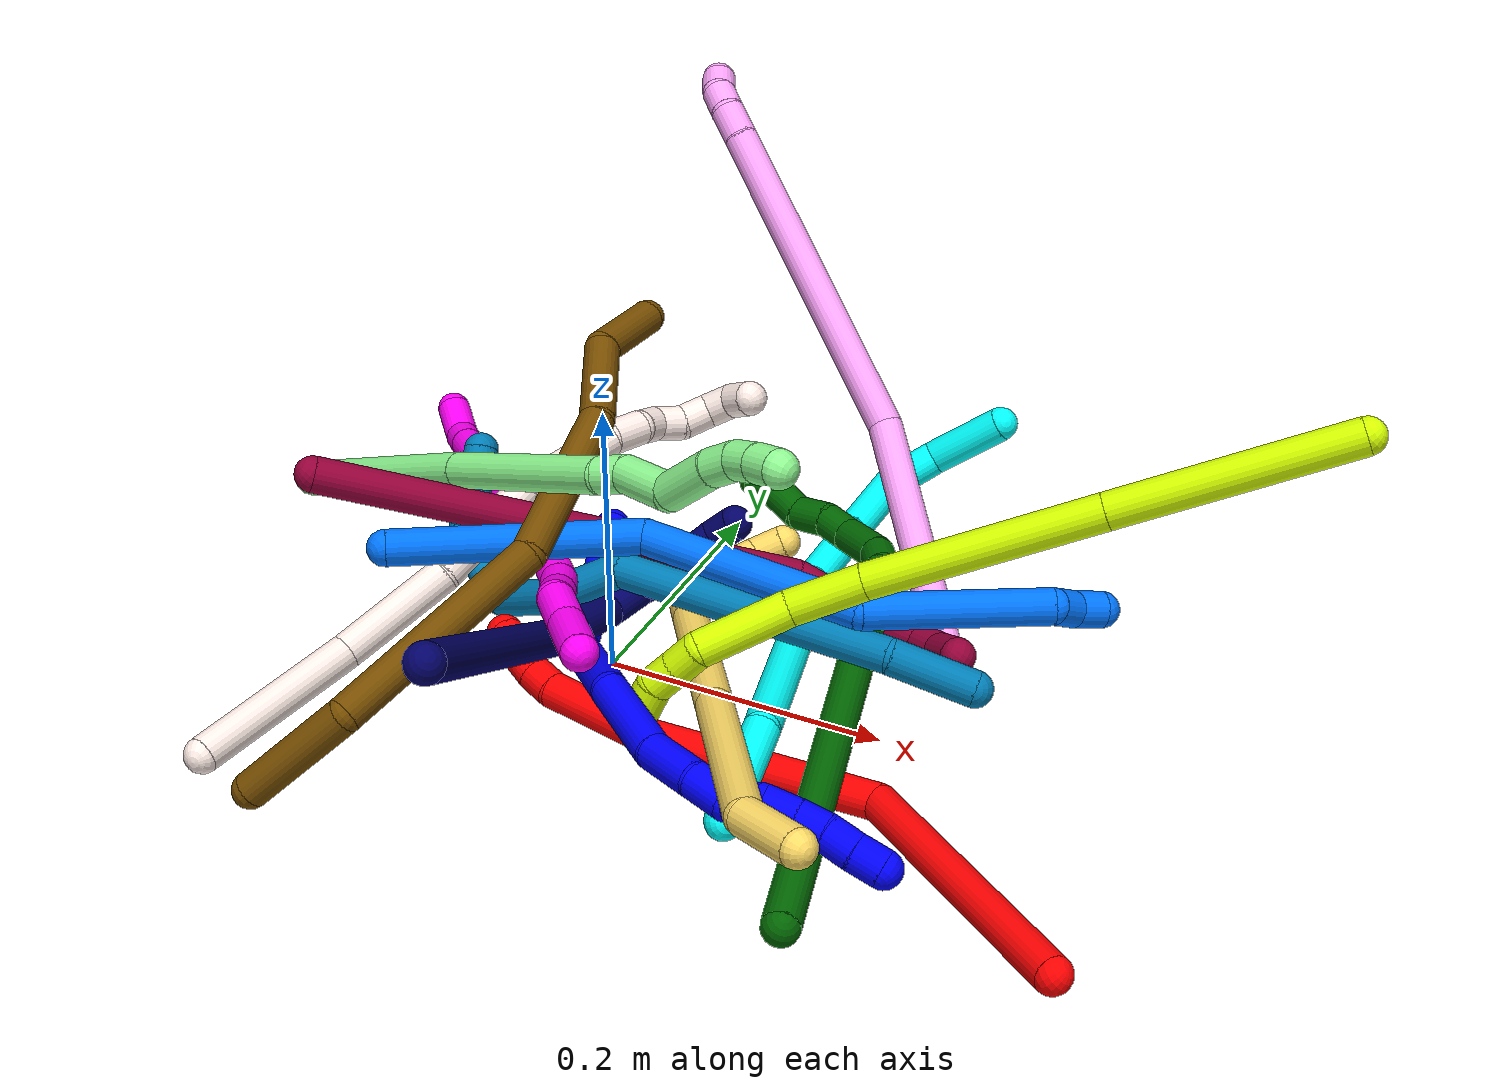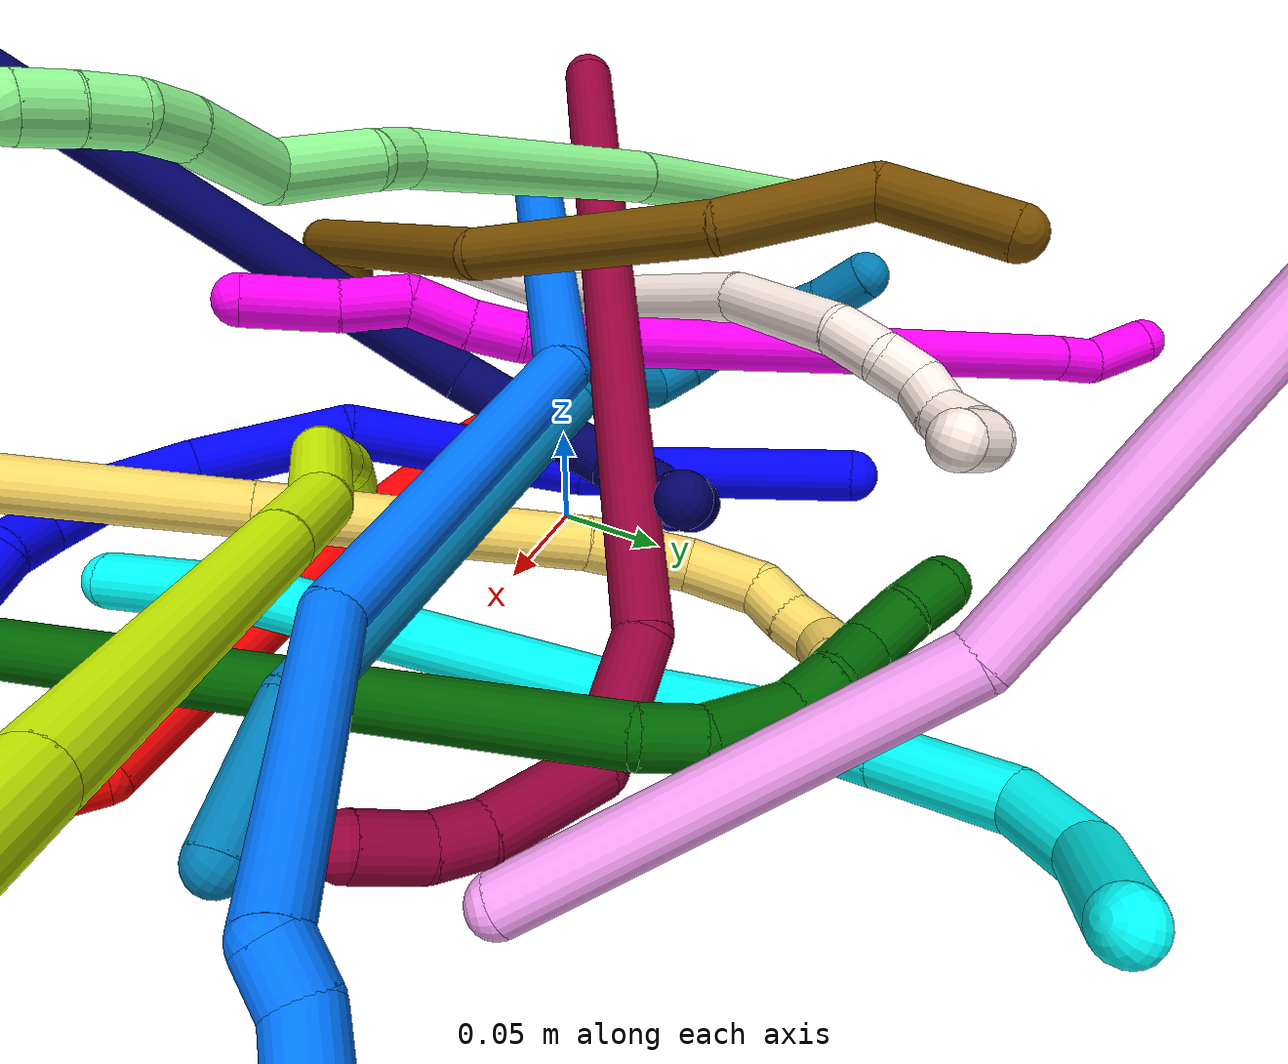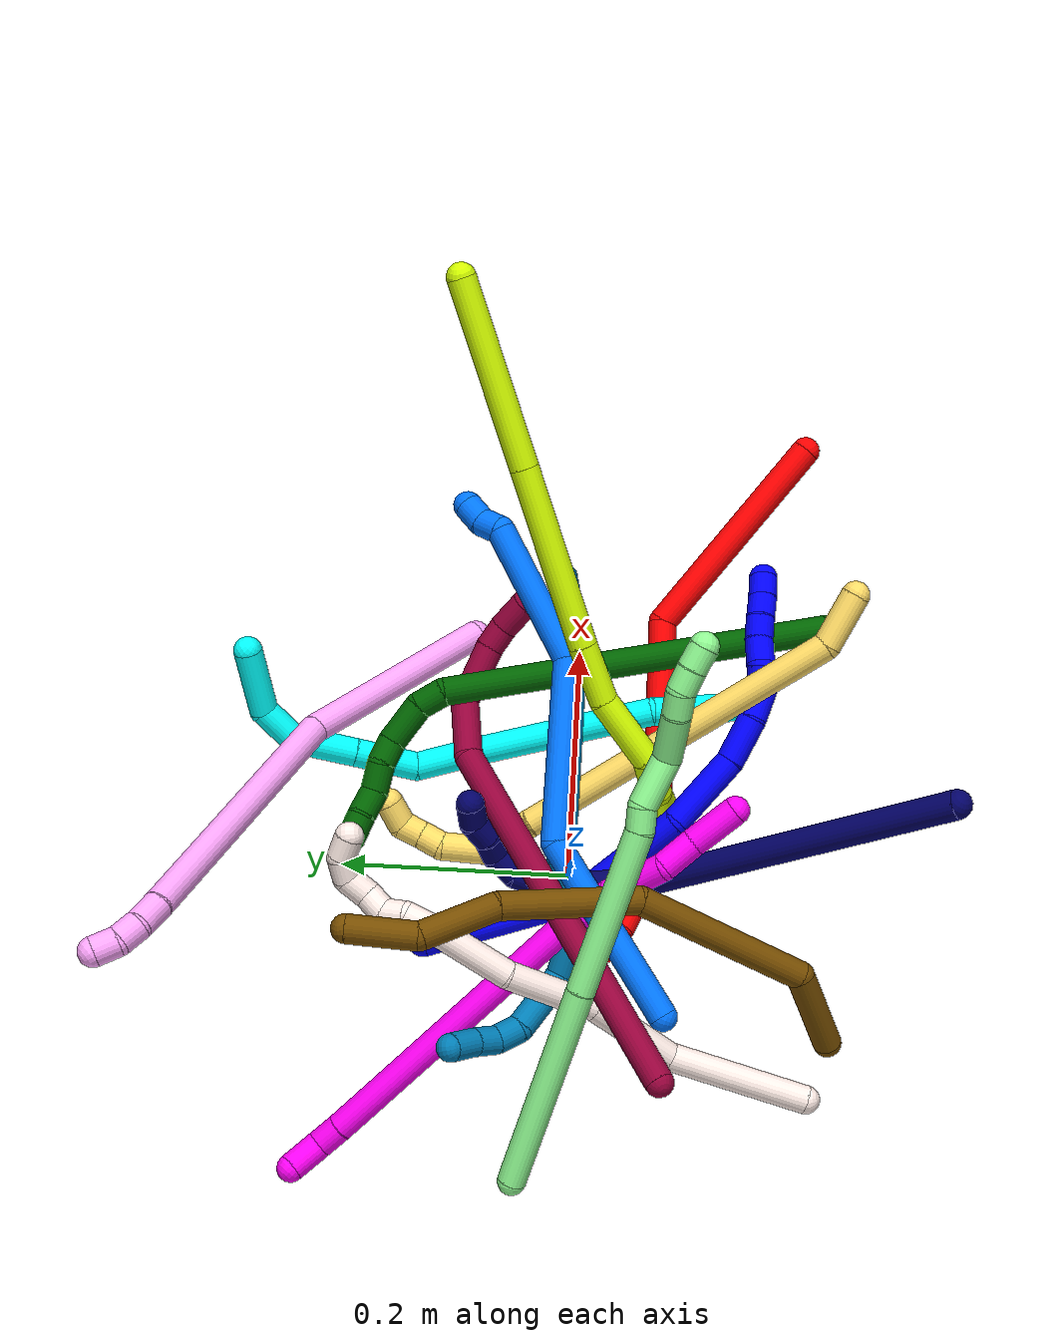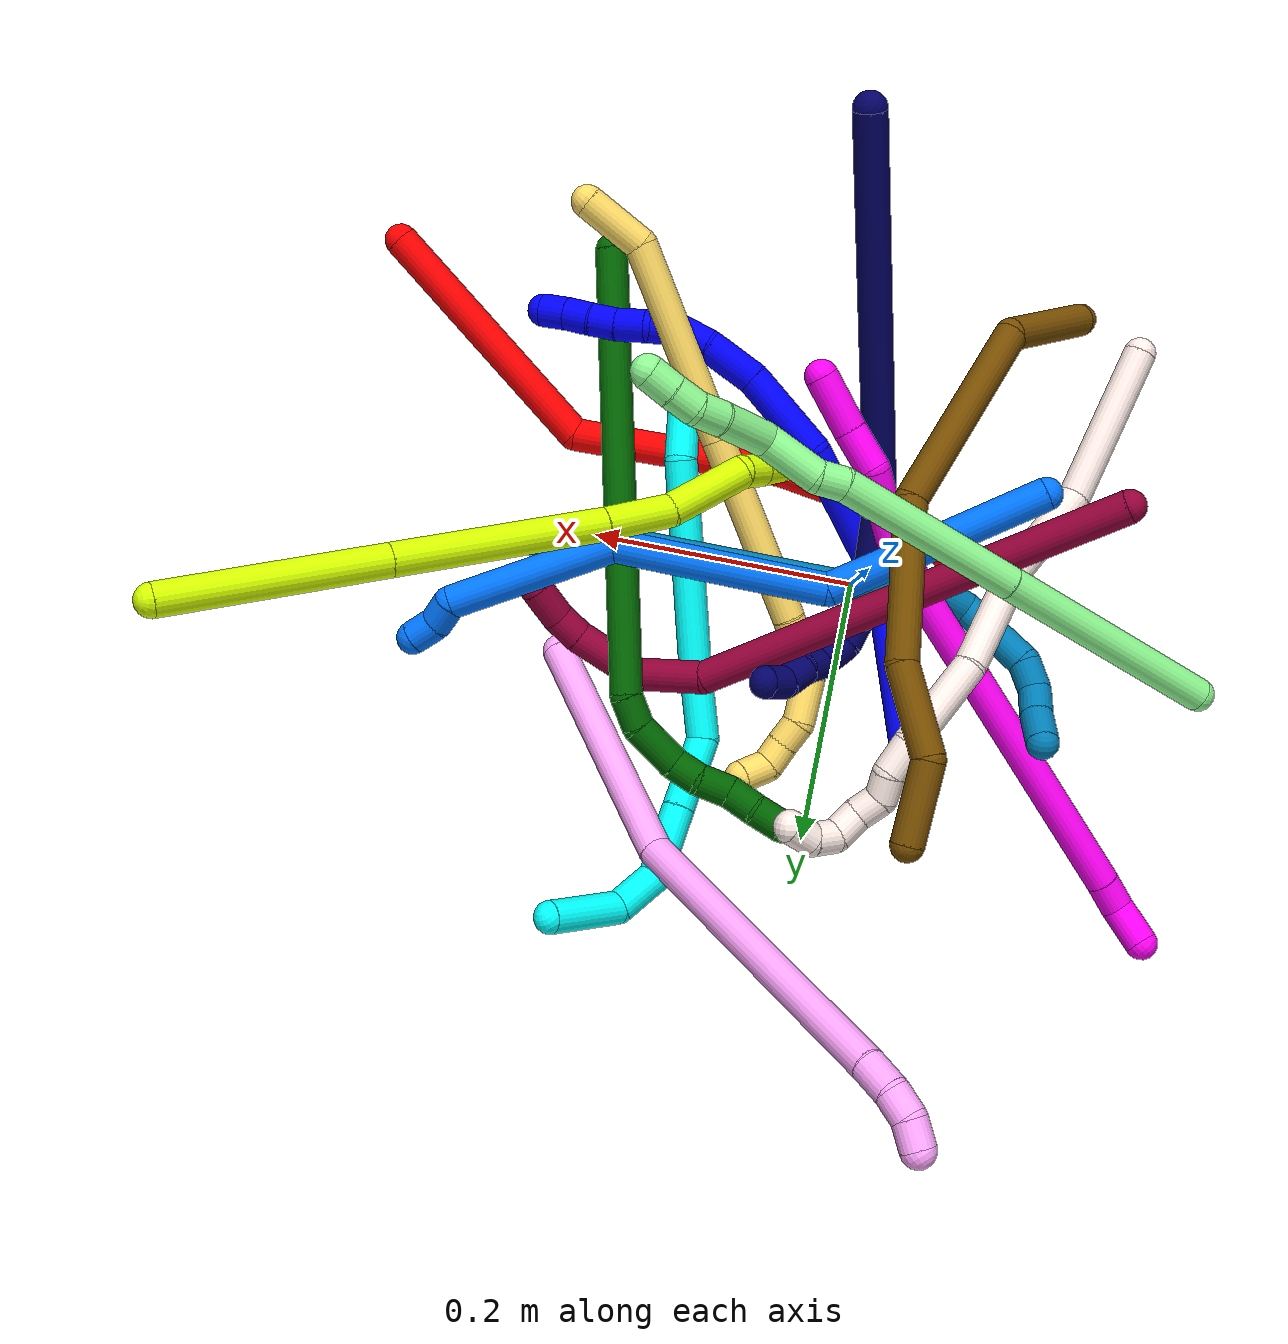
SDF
<sdf version="1.7">
 <world name="default">
  <plugin name="TubeGeneratorPlugin" filename="libtube_generator_plugin.so"/>
  <model name="photoneo_s_sensor">
   <static>1</static>
   <pose>0 0 2 1.57079 1.57079 3.14159</pose>
   <link name="link">
    <inertial><mass>0.1</mass></inertial>
    <sensor name="sensor" type="depth">
     <update_rate>30</update_rate>
     <camera>
      <horizontal_fov>1.22</horizontal_fov>
      <image><width>1920</width><height>1200</height><format>B8G8R8</format></image>
      <clip><near>0.1</near><far>4</far></clip>
      <depth_camera><output>points</output></depth_camera>
     </camera>
     <plugin name="camera_plugin" filename="libgazebo_ros_depth_camera.so">
      <baseline>0.2</baseline>
      <alwaysOn>1</alwaysOn>
      <updateRate>0.0</updateRate>
      <cameraName>camera_ir</cameraName>
      <imageTopicName>/camera/color/image_raw</imageTopicName>
      <cameraInfoTopicName>/camera/color/camera_info</cameraInfoTopicName>
      <depthImageTopicName>/camera/depth/image_raw</depthImageTopicName>
      <depthImageCameraInfoTopicName>/camera/depth/camera_info</depthImageCameraInfoTopicName>
      <pointCloudTopicName>/camera/depth/points</pointCloudTopicName>
      <frameName>fr_optical</frameName>
      <pointCloudCutoff>0.1</pointCloudCutoff>
      <pointCloudCutoffMax>2.0</pointCloudCutoffMax>
      <distortionK1>0</distortionK1>
      <distortionK2>0</distortionK2>
      <distortionK3>0</distortionK3>
      <distortionT1>0</distortionT1>
      <distortionT2>0</distortionT2>
      <CxPrime>0</CxPrime>
      <Cx>0</Cx>
      <Cy>0</Cy>
      <focalLength>0</focalLength>
      <hackBaseline>0</hackBaseline>
     </plugin>
    </sensor>
   </link>
  </model>
  <gravity>0 0 -9.8</gravity>
  <magnetic_field>6e-06 2.3e-05 -4.2e-05</magnetic_field>
  <atmosphere type="adiabatic"/>
  <physics name="default_physics" default="0" type="ode">
   <max_step_size>0.003</max_step_size>
   <real_time_factor>1</real_time_factor>
   <real_time_update_rate>1000</real_time_update_rate>
   <max_contacts>10000</max_contacts>
   <ode>
    <solver>
     <type>quick</type>
     <iters>100</iters>
     <sor>1.3</sor>
     <use_dynamic_moi_rescaling>0</use_dynamic_moi_rescaling>
    </solver>
    <constraints>
     <contact_max_correcting_vel>0</contact_max_correcting_vel>
     <contact_surface_layer>0.001</contact_surface_layer>
     <cfm>0</cfm>
     <erp>0.2</erp>
    </constraints>
   </ode>
  </physics>
  <scene><ambient>0.4 0.4 0.4 1</ambient><background>0.7 0.7 0.7 1</background><shadows>0</shadows></scene>
  <audio><device>default</device></audio>
  <spherical_coordinates>
   <surface_model>EARTH_WGS84</surface_model>
   <latitude_deg>0</latitude_deg>
   <longitude_deg>0</longitude_deg>
   <elevation>0</elevation>
   <heading_deg>0</heading_deg>
  </spherical_coordinates>
  <model name="bin">
   <static>1</static>
   <link name="bottom">
    <collision name="collision-bottom">
     <pose>0 0 -0.01 0 -0 0</pose>
     <geometry><box><size>0.8 0.6 0.02</size></box></geometry>
     <surface>
      <friction><ode><mu>100</mu><mu2>100</mu2></ode></friction>
      <contact><collide_bitmask>65535</collide_bitmask></contact>
     </surface>
    </collision>
   </link>
   <link name="west_wall">
    <collision name="collision-west_wall">
     <pose>-0.41 0 0.1 0 -0 0</pose>
     <geometry><box><size>0.02 0.6 0.2</size></box></geometry>
     <surface>
      <friction><ode><mu>100</mu><mu2>100</mu2></ode></friction>
      <contact><collide_bitmask>65535</collide_bitmask></contact>
     </surface>
    </collision>
   </link>
   <link name="east_wall">
    <collision name="collision-east_wall">
     <pose>0.41 0 0.1 0 -0 0</pose>
     <geometry><box><size>0.02 0.6 0.2</size></box></geometry>
     <surface>
      <friction><ode><mu>100</mu><mu2>100</mu2></ode></friction>
      <contact><collide_bitmask>65535</collide_bitmask></contact>
     </surface>
    </collision>
   </link>
   <link name="south_wall">
    <collision name="collision-south_wall">
     <pose>0 -0.31 0.1 0 -0 0</pose>
     <geometry><box><size>0.8 0.02 0.2</size></box></geometry>
     <surface>
      <friction><ode><mu>100</mu><mu2>100</mu2></ode></friction>
      <contact><collide_bitmask>65535</collide_bitmask></contact>
     </surface>
    </collision>
   </link>
   <link name="north_wall">
    <collision name="collision-north_wall">
     <pose>0 0.31 0.1 0 -0 0</pose>
     <geometry><box><size>0.8 0.02 0.2</size></box></geometry>
     <surface>
      <friction><ode><mu>100</mu><mu2>100</mu2></ode></friction>
      <contact><collide_bitmask>65535</collide_bitmask></contact>
     </surface>
    </collision>
   </link>
  </model>
  <model name="1">
   <static>0</static>
   <link name="1">
    <collision name="collision-cylinder-e_1_1_4">
     <pose>0.018435 -0.016506 0.063716 0.253477 0.273086 0.035011</pose>
     <geometry><cylinder><radius>0.0125</radius><length>0.136704</length></cylinder></geometry>
     <surface>
      <friction><ode><mu>1.16</mu><mu2>1.16</mu2><slip1>0</slip1><slip2>0</slip2></ode></friction>
      <contact><ode><kp>1e+06</kp><kd>1</kd><max_vel>0</max_vel><min_depth>0.001</min_depth></ode></contact>
     </surface>
    </collision>
    <visual name="visual-cylinder-e_1_1_4">
     <pose>0.018435 -0.016506 0.063716 0.253477 0.273086 0.035011</pose>
     <geometry><cylinder><radius>0.0125</radius><length>0.136704</length></cylinder></geometry>
     <material><ambient>0 0 1 1</ambient></material>
    </visual>
    <collision name="collision-cylinder-e_2_4_5">
     <pose>0.079863 -0.051674 0.162984 0.483408 0.81955 0.213349</pose>
     <geometry><cylinder><radius>0.0125</radius><length>0.117656</length></cylinder></geometry>
     <surface>
      <friction><ode><mu>1.16</mu><mu2>1.16</mu2><slip1>0</slip1><slip2>0</slip2></ode></friction>
      <contact><ode><kp>1e+06</kp><kd>1</kd><max_vel>0</max_vel><min_depth>0.001</min_depth></ode></contact>
     </surface>
    </collision>
    <visual name="visual-cylinder-e_2_4_5">
     <pose>0.079863 -0.051674 0.162984 0.483408 0.81955 0.213349</pose>
     <geometry><cylinder><radius>0.0125</radius><length>0.117656</length></cylinder></geometry>
     <material><ambient>0 0 1 1</ambient></material>
    </visual>
    <collision name="collision-cylinder-e_3_5_6">
     <pose>0.140013 -0.092873 0.219641 0.818195 0.507182 0.223793</pose>
     <geometry><cylinder><radius>0.0125</radius><length>0.070643</length></cylinder></geometry>
     <surface>
      <friction><ode><mu>1.16</mu><mu2>1.16</mu2><slip1>0</slip1><slip2>0</slip2></ode></friction>
      <contact><ode><kp>1e+06</kp><kd>1</kd><max_vel>0</max_vel><min_depth>0.001</min_depth></ode></contact>
     </surface>
    </collision>
    <visual name="visual-cylinder-e_3_5_6">
     <pose>0.140013 -0.092873 0.219641 0.818195 0.507182 0.223793</pose>
     <geometry><cylinder><radius>0.0125</radius><length>0.070643</length></cylinder></geometry>
     <material><ambient>0 0 1 1</ambient></material>
    </visual>
    <collision name="collision-cylinder-e_4_6_7">
     <pose>0.168802 -0.130742 0.248644 1.09509 0.593368 0.368568</pose>
     <geometry><cylinder><radius>0.0125</radius><length>0.041606</length></cylinder></geometry>
     <surface>
      <friction><ode><mu>1.16</mu><mu2>1.16</mu2><slip1>0</slip1><slip2>0</slip2></ode></friction>
      <contact><ode><kp>1e+06</kp><kd>1</kd><max_vel>0</max_vel><min_depth>0.001</min_depth></ode></contact>
     </surface>
    </collision>
    <visual name="visual-cylinder-e_4_6_7">
     <pose>0.168802 -0.130742 0.248644 1.09509 0.593368 0.368568</pose>
     <geometry><cylinder><radius>0.0125</radius><length>0.041606</length></cylinder></geometry>
     <material><ambient>0 0 1 1</ambient></material>
    </visual>
    <collision name="collision-cylinder-e_5_7_8">
     <pose>0.186038 -0.157914 0.260597 1.24089 0.420997 0.30302</pose>
     <geometry><cylinder><radius>0.0125</radius><length>0.027425</length></cylinder></geometry>
     <surface>
      <friction><ode><mu>1.16</mu><mu2>1.16</mu2><slip1>0</slip1><slip2>0</slip2></ode></friction>
      <contact><ode><kp>1e+06</kp><kd>1</kd><max_vel>0</max_vel><min_depth>0.001</min_depth></ode></contact>
     </surface>
    </collision>
    <visual name="visual-cylinder-e_5_7_8">
     <pose>0.186038 -0.157914 0.260597 1.24089 0.420997 0.30302</pose>
     <geometry><cylinder><radius>0.0125</radius><length>0.027425</length></cylinder></geometry>
     <material><ambient>0 0 1 1</ambient></material>
    </visual>
    <collision name="collision-cylinder-e_6_8_9">
     <pose>0.198264 -0.178785 0.26249 1.80569 0.619489 0.770776</pose>
     <geometry><cylinder><radius>0.0125</radius><length>0.022811</length></cylinder></geometry>
     <surface>
      <friction><ode><mu>1.16</mu><mu2>1.16</mu2><slip1>0</slip1><slip2>0</slip2></ode></friction>
      <contact><ode><kp>1e+06</kp><kd>1</kd><max_vel>0</max_vel><min_depth>0.001</min_depth></ode></contact>
     </surface>
    </collision>
    <visual name="visual-cylinder-e_6_8_9">
     <pose>0.198264 -0.178785 0.26249 1.80569 0.619489 0.770776</pose>
     <geometry><cylinder><radius>0.0125</radius><length>0.022811</length></cylinder></geometry>
     <material><ambient>0 0 1 1</ambient></material>
    </visual>
    <collision name="collision-cylinder-e_7_9_10">
     <pose>0.207304 -0.199022 0.259741 1.62315 0.212196 0.223515</pose>
     <geometry><cylinder><radius>0.0125</radius><length>0.022956</length></cylinder></geometry>
     <surface>
      <friction><ode><mu>1.16</mu><mu2>1.16</mu2><slip1>0</slip1><slip2>0</slip2></ode></friction>
      <contact><ode><kp>1e+06</kp><kd>1</kd><max_vel>0</max_vel><min_depth>0.001</min_depth></ode></contact>
     </surface>
    </collision>
    <visual name="visual-cylinder-e_7_9_10">
     <pose>0.207304 -0.199022 0.259741 1.62315 0.212196 0.223515</pose>
     <geometry><cylinder><radius>0.0125</radius><length>0.022956</length></cylinder></geometry>
     <material><ambient>0 0 1 1</ambient></material>
    </visual>
    <collision name="collision-cylinder-e_8_10_11">
     <pose>0.212574 -0.219854 0.259788 1.505 0.287565 0.269469</pose>
     <geometry><cylinder><radius>0.0125</radius><length>0.020121</length></cylinder></geometry>
     <surface>
      <friction><ode><mu>1.16</mu><mu2>1.16</mu2><slip1>0</slip1><slip2>0</slip2></ode></friction>
      <contact><ode><kp>1e+06</kp><kd>1</kd><max_vel>0</max_vel><min_depth>0.001</min_depth></ode></contact>
     </surface>
    </collision>
    <visual name="visual-cylinder-e_8_10_11">
     <pose>0.212574 -0.219854 0.259788 1.505 0.287565 0.269469</pose>
     <geometry><cylinder><radius>0.0125</radius><length>0.020121</length></cylinder></geometry>
     <material><ambient>0 0 1 1</ambient></material>
    </visual>
    <collision name="collision-cylinder-e_9_11_12">
     <pose>0.217035 -0.239263 0.261845 1.42637 0.161154 0.139488</pose>
     <geometry><cylinder><radius>0.0125</radius><length>0.020031</length></cylinder></geometry>
     <surface>
      <friction><ode><mu>1.16</mu><mu2>1.16</mu2><slip1>0</slip1><slip2>0</slip2></ode></friction>
      <contact><ode><kp>1e+06</kp><kd>1</kd><max_vel>0</max_vel><min_depth>0.001</min_depth></ode></contact>
     </surface>
    </collision>
    <visual name="visual-cylinder-e_9_11_12">
     <pose>0.217035 -0.239263 0.261845 1.42637 0.161154 0.139488</pose>
     <geometry><cylinder><radius>0.0125</radius><length>0.020031</length></cylinder></geometry>
     <material><ambient>0 0 1 1</ambient></material>
    </visual>
    <collision name="collision-cylinder-e_10_12_2">
     <pose>0.220205 -0.258921 0.263984 1.49839 0.15664 0.14573</pose>
     <geometry><cylinder><radius>0.0125</radius><length>0.020046</length></cylinder></geometry>
     <surface>
      <friction><ode><mu>1.16</mu><mu2>1.16</mu2><slip1>0</slip1><slip2>0</slip2></ode></friction>
      <contact><ode><kp>1e+06</kp><kd>1</kd><max_vel>0</max_vel><min_depth>0.001</min_depth></ode></contact>
     </surface>
    </collision>
    <visual name="visual-cylinder-e_10_12_2">
     <pose>0.220205 -0.258921 0.263984 1.49839 0.15664 0.14573</pose>
     <geometry><cylinder><radius>0.0125</radius><length>0.020046</length></cylinder></geometry>
     <material><ambient>0 0 1 1</ambient></material>
    </visual>
    <collision name="collision-sphere-2">
     <pose>0.221769 -0.268795 0.264701 0 -0 0</pose>
     <geometry><sphere><radius>0.0125</radius></sphere></geometry>
     <surface>
      <friction><ode><mu>1.16</mu><mu2>1.16</mu2><slip1>0</slip1><slip2>0</slip2></ode></friction>
      <contact><ode><kp>1e+06</kp><kd>1</kd><max_vel>0</max_vel><min_depth>0.001</min_depth></ode></contact>
     </surface>
    </collision>
    <visual name="visual-sphere-2">
     <pose>0.221769 -0.268795 0.264701 0 -0 0</pose>
     <geometry><sphere><radius>0.0125</radius></sphere></geometry>
     <material><ambient>0 0 1 1</ambient></material>
    </visual>
    <collision name="collision-sphere-12">
     <pose>0.218642 -0.249046 0.263268 0 -0 0</pose>
     <geometry><sphere><radius>0.0125</radius></sphere></geometry>
     <surface>
      <friction><ode><mu>1.16</mu><mu2>1.16</mu2><slip1>0</slip1><slip2>0</slip2></ode></friction>
      <contact><ode><kp>1e+06</kp><kd>1</kd><max_vel>0</max_vel><min_depth>0.001</min_depth></ode></contact>
     </surface>
    </collision>
    <visual name="visual-sphere-12">
     <pose>0.218642 -0.249046 0.263268 0 -0 0</pose>
     <geometry><sphere><radius>0.0125</radius></sphere></geometry>
     <material><ambient>0 0 1 1</ambient></material>
    </visual>
    <collision name="collision-sphere-11">
     <pose>0.215428 -0.229481 0.260423 0 -0 0</pose>
     <geometry><sphere><radius>0.0125</radius></sphere></geometry>
     <surface>
      <friction><ode><mu>1.16</mu><mu2>1.16</mu2><slip1>0</slip1><slip2>0</slip2></ode></friction>
      <contact><ode><kp>1e+06</kp><kd>1</kd><max_vel>0</max_vel><min_depth>0.001</min_depth></ode></contact>
     </surface>
    </collision>
    <visual name="visual-sphere-11">
     <pose>0.215428 -0.229481 0.260423 0 -0 0</pose>
     <geometry><sphere><radius>0.0125</radius></sphere></geometry>
     <material><ambient>0 0 1 1</ambient></material>
    </visual>
    <collision name="collision-sphere-10">
     <pose>0.209721 -0.210227 0.259154 0 -0 0</pose>
     <geometry><sphere><radius>0.0125</radius></sphere></geometry>
     <surface>
      <friction><ode><mu>1.16</mu><mu2>1.16</mu2><slip1>0</slip1><slip2>0</slip2></ode></friction>
      <contact><ode><kp>1e+06</kp><kd>1</kd><max_vel>0</max_vel><min_depth>0.001</min_depth></ode></contact>
     </surface>
    </collision>
    <visual name="visual-sphere-10">
     <pose>0.209721 -0.210227 0.259154 0 -0 0</pose>
     <geometry><sphere><radius>0.0125</radius></sphere></geometry>
     <material><ambient>0 0 1 1</ambient></material>
    </visual>
    <collision name="collision-sphere-9">
     <pose>0.204886 -0.187817 0.260328 0 -0 0</pose>
     <geometry><sphere><radius>0.0125</radius></sphere></geometry>
     <surface>
      <friction><ode><mu>1.16</mu><mu2>1.16</mu2><slip1>0</slip1><slip2>0</slip2></ode></friction>
      <contact><ode><kp>1e+06</kp><kd>1</kd><max_vel>0</max_vel><min_depth>0.001</min_depth></ode></contact>
     </surface>
    </collision>
    <visual name="visual-sphere-9">
     <pose>0.204886 -0.187817 0.260328 0 -0 0</pose>
     <geometry><sphere><radius>0.0125</radius></sphere></geometry>
     <material><ambient>0 0 1 1</ambient></material>
    </visual>
    <collision name="collision-sphere-4">
     <pose>0.03687 -0.033011 0.127432 0 -0 0</pose>
     <geometry><sphere><radius>0.0125</radius></sphere></geometry>
     <surface>
      <friction><ode><mu>1.16</mu><mu2>1.16</mu2><slip1>0</slip1><slip2>0</slip2></ode></friction>
      <contact><ode><kp>1e+06</kp><kd>1</kd><max_vel>0</max_vel><min_depth>0.001</min_depth></ode></contact>
     </surface>
    </collision>
    <visual name="visual-sphere-4">
     <pose>0.03687 -0.033011 0.127432 0 -0 0</pose>
     <geometry><sphere><radius>0.0125</radius></sphere></geometry>
     <material><ambient>0 0 1 1</ambient></material>
    </visual>
    <collision name="collision-sphere-1">
     <geometry><sphere><radius>0.0125</radius></sphere></geometry>
     <surface>
      <friction><ode><mu>1.16</mu><mu2>1.16</mu2><slip1>0</slip1><slip2>0</slip2></ode></friction>
      <contact><ode><kp>1e+06</kp><kd>1</kd><max_vel>0</max_vel><min_depth>0.001</min_depth></ode></contact>
     </surface>
    </collision>
    <visual name="visual-sphere-1">
     <geometry><sphere><radius>0.0125</radius></sphere></geometry>
     <material><ambient>0 0 1 1</ambient></material>
    </visual>
    <collision name="collision-sphere-8">
     <pose>0.191642 -0.169754 0.264651 0 -0 0</pose>
     <geometry><sphere><radius>0.0125</radius></sphere></geometry>
     <surface>
      <friction><ode><mu>1.16</mu><mu2>1.16</mu2><slip1>0</slip1><slip2>0</slip2></ode></friction>
      <contact><ode><kp>1e+06</kp><kd>1</kd><max_vel>0</max_vel><min_depth>0.001</min_depth></ode></contact>
     </surface>
    </collision>
    <visual name="visual-sphere-8">
     <pose>0.191642 -0.169754 0.264651 0 -0 0</pose>
     <geometry><sphere><radius>0.0125</radius></sphere></geometry>
     <material><ambient>0 0 1 1</ambient></material>
    </visual>
    <collision name="collision-sphere-5">
     <pose>0.122857 -0.070337 0.198536 0 -0 0</pose>
     <geometry><sphere><radius>0.0125</radius></sphere></geometry>
     <surface>
      <friction><ode><mu>1.16</mu><mu2>1.16</mu2><slip1>0</slip1><slip2>0</slip2></ode></friction>
      <contact><ode><kp>1e+06</kp><kd>1</kd><max_vel>0</max_vel><min_depth>0.001</min_depth></ode></contact>
     </surface>
    </collision>
    <visual name="visual-sphere-5">
     <pose>0.122857 -0.070337 0.198536 0 -0 0</pose>
     <geometry><sphere><radius>0.0125</radius></sphere></geometry>
     <material><ambient>0 0 1 1</ambient></material>
    </visual>
    <collision name="collision-sphere-6">
     <pose>0.157169 -0.115409 0.240745 0 -0 0</pose>
     <geometry><sphere><radius>0.0125</radius></sphere></geometry>
     <surface>
      <friction><ode><mu>1.16</mu><mu2>1.16</mu2><slip1>0</slip1><slip2>0</slip2></ode></friction>
      <contact><ode><kp>1e+06</kp><kd>1</kd><max_vel>0</max_vel><min_depth>0.001</min_depth></ode></contact>
     </surface>
    </collision>
    <visual name="visual-sphere-6">
     <pose>0.157169 -0.115409 0.240745 0 -0 0</pose>
     <geometry><sphere><radius>0.0125</radius></sphere></geometry>
     <material><ambient>0 0 1 1</ambient></material>
    </visual>
    <collision name="collision-sphere-7">
     <pose>0.180434 -0.146074 0.256542 0 -0 0</pose>
     <geometry><sphere><radius>0.0125</radius></sphere></geometry>
     <surface>
      <friction><ode><mu>1.16</mu><mu2>1.16</mu2><slip1>0</slip1><slip2>0</slip2></ode></friction>
      <contact><ode><kp>1e+06</kp><kd>1</kd><max_vel>0</max_vel><min_depth>0.001</min_depth></ode></contact>
     </surface>
    </collision>
    <visual name="visual-sphere-7">
     <pose>0.180434 -0.146074 0.256542 0 -0 0</pose>
     <geometry><sphere><radius>0.0125</radius></sphere></geometry>
     <material><ambient>0 0 1 1</ambient></material>
    </visual>
    <inertial>
     <pose>0.112506 -0.095443 0.177218 0 -0 0</pose>
     <mass>0.5</mass>
     <inertia>
      <ixx>0.000403</ixx>
      <ixy>0</ixy>
      <ixz>0</ixz>
      <iyy>0.000392</iyy>
      <iyz>0</iyz>
      <izz>-3.1e-05</izz>
     </inertia>
    </inertial>
   </link>
   <pose>-0.066191 0.123442 0.023631 2.06251 -1.05296 -0.45205</pose>
  </model>
  <model name="2">
   <static>0</static>
   <link name="2">
    <collision name="collision-cylinder-e_1_1_4">
     <pose>-0.052133 0.066903 -0.050646 -2.21877 -0.555923 1.04202</pose>
     <geometry><cylinder><radius>0.0125</radius><length>0.197574</length></cylinder></geometry>
     <surface>
      <friction><ode><mu>1.16</mu><mu2>1.16</mu2><slip1>0</slip1><slip2>0</slip2></ode></friction>
      <contact><ode><kp>1e+06</kp><kd>1</kd><max_vel>0</max_vel><min_depth>0.001</min_depth></ode></contact>
     </surface>
    </collision>
    <visual name="visual-cylinder-e_1_1_4">
     <pose>-0.052133 0.066903 -0.050646 -2.21877 -0.555923 1.04202</pose>
     <geometry><cylinder><radius>0.0125</radius><length>0.197574</length></cylinder></geometry>
     <material><ambient>1 0 0 1</ambient></material>
    </visual>
    <collision name="collision-cylinder-e_2_4_5">
     <pose>-0.16142 0.139701 -0.157232 -3.03659 -0.793383 2.89199</pose>
     <geometry><cylinder><radius>0.0125</radius><length>0.160382</length></cylinder></geometry>
     <surface>
      <friction><ode><mu>1.16</mu><mu2>1.16</mu2><slip1>0</slip1><slip2>0</slip2></ode></friction>
      <contact><ode><kp>1e+06</kp><kd>1</kd><max_vel>0</max_vel><min_depth>0.001</min_depth></ode></contact>
     </surface>
    </collision>
    <visual name="visual-cylinder-e_2_4_5">
     <pose>-0.16142 0.139701 -0.157232 -3.03659 -0.793383 2.89199</pose>
     <geometry><cylinder><radius>0.0125</radius><length>0.160382</length></cylinder></geometry>
     <material><ambient>1 0 0 1</ambient></material>
    </visual>
    <collision name="collision-cylinder-e_3_5_6">
     <pose>-0.249213 0.155335 -0.23849 -2.77443 -0.846122 2.35934</pose>
     <geometry><cylinder><radius>0.0125</radius><length>0.081845</length></cylinder></geometry>
     <surface>
      <friction><ode><mu>1.16</mu><mu2>1.16</mu2><slip1>0</slip1><slip2>0</slip2></ode></friction>
      <contact><ode><kp>1e+06</kp><kd>1</kd><max_vel>0</max_vel><min_depth>0.001</min_depth></ode></contact>
     </surface>
    </collision>
    <visual name="visual-cylinder-e_3_5_6">
     <pose>-0.249213 0.155335 -0.23849 -2.77443 -0.846122 2.35934</pose>
     <geometry><cylinder><radius>0.0125</radius><length>0.081845</length></cylinder></geometry>
     <material><ambient>1 0 0 1</ambient></material>
    </visual>
    <collision name="collision-cylinder-e_4_6_7">
     <pose>-0.287447 0.169544 -0.268703 -2.40126 -0.85312 1.72812</pose>
     <geometry><cylinder><radius>0.0125</radius><length>0.020161</length></cylinder></geometry>
     <surface>
      <friction><ode><mu>1.16</mu><mu2>1.16</mu2><slip1>0</slip1><slip2>0</slip2></ode></friction>
      <contact><ode><kp>1e+06</kp><kd>1</kd><max_vel>0</max_vel><min_depth>0.001</min_depth></ode></contact>
     </surface>
    </collision>
    <visual name="visual-cylinder-e_4_6_7">
     <pose>-0.287447 0.169544 -0.268703 -2.40126 -0.85312 1.72812</pose>
     <geometry><cylinder><radius>0.0125</radius><length>0.020161</length></cylinder></geometry>
     <material><ambient>1 0 0 1</ambient></material>
    </visual>
    <collision name="collision-cylinder-e_5_7_8">
     <pose>-0.303895 0.17798 -0.27608 -2.1304 -1.08482 1.6557</pose>
     <geometry><cylinder><radius>0.0125</radius><length>0.020028</length></cylinder></geometry>
     <surface>
      <friction><ode><mu>1.16</mu><mu2>1.16</mu2><slip1>0</slip1><slip2>0</slip2></ode></friction>
      <contact><ode><kp>1e+06</kp><kd>1</kd><max_vel>0</max_vel><min_depth>0.001</min_depth></ode></contact>
     </surface>
    </collision>
    <visual name="visual-cylinder-e_5_7_8">
     <pose>-0.303895 0.17798 -0.27608 -2.1304 -1.08482 1.6557</pose>
     <geometry><cylinder><radius>0.0125</radius><length>0.020028</length></cylinder></geometry>
     <material><ambient>1 0 0 1</ambient></material>
    </visual>
    <collision name="collision-cylinder-e_6_8_2">
     <pose>-0.320412 0.187499 -0.281807 -2.09918 -0.872415 1.36389</pose>
     <geometry><cylinder><radius>0.0125</radius><length>0.020011</length></cylinder></geometry>
     <surface>
      <friction><ode><mu>1.16</mu><mu2>1.16</mu2><slip1>0</slip1><slip2>0</slip2></ode></friction>
      <contact><ode><kp>1e+06</kp><kd>1</kd><max_vel>0</max_vel><min_depth>0.001</min_depth></ode></contact>
     </surface>
    </collision>
    <visual name="visual-cylinder-e_6_8_2">
     <pose>-0.320412 0.187499 -0.281807 -2.09918 -0.872415 1.36389</pose>
     <geometry><cylinder><radius>0.0125</radius><length>0.020011</length></cylinder></geometry>
     <material><ambient>1 0 0 1</ambient></material>
    </visual>
    <collision name="collision-sphere-2">
     <pose>-0.328075 0.193055 -0.28505 0 -0 0</pose>
     <geometry><sphere><radius>0.0125</radius></sphere></geometry>
     <surface>
      <friction><ode><mu>1.16</mu><mu2>1.16</mu2><slip1>0</slip1><slip2>0</slip2></ode></friction>
      <contact><ode><kp>1e+06</kp><kd>1</kd><max_vel>0</max_vel><min_depth>0.001</min_depth></ode></contact>
     </surface>
    </collision>
    <visual name="visual-sphere-2">
     <pose>-0.328075 0.193055 -0.28505 0 -0 0</pose>
     <geometry><sphere><radius>0.0125</radius></sphere></geometry>
     <material><ambient>1 0 0 1</ambient></material>
    </visual>
    <collision name="collision-sphere-4">
     <pose>-0.104265 0.133806 -0.101293 0 -0 0</pose>
     <geometry><sphere><radius>0.0125</radius></sphere></geometry>
     <surface>
      <friction><ode><mu>1.16</mu><mu2>1.16</mu2><slip1>0</slip1><slip2>0</slip2></ode></friction>
      <contact><ode><kp>1e+06</kp><kd>1</kd><max_vel>0</max_vel><min_depth>0.001</min_depth></ode></contact>
     </surface>
    </collision>
    <visual name="visual-sphere-4">
     <pose>-0.104265 0.133806 -0.101293 0 -0 0</pose>
     <geometry><sphere><radius>0.0125</radius></sphere></geometry>
     <material><ambient>1 0 0 1</ambient></material>
    </visual>
    <collision name="collision-sphere-1">
     <geometry><sphere><radius>0.0125</radius></sphere></geometry>
     <surface>
      <friction><ode><mu>1.16</mu><mu2>1.16</mu2><slip1>0</slip1><slip2>0</slip2></ode></friction>
      <contact><ode><kp>1e+06</kp><kd>1</kd><max_vel>0</max_vel><min_depth>0.001</min_depth></ode></contact>
     </surface>
    </collision>
    <visual name="visual-sphere-1">
     <geometry><sphere><radius>0.0125</radius></sphere></geometry>
     <material><ambient>1 0 0 1</ambient></material>
    </visual>
    <collision name="collision-sphere-8">
     <pose>-0.312749 0.181943 -0.278563 0 -0 0</pose>
     <geometry><sphere><radius>0.0125</radius></sphere></geometry>
     <surface>
      <friction><ode><mu>1.16</mu><mu2>1.16</mu2><slip1>0</slip1><slip2>0</slip2></ode></friction>
      <contact><ode><kp>1e+06</kp><kd>1</kd><max_vel>0</max_vel><min_depth>0.001</min_depth></ode></contact>
     </surface>
    </collision>
    <visual name="visual-sphere-8">
     <pose>-0.312749 0.181943 -0.278563 0 -0 0</pose>
     <geometry><sphere><radius>0.0125</radius></sphere></geometry>
     <material><ambient>1 0 0 1</ambient></material>
    </visual>
    <collision name="collision-sphere-5">
     <pose>-0.218574 0.145597 -0.213171 0 -0 0</pose>
     <geometry><sphere><radius>0.0125</radius></sphere></geometry>
     <surface>
      <friction><ode><mu>1.16</mu><mu2>1.16</mu2><slip1>0</slip1><slip2>0</slip2></ode></friction>
      <contact><ode><kp>1e+06</kp><kd>1</kd><max_vel>0</max_vel><min_depth>0.001</min_depth></ode></contact>
     </surface>
    </collision>
    <visual name="visual-sphere-5">
     <pose>-0.218574 0.145597 -0.213171 0 -0 0</pose>
     <geometry><sphere><radius>0.0125</radius></sphere></geometry>
     <material><ambient>1 0 0 1</ambient></material>
    </visual>
    <collision name="collision-sphere-6">
     <pose>-0.279853 0.165073 -0.263809 0 -0 0</pose>
     <geometry><sphere><radius>0.0125</radius></sphere></geometry>
     <surface>
      <friction><ode><mu>1.16</mu><mu2>1.16</mu2><slip1>0</slip1><slip2>0</slip2></ode></friction>
      <contact><ode><kp>1e+06</kp><kd>1</kd><max_vel>0</max_vel><min_depth>0.001</min_depth></ode></contact>
     </surface>
    </collision>
    <visual name="visual-sphere-6">
     <pose>-0.279853 0.165073 -0.263809 0 -0 0</pose>
     <geometry><sphere><radius>0.0125</radius></sphere></geometry>
     <material><ambient>1 0 0 1</ambient></material>
    </visual>
    <collision name="collision-sphere-7">
     <pose>-0.295041 0.174016 -0.273597 0 -0 0</pose>
     <geometry><sphere><radius>0.0125</radius></sphere></geometry>
     <surface>
      <friction><ode><mu>1.16</mu><mu2>1.16</mu2><slip1>0</slip1><slip2>0</slip2></ode></friction>
      <contact><ode><kp>1e+06</kp><kd>1</kd><max_vel>0</max_vel><min_depth>0.001</min_depth></ode></contact>
     </surface>
    </collision>
    <visual name="visual-sphere-7">
     <pose>-0.295041 0.174016 -0.273597 0 -0 0</pose>
     <geometry><sphere><radius>0.0125</radius></sphere></geometry>
     <material><ambient>1 0 0 1</ambient></material>
    </visual>
    <inertial>
     <pose>-0.149758 0.118144 -0.142657 0 -0 0</pose>
     <mass>0.5</mass>
     <inertia>
      <ixx>0.000555</ixx>
      <ixy>0</ixy>
      <ixz>0</ixz>
      <iyy>0.001005</iyy>
      <iyz>0</iyz>
      <izz>0.000131</izz>
     </inertia>
    </inertial>
   </link>
   <pose>0.386921 -0.190877 0.029206 -0.208768 0.774657 -0.054898</pose>
  </model>
  <model name="3">
   <static>0</static>
   <link name="3">
    <collision name="collision-cylinder-e_1_1_4">
     <pose>0.00941 -0.020878 0.018766 0.838635 0.323439 0.145189</pose>
     <geometry><cylinder><radius>0.0125</radius><length>0.059216</length></cylinder></geometry>
     <surface>
      <friction><ode><mu>1.16</mu><mu2>1.16</mu2><slip1>0</slip1><slip2>0</slip2></ode></friction>
      <contact><ode><kp>1e+06</kp><kd>1</kd><max_vel>0</max_vel><min_depth>0.001</min_depth></ode></contact>
     </surface>
    </collision>
    <visual name="visual-cylinder-e_1_1_4">
     <pose>0.00941 -0.020878 0.018766 0.838635 0.323439 0.145189</pose>
     <geometry><cylinder><radius>0.0125</radius><length>0.059216</length></cylinder></geometry>
     <material><ambient>0.003922 1 0.996078 1</ambient></material>
    </visual>
    <collision name="collision-cylinder-e_2_4_5">
     <pose>0.026443 -0.05855 0.039254 1.46858 0.424111 0.383891</pose>
     <geometry><cylinder><radius>0.0125</radius><length>0.037045</length></cylinder></geometry>
     <surface>
      <friction><ode><mu>1.16</mu><mu2>1.16</mu2><slip1>0</slip1><slip2>0</slip2></ode></friction>
      <contact><ode><kp>1e+06</kp><kd>1</kd><max_vel>0</max_vel><min_depth>0.001</min_depth></ode></contact>
     </surface>
    </collision>
    <visual name="visual-cylinder-e_2_4_5">
     <pose>0.026443 -0.05855 0.039254 1.46858 0.424111 0.383891</pose>
     <geometry><cylinder><radius>0.0125</radius><length>0.037045</length></cylinder></geometry>
     <material><ambient>0.003922 1 0.996078 1</ambient></material>
    </visual>
    <collision name="collision-cylinder-e_3_5_6">
     <pose>0.038507 -0.100189 0.030476 1.97067 0.163215 0.245484</pose>
     <geometry><cylinder><radius>0.0125</radius><length>0.054674</length></cylinder></geometry>
     <surface>
      <friction><ode><mu>1.16</mu><mu2>1.16</mu2><slip1>0</slip1><slip2>0</slip2></ode></friction>
      <contact><ode><kp>1e+06</kp><kd>1</kd><max_vel>0</max_vel><min_depth>0.001</min_depth></ode></contact>
     </surface>
    </collision>
    <visual name="visual-cylinder-e_3_5_6">
     <pose>0.038507 -0.100189 0.030476 1.97067 0.163215 0.245484</pose>
     <geometry><cylinder><radius>0.0125</radius><length>0.054674</length></cylinder></geometry>
     <material><ambient>0.003922 1 0.996078 1</ambient></material>
    </visual>
    <collision name="collision-cylinder-e_4_6_7">
     <pose>0.047249 -0.151122 0.009818 1.94211 0.152417 0.222422</pose>
     <geometry><cylinder><radius>0.0125</radius><length>0.056647</length></cylinder></geometry>
     <surface>
      <friction><ode><mu>1.16</mu><mu2>1.16</mu2><slip1>0</slip1><slip2>0</slip2></ode></friction>
      <contact><ode><kp>1e+06</kp><kd>1</kd><max_vel>0</max_vel><min_depth>0.001</min_depth></ode></contact>
     </surface>
    </collision>
    <visual name="visual-cylinder-e_4_6_7">
     <pose>0.047249 -0.151122 0.009818 1.94211 0.152417 0.222422</pose>
     <geometry><cylinder><radius>0.0125</radius><length>0.056647</length></cylinder></geometry>
     <material><ambient>0.003922 1 0.996078 1</ambient></material>
    </visual>
    <collision name="collision-cylinder-e_5_7_8">
     <pose>0.05124 -0.195044 -0.022272 2.45888 -0.010934 -0.030775</pose>
     <geometry><cylinder><radius>0.0125</radius><length>0.05654</length></cylinder></geometry>
     <surface>
      <friction><ode><mu>1.16</mu><mu2>1.16</mu2><slip1>0</slip1><slip2>0</slip2></ode></friction>
      <contact><ode><kp>1e+06</kp><kd>1</kd><max_vel>0</max_vel><min_depth>0.001</min_depth></ode></contact>
     </surface>
    </collision>
    <visual name="visual-cylinder-e_5_7_8">
     <pose>0.05124 -0.195044 -0.022272 2.45888 -0.010934 -0.030775</pose>
     <geometry><cylinder><radius>0.0125</radius><length>0.05654</length></cylinder></geometry>
     <material><ambient>0.003922 1 0.996078 1</ambient></material>
    </visual>
    <collision name="collision-cylinder-e_6_8_9">
     <pose>0.056201 -0.259537 -0.106948 2.50217 0.067301 0.202664</pose>
     <geometry><cylinder><radius>0.0125</radius><length>0.156735</length></cylinder></geometry>
     <surface>
      <friction><ode><mu>1.16</mu><mu2>1.16</mu2><slip1>0</slip1><slip2>0</slip2></ode></friction>
      <contact><ode><kp>1e+06</kp><kd>1</kd><max_vel>0</max_vel><min_depth>0.001</min_depth></ode></contact>
     </surface>
    </collision>
    <visual name="visual-cylinder-e_6_8_9">
     <pose>0.056201 -0.259537 -0.106948 2.50217 0.067301 0.202664</pose>
     <geometry><cylinder><radius>0.0125</radius><length>0.156735</length></cylinder></geometry>
     <material><ambient>0.003922 1 0.996078 1</ambient></material>
    </visual>
    <collision name="collision-cylinder-e_7_9_2">
     <pose>0.060324 -0.339101 -0.191642 2.15909 -0.028998 -0.054192</pose>
     <geometry><cylinder><radius>0.0125</radius><length>0.079144</length></cylinder></geometry>
     <surface>
      <friction><ode><mu>1.16</mu><mu2>1.16</mu2><slip1>0</slip1><slip2>0</slip2></ode></friction>
      <contact><ode><kp>1e+06</kp><kd>1</kd><max_vel>0</max_vel><min_depth>0.001</min_depth></ode></contact>
     </surface>
    </collision>
    <visual name="visual-cylinder-e_7_9_2">
     <pose>0.060324 -0.339101 -0.191642 2.15909 -0.028998 -0.054192</pose>
     <geometry><cylinder><radius>0.0125</radius><length>0.079144</length></cylinder></geometry>
     <material><ambient>0.003922 1 0.996078 1</ambient></material>
    </visual>
    <collision name="collision-sphere-2">
     <pose>0.059177 -0.372006 -0.213592 0 -0 0</pose>
     <geometry><sphere><radius>0.0125</radius></sphere></geometry>
     <surface>
      <friction><ode><mu>1.16</mu><mu2>1.16</mu2><slip1>0</slip1><slip2>0</slip2></ode></friction>
      <contact><ode><kp>1e+06</kp><kd>1</kd><max_vel>0</max_vel><min_depth>0.001</min_depth></ode></contact>
     </surface>
    </collision>
    <visual name="visual-sphere-2">
     <pose>0.059177 -0.372006 -0.213592 0 -0 0</pose>
     <geometry><sphere><radius>0.0125</radius></sphere></geometry>
     <material><ambient>0.003922 1 0.996078 1</ambient></material>
    </visual>
    <collision name="collision-sphere-9">
     <pose>0.061472 -0.306195 -0.169691 0 -0 0</pose>
     <geometry><sphere><radius>0.0125</radius></sphere></geometry>
     <surface>
      <friction><ode><mu>1.16</mu><mu2>1.16</mu2><slip1>0</slip1><slip2>0</slip2></ode></friction>
      <contact><ode><kp>1e+06</kp><kd>1</kd><max_vel>0</max_vel><min_depth>0.001</min_depth></ode></contact>
     </surface>
    </collision>
    <visual name="visual-sphere-9">
     <pose>0.061472 -0.306195 -0.169691 0 -0 0</pose>
     <geometry><sphere><radius>0.0125</radius></sphere></geometry>
     <material><ambient>0.003922 1 0.996078 1</ambient></material>
    </visual>
    <collision name="collision-sphere-4">
     <pose>0.01882 -0.041757 0.037532 0 -0 0</pose>
     <geometry><sphere><radius>0.0125</radius></sphere></geometry>
     <surface>
      <friction><ode><mu>1.16</mu><mu2>1.16</mu2><slip1>0</slip1><slip2>0</slip2></ode></friction>
      <contact><ode><kp>1e+06</kp><kd>1</kd><max_vel>0</max_vel><min_depth>0.001</min_depth></ode></contact>
     </surface>
    </collision>
    <visual name="visual-sphere-4">
     <pose>0.01882 -0.041757 0.037532 0 -0 0</pose>
     <geometry><sphere><radius>0.0125</radius></sphere></geometry>
     <material><ambient>0.003922 1 0.996078 1</ambient></material>
    </visual>
    <collision name="collision-sphere-1">
     <geometry><sphere><radius>0.0125</radius></sphere></geometry>
     <surface>
      <friction><ode><mu>1.16</mu><mu2>1.16</mu2><slip1>0</slip1><slip2>0</slip2></ode></friction>
      <contact><ode><kp>1e+06</kp><kd>1</kd><max_vel>0</max_vel><min_depth>0.001</min_depth></ode></contact>
     </surface>
    </collision>
    <visual name="visual-sphere-1">
     <geometry><sphere><radius>0.0125</radius></sphere></geometry>
     <material><ambient>0.003922 1 0.996078 1</ambient></material>
    </visual>
    <collision name="collision-sphere-8">
     <pose>0.050931 -0.212878 -0.044205 0 -0 0</pose>
     <geometry><sphere><radius>0.0125</radius></sphere></geometry>
     <surface>
      <friction><ode><mu>1.16</mu><mu2>1.16</mu2><slip1>0</slip1><slip2>0</slip2></ode></friction>
      <contact><ode><kp>1e+06</kp><kd>1</kd><max_vel>0</max_vel><min_depth>0.001</min_depth></ode></contact>
     </surface>
    </collision>
    <visual name="visual-sphere-8">
     <pose>0.050931 -0.212878 -0.044205 0 -0 0</pose>
     <geometry><sphere><radius>0.0125</radius></sphere></geometry>
     <material><ambient>0.003922 1 0.996078 1</ambient></material>
    </visual>
    <collision name="collision-sphere-5">
     <pose>0.034065 -0.075344 0.040977 0 -0 0</pose>
     <geometry><sphere><radius>0.0125</radius></sphere></geometry>
     <surface>
      <friction><ode><mu>1.16</mu><mu2>1.16</mu2><slip1>0</slip1><slip2>0</slip2></ode></friction>
      <contact><ode><kp>1e+06</kp><kd>1</kd><max_vel>0</max_vel><min_depth>0.001</min_depth></ode></contact>
     </surface>
    </collision>
    <visual name="visual-sphere-5">
     <pose>0.034065 -0.075344 0.040977 0 -0 0</pose>
     <geometry><sphere><radius>0.0125</radius></sphere></geometry>
     <material><ambient>0.003922 1 0.996078 1</ambient></material>
    </visual>
    <collision name="collision-sphere-6">
     <pose>0.042949 -0.125035 0.019975 0 -0 0</pose>
     <geometry><sphere><radius>0.0125</radius></sphere></geometry>
     <surface>
      <friction><ode><mu>1.16</mu><mu2>1.16</mu2><slip1>0</slip1><slip2>0</slip2></ode></friction>
      <contact><ode><kp>1e+06</kp><kd>1</kd><max_vel>0</max_vel><min_depth>0.001</min_depth></ode></contact>
     </surface>
    </collision>
    <visual name="visual-sphere-6">
     <pose>0.042949 -0.125035 0.019975 0 -0 0</pose>
     <geometry><sphere><radius>0.0125</radius></sphere></geometry>
     <material><ambient>0.003922 1 0.996078 1</ambient></material>
    </visual>
    <collision name="collision-sphere-7">
     <pose>0.051549 -0.177209 -0.00034 0 -0 0</pose>
     <geometry><sphere><radius>0.0125</radius></sphere></geometry>
     <surface>
      <friction><ode><mu>1.16</mu><mu2>1.16</mu2><slip1>0</slip1><slip2>0</slip2></ode></friction>
      <contact><ode><kp>1e+06</kp><kd>1</kd><max_vel>0</max_vel><min_depth>0.001</min_depth></ode></contact>
     </surface>
    </collision>
    <visual name="visual-sphere-7">
     <pose>0.051549 -0.177209 -0.00034 0 -0 0</pose>
     <geometry><sphere><radius>0.0125</radius></sphere></geometry>
     <material><ambient>0.003922 1 0.996078 1</ambient></material>
    </visual>
    <inertial>
     <pose>0.045598 -0.191975 -0.056802 0 -0 0</pose>
     <mass>0.5</mass>
     <inertia>
      <ixx>0.000516</ixx>
      <ixy>0</ixy>
      <ixz>0</ixz>
      <iyy>-0.000242</iyy>
      <iyz>0</iyz>
      <izz>0.000241</izz>
     </inertia>
    </inertial>
   </link>
   <pose>0.173301 0.285597 0.084784 2.33523 -0.631965 -2.90125</pose>
  </model>
  <model name="4">
   <static>0</static>
   <link name="4">
    <collision name="collision-cylinder-e_1_1_4">
     <pose>-0.030344 0.01037 0.087829 -0.117524 -0.330524 0.019623</pose>
     <geometry><cylinder><radius>0.0125</radius><length>0.186999</length></cylinder></geometry>
     <surface>
      <friction><ode><mu>1.16</mu><mu2>1.16</mu2><slip1>0</slip1><slip2>0</slip2></ode></friction>
      <contact><ode><kp>1e+06</kp><kd>1</kd><max_vel>0</max_vel><min_depth>0.001</min_depth></ode></contact>
     </surface>
    </collision>
    <visual name="visual-cylinder-e_1_1_4">
     <pose>-0.030344 0.01037 0.087829 -0.117524 -0.330524 0.019623</pose>
     <geometry><cylinder><radius>0.0125</radius><length>0.186999</length></cylinder></geometry>
     <material><ambient>1 0.65098 0.996078 1</ambient></material>
    </visual>
    <collision name="collision-cylinder-e_2_4_5">
     <pose>-0.103693 0.075078 0.277663 -0.489469 -0.356219 0.089855</pose>
     <geometry><cylinder><radius>0.0125</radius><length>0.246636</length></cylinder></geometry>
     <surface>
      <friction><ode><mu>1.16</mu><mu2>1.16</mu2><slip1>0</slip1><slip2>0</slip2></ode></friction>
      <contact><ode><kp>1e+06</kp><kd>1</kd><max_vel>0</max_vel><min_depth>0.001</min_depth></ode></contact>
     </surface>
    </collision>
    <visual name="visual-cylinder-e_2_4_5">
     <pose>-0.103693 0.075078 0.277663 -0.489469 -0.356219 0.089855</pose>
     <geometry><cylinder><radius>0.0125</radius><length>0.246636</length></cylinder></geometry>
     <material><ambient>1 0.65098 0.996078 1</ambient></material>
    </visual>
    <collision name="collision-cylinder-e_3_5_6">
     <pose>-0.150302 0.133938 0.390871 -0.383582 -0.289933 0.056681</pose>
     <geometry><cylinder><radius>0.0125</radius><length>0.025213</length></cylinder></geometry>
     <surface>
      <friction><ode><mu>1.16</mu><mu2>1.16</mu2><slip1>0</slip1><slip2>0</slip2></ode></friction>
      <contact><ode><kp>1e+06</kp><kd>1</kd><max_vel>0</max_vel><min_depth>0.001</min_depth></ode></contact>
     </surface>
    </collision>
    <visual name="visual-cylinder-e_3_5_6">
     <pose>-0.150302 0.133938 0.390871 -0.383582 -0.289933 0.056681</pose>
     <geometry><cylinder><radius>0.0125</radius><length>0.025213</length></cylinder></geometry>
     <material><ambient>1 0.65098 0.996078 1</ambient></material>
    </visual>
    <collision name="collision-cylinder-e_4_6_7">
     <pose>-0.15542 0.139788 0.412203 -0.13043 -0.147038 0.00962</pose>
     <geometry><cylinder><radius>0.0125</radius><length>0.020656</length></cylinder></geometry>
     <surface>
      <friction><ode><mu>1.16</mu><mu2>1.16</mu2><slip1>0</slip1><slip2>0</slip2></ode></friction>
      <contact><ode><kp>1e+06</kp><kd>1</kd><max_vel>0</max_vel><min_depth>0.001</min_depth></ode></contact>
     </surface>
    </collision>
    <visual name="visual-cylinder-e_4_6_7">
     <pose>-0.15542 0.139788 0.412203 -0.13043 -0.147038 0.00962</pose>
     <geometry><cylinder><radius>0.0125</radius><length>0.020656</length></cylinder></geometry>
     <material><ambient>1 0.65098 0.996078 1</ambient></material>
    </visual>
    <collision name="collision-cylinder-e_5_7_2">
     <pose>-0.158149 0.138682 0.432213 0.24158 -0.118946 -0.014455</pose>
     <geometry><cylinder><radius>0.0125</radius><length>0.020496</length></cylinder></geometry>
     <surface>
      <friction><ode><mu>1.16</mu><mu2>1.16</mu2><slip1>0</slip1><slip2>0</slip2></ode></friction>
      <contact><ode><kp>1e+06</kp><kd>1</kd><max_vel>0</max_vel><min_depth>0.001</min_depth></ode></contact>
     </surface>
    </collision>
    <visual name="visual-cylinder-e_5_7_2">
     <pose>-0.158149 0.138682 0.432213 0.24158 -0.118946 -0.014455</pose>
     <geometry><cylinder><radius>0.0125</radius><length>0.020496</length></cylinder></geometry>
     <material><ambient>1 0.65098 0.996078 1</ambient></material>
    </visual>
    <collision name="collision-sphere-2">
     <pose>-0.159365 0.136248 0.442093 0 -0 0</pose>
     <geometry><sphere><radius>0.0125</radius></sphere></geometry>
     <surface>
      <friction><ode><mu>1.16</mu><mu2>1.16</mu2><slip1>0</slip1><slip2>0</slip2></ode></friction>
      <contact><ode><kp>1e+06</kp><kd>1</kd><max_vel>0</max_vel><min_depth>0.001</min_depth></ode></contact>
     </surface>
    </collision>
    <visual name="visual-sphere-2">
     <pose>-0.159365 0.136248 0.442093 0 -0 0</pose>
     <geometry><sphere><radius>0.0125</radius></sphere></geometry>
     <material><ambient>1 0.65098 0.996078 1</ambient></material>
    </visual>
    <collision name="collision-sphere-7">
     <pose>-0.156933 0.141117 0.422333 0 -0 0</pose>
     <geometry><sphere><radius>0.0125</radius></sphere></geometry>
     <surface>
      <friction><ode><mu>1.16</mu><mu2>1.16</mu2><slip1>0</slip1><slip2>0</slip2></ode></friction>
      <contact><ode><kp>1e+06</kp><kd>1</kd><max_vel>0</max_vel><min_depth>0.001</min_depth></ode></contact>
     </surface>
    </collision>
    <visual name="visual-sphere-7">
     <pose>-0.156933 0.141117 0.422333 0 -0 0</pose>
     <geometry><sphere><radius>0.0125</radius></sphere></geometry>
     <material><ambient>1 0.65098 0.996078 1</ambient></material>
    </visual>
    <collision name="collision-sphere-6">
     <pose>-0.153906 0.138459 0.402073 0 -0 0</pose>
     <geometry><sphere><radius>0.0125</radius></sphere></geometry>
     <surface>
      <friction><ode><mu>1.16</mu><mu2>1.16</mu2><slip1>0</slip1><slip2>0</slip2></ode></friction>
      <contact><ode><kp>1e+06</kp><kd>1</kd><max_vel>0</max_vel><min_depth>0.001</min_depth></ode></contact>
     </surface>
    </collision>
    <visual name="visual-sphere-6">
     <pose>-0.153906 0.138459 0.402073 0 -0 0</pose>
     <geometry><sphere><radius>0.0125</radius></sphere></geometry>
     <material><ambient>1 0.65098 0.996078 1</ambient></material>
    </visual>
    <collision name="collision-sphere-5">
     <pose>-0.146698 0.129417 0.379668 0 -0 0</pose>
     <geometry><sphere><radius>0.0125</radius></sphere></geometry>
     <surface>
      <friction><ode><mu>1.16</mu><mu2>1.16</mu2><slip1>0</slip1><slip2>0</slip2></ode></friction>
      <contact><ode><kp>1e+06</kp><kd>1</kd><max_vel>0</max_vel><min_depth>0.001</min_depth></ode></contact>
     </surface>
    </collision>
    <visual name="visual-sphere-5">
     <pose>-0.146698 0.129417 0.379668 0 -0 0</pose>
     <geometry><sphere><radius>0.0125</radius></sphere></geometry>
     <material><ambient>1 0.65098 0.996078 1</ambient></material>
    </visual>
    <collision name="collision-sphere-1">
     <geometry><sphere><radius>0.0125</radius></sphere></geometry>
     <surface>
      <friction><ode><mu>1.16</mu><mu2>1.16</mu2><slip1>0</slip1><slip2>0</slip2></ode></friction>
      <contact><ode><kp>1e+06</kp><kd>1</kd><max_vel>0</max_vel><min_depth>0.001</min_depth></ode></contact>
     </surface>
    </collision>
    <visual name="visual-sphere-1">
     <geometry><sphere><radius>0.0125</radius></sphere></geometry>
     <material><ambient>1 0.65098 0.996078 1</ambient></material>
    </visual>
    <collision name="collision-sphere-4">
     <pose>-0.060688 0.020739 0.175657 0 -0 0</pose>
     <geometry><sphere><radius>0.0125</radius></sphere></geometry>
     <surface>
      <friction><ode><mu>1.16</mu><mu2>1.16</mu2><slip1>0</slip1><slip2>0</slip2></ode></friction>
      <contact><ode><kp>1e+06</kp><kd>1</kd><max_vel>0</max_vel><min_depth>0.001</min_depth></ode></contact>
     </surface>
    </collision>
    <visual name="visual-sphere-4">
     <pose>-0.060688 0.020739 0.175657 0 -0 0</pose>
     <geometry><sphere><radius>0.0125</radius></sphere></geometry>
     <material><ambient>1 0.65098 0.996078 1</ambient></material>
    </visual>
    <inertial>
     <pose>-0.08298 0.059126 0.224267 0 -0 0</pose>
     <mass>0.5</mass>
     <inertia>
      <ixx>0.001807</ixx>
      <ixy>0</ixy>
      <ixz>0</ixz>
      <iyy>0.001807</iyy>
      <iyz>0</iyz>
      <izz>3.7e-05</izz>
     </inertia>
    </inertial>
   </link>
   <pose>0.209492 0.0933 0.011499 1.26757 1.05764 -2.67439</pose>
  </model>
  <model name="5">
   <static>0</static>
   <link name="5">
    <collision name="collision-cylinder-e_1_1_4">
     <pose>-0.000514 -0.001544 -0.024732 3.07925 -0.020738 -0.642125</pose>
     <geometry><cylinder><radius>0.0125</radius><length>0.049571</length></cylinder></geometry>
     <surface>
      <friction><ode><mu>1.16</mu><mu2>1.16</mu2><slip1>0</slip1><slip2>0</slip2></ode></friction>
      <contact><ode><kp>1e+06</kp><kd>1</kd><max_vel>0</max_vel><min_depth>0.001</min_depth></ode></contact>
     </surface>
    </collision>
    <visual name="visual-cylinder-e_1_1_4">
     <pose>-0.000514 -0.001544 -0.024732 3.07925 -0.020738 -0.642125</pose>
     <geometry><cylinder><radius>0.0125</radius><length>0.049571</length></cylinder></geometry>
     <material><ambient>1 0.858824 0.4 1</ambient></material>
    </visual>
    <collision name="collision-cylinder-e_2_4_5">
     <pose>-0.029815 0.019049 -0.11746 -2.82685 -0.382713 1.76904</pose>
     <geometry><cylinder><radius>0.0125</radius><length>0.154171</length></cylinder></geometry>
     <surface>
      <friction><ode><mu>1.16</mu><mu2>1.16</mu2><slip1>0</slip1><slip2>0</slip2></ode></friction>
      <contact><ode><kp>1e+06</kp><kd>1</kd><max_vel>0</max_vel><min_depth>0.001</min_depth></ode></contact>
     </surface>
    </collision>
    <visual name="visual-cylinder-e_2_4_5">
     <pose>-0.029815 0.019049 -0.11746 -2.82685 -0.382713 1.76904</pose>
     <geometry><cylinder><radius>0.0125</radius><length>0.154171</length></cylinder></geometry>
     <material><ambient>1 0.858824 0.4 1</ambient></material>
    </visual>
    <collision name="collision-cylinder-e_3_5_6">
     <pose>-0.08567 0.061965 -0.249764 -2.82906 -0.380969 1.77144</pose>
     <geometry><cylinder><radius>0.0125</radius><length>0.145603</length></cylinder></geometry>
     <surface>
      <friction><ode><mu>1.16</mu><mu2>1.16</mu2><slip1>0</slip1><slip2>0</slip2></ode></friction>
      <contact><ode><kp>1e+06</kp><kd>1</kd><max_vel>0</max_vel><min_depth>0.001</min_depth></ode></contact>
     </surface>
    </collision>
    <visual name="visual-cylinder-e_3_5_6">
     <pose>-0.08567 0.061965 -0.249764 -2.82906 -0.380969 1.77144</pose>
     <geometry><cylinder><radius>0.0125</radius><length>0.145603</length></cylinder></geometry>
     <material><ambient>1 0.858824 0.4 1</ambient></material>
    </visual>
    <collision name="collision-cylinder-e_4_6_7">
     <pose>-0.120349 0.092228 -0.335802 -2.73012 -0.310576 1.2872</pose>
     <geometry><cylinder><radius>0.0125</radius><length>0.0498</length></cylinder></geometry>
     <surface>
      <friction><ode><mu>1.16</mu><mu2>1.16</mu2><slip1>0</slip1><slip2>0</slip2></ode></friction>
      <contact><ode><kp>1e+06</kp><kd>1</kd><max_vel>0</max_vel><min_depth>0.001</min_depth></ode></contact>
     </surface>
    </collision>
    <visual name="visual-cylinder-e_4_6_7">
     <pose>-0.120349 0.092228 -0.335802 -2.73012 -0.310576 1.2872</pose>
     <geometry><cylinder><radius>0.0125</radius><length>0.0498</length></cylinder></geometry>
     <material><ambient>1 0.858824 0.4 1</ambient></material>
    </visual>
    <collision name="collision-cylinder-e_5_7_8">
     <pose>-0.142784 0.109715 -0.365087 -2.32729 -0.932162 1.72419</pose>
     <geometry><cylinder><radius>0.0125</radius><length>0.03693</length></cylinder></geometry>
     <surface>
      <friction><ode><mu>1.16</mu><mu2>1.16</mu2><slip1>0</slip1><slip2>0</slip2></ode></friction>
      <contact><ode><kp>1e+06</kp><kd>1</kd><max_vel>0</max_vel><min_depth>0.001</min_depth></ode></contact>
     </surface>
    </collision>
    <visual name="visual-cylinder-e_5_7_8">
     <pose>-0.142784 0.109715 -0.365087 -2.32729 -0.932162 1.72419</pose>
     <geometry><cylinder><radius>0.0125</radius><length>0.03693</length></cylinder></geometry>
     <material><ambient>1 0.858824 0.4 1</ambient></material>
    </visual>
    <collision name="collision-cylinder-e_6_8_9">
     <pose>-0.16471 0.124762 -0.373221 -1.65289 -0.787741 0.847677</pose>
     <geometry><cylinder><radius>0.0125</radius><length>0.020035</length></cylinder></geometry>
     <surface>
      <friction><ode><mu>1.16</mu><mu2>1.16</mu2><slip1>0</slip1><slip2>0</slip2></ode></friction>
      <contact><ode><kp>1e+06</kp><kd>1</kd><max_vel>0</max_vel><min_depth>0.001</min_depth></ode></contact>
     </surface>
    </collision>
    <visual name="visual-cylinder-e_6_8_9">
     <pose>-0.16471 0.124762 -0.373221 -1.65289 -0.787741 0.847677</pose>
     <geometry><cylinder><radius>0.0125</radius><length>0.020035</length></cylinder></geometry>
     <material><ambient>1 0.858824 0.4 1</ambient></material>
    </visual>
    <collision name="collision-cylinder-e_7_9_10">
     <pose>-0.179941 0.137726 -0.374465 -1.68253 -0.938508 1.03175</pose>
     <geometry><cylinder><radius>0.0125</radius><length>0.020161</length></cylinder></geometry>
     <surface>
      <friction><ode><mu>1.16</mu><mu2>1.16</mu2><slip1>0</slip1><slip2>0</slip2></ode></friction>
      <contact><ode><kp>1e+06</kp><kd>1</kd><max_vel>0</max_vel><min_depth>0.001</min_depth></ode></contact>
     </surface>
    </collision>
    <visual name="visual-cylinder-e_7_9_10">
     <pose>-0.179941 0.137726 -0.374465 -1.68253 -0.938508 1.03175</pose>
     <geometry><cylinder><radius>0.0125</radius><length>0.020161</length></cylinder></geometry>
     <material><ambient>1 0.858824 0.4 1</ambient></material>
    </visual>
    <collision name="collision-cylinder-e_8_10_2">
     <pose>-0.197575 0.146941 -0.368834 -0.482246 -0.928708 0.245107</pose>
     <geometry><cylinder><radius>0.0125</radius><length>0.02373</length></cylinder></geometry>
     <surface>
      <friction><ode><mu>1.16</mu><mu2>1.16</mu2><slip1>0</slip1><slip2>0</slip2></ode></friction>
      <contact><ode><kp>1e+06</kp><kd>1</kd><max_vel>0</max_vel><min_depth>0.001</min_depth></ode></contact>
     </surface>
    </collision>
    <visual name="visual-cylinder-e_8_10_2">
     <pose>-0.197575 0.146941 -0.368834 -0.482246 -0.928708 0.245107</pose>
     <geometry><cylinder><radius>0.0125</radius><length>0.02373</length></cylinder></geometry>
     <material><ambient>1 0.858824 0.4 1</ambient></material>
    </visual>
    <collision name="collision-sphere-2">
     <pose>-0.207077 0.150237 -0.362539 0 -0 0</pose>
     <geometry><sphere><radius>0.0125</radius></sphere></geometry>
     <surface>
      <friction><ode><mu>1.16</mu><mu2>1.16</mu2><slip1>0</slip1><slip2>0</slip2></ode></friction>
      <contact><ode><kp>1e+06</kp><kd>1</kd><max_vel>0</max_vel><min_depth>0.001</min_depth></ode></contact>
     </surface>
    </collision>
    <visual name="visual-sphere-2">
     <pose>-0.207077 0.150237 -0.362539 0 -0 0</pose>
     <geometry><sphere><radius>0.0125</radius></sphere></geometry>
     <material><ambient>1 0.858824 0.4 1</ambient></material>
    </visual>
    <collision name="collision-sphere-10">
     <pose>-0.188073 0.143646 -0.375129 0 -0 0</pose>
     <geometry><sphere><radius>0.0125</radius></sphere></geometry>
     <surface>
      <friction><ode><mu>1.16</mu><mu2>1.16</mu2><slip1>0</slip1><slip2>0</slip2></ode></friction>
      <contact><ode><kp>1e+06</kp><kd>1</kd><max_vel>0</max_vel><min_depth>0.001</min_depth></ode></contact>
     </surface>
    </collision>
    <visual name="visual-sphere-10">
     <pose>-0.188073 0.143646 -0.375129 0 -0 0</pose>
     <geometry><sphere><radius>0.0125</radius></sphere></geometry>
     <material><ambient>1 0.858824 0.4 1</ambient></material>
    </visual>
    <collision name="collision-sphere-9">
     <pose>-0.17181 0.131805 -0.373801 0 -0 0</pose>
     <geometry><sphere><radius>0.0125</radius></sphere></geometry>
     <surface>
      <friction><ode><mu>1.16</mu><mu2>1.16</mu2><slip1>0</slip1><slip2>0</slip2></ode></friction>
      <contact><ode><kp>1e+06</kp><kd>1</kd><max_vel>0</max_vel><min_depth>0.001</min_depth></ode></contact>
     </surface>
    </collision>
    <visual name="visual-sphere-9">
     <pose>-0.17181 0.131805 -0.373801 0 -0 0</pose>
     <geometry><sphere><radius>0.0125</radius></sphere></geometry>
     <material><ambient>1 0.858824 0.4 1</ambient></material>
    </visual>
    <collision name="collision-sphere-4">
     <pose>-0.001028 -0.003088 -0.049464 0 -0 0</pose>
     <geometry><sphere><radius>0.0125</radius></sphere></geometry>
     <surface>
      <friction><ode><mu>1.16</mu><mu2>1.16</mu2><slip1>0</slip1><slip2>0</slip2></ode></friction>
      <contact><ode><kp>1e+06</kp><kd>1</kd><max_vel>0</max_vel><min_depth>0.001</min_depth></ode></contact>
     </surface>
    </collision>
    <visual name="visual-sphere-4">
     <pose>-0.001028 -0.003088 -0.049464 0 -0 0</pose>
     <geometry><sphere><radius>0.0125</radius></sphere></geometry>
     <material><ambient>1 0.858824 0.4 1</ambient></material>
    </visual>
    <collision name="collision-sphere-1">
     <geometry><sphere><radius>0.0125</radius></sphere></geometry>
     <surface>
      <friction><ode><mu>1.16</mu><mu2>1.16</mu2><slip1>0</slip1><slip2>0</slip2></ode></friction>
      <contact><ode><kp>1e+06</kp><kd>1</kd><max_vel>0</max_vel><min_depth>0.001</min_depth></ode></contact>
     </surface>
    </collision>
    <visual name="visual-sphere-1">
     <geometry><sphere><radius>0.0125</radius></sphere></geometry>
     <material><ambient>1 0.858824 0.4 1</ambient></material>
    </visual>
    <collision name="collision-sphere-8">
     <pose>-0.15761 0.117719 -0.372642 0 -0 0</pose>
     <geometry><sphere><radius>0.0125</radius></sphere></geometry>
     <surface>
      <friction><ode><mu>1.16</mu><mu2>1.16</mu2><slip1>0</slip1><slip2>0</slip2></ode></friction>
      <contact><ode><kp>1e+06</kp><kd>1</kd><max_vel>0</max_vel><min_depth>0.001</min_depth></ode></contact>
     </surface>
    </collision>
    <visual name="visual-sphere-8">
     <pose>-0.15761 0.117719 -0.372642 0 -0 0</pose>
     <geometry><sphere><radius>0.0125</radius></sphere></geometry>
     <material><ambient>1 0.858824 0.4 1</ambient></material>
    </visual>
    <collision name="collision-sphere-5">
     <pose>-0.058601 0.041186 -0.185456 0 -0 0</pose>
     <geometry><sphere><radius>0.0125</radius></sphere></geometry>
     <surface>
      <friction><ode><mu>1.16</mu><mu2>1.16</mu2><slip1>0</slip1><slip2>0</slip2></ode></friction>
      <contact><ode><kp>1e+06</kp><kd>1</kd><max_vel>0</max_vel><min_depth>0.001</min_depth></ode></contact>
     </surface>
    </collision>
    <visual name="visual-sphere-5">
     <pose>-0.058601 0.041186 -0.185456 0 -0 0</pose>
     <geometry><sphere><radius>0.0125</radius></sphere></geometry>
     <material><ambient>1 0.858824 0.4 1</ambient></material>
    </visual>
    <collision name="collision-sphere-6">
     <pose>-0.112739 0.082745 -0.314072 0 -0 0</pose>
     <geometry><sphere><radius>0.0125</radius></sphere></geometry>
     <surface>
      <friction><ode><mu>1.16</mu><mu2>1.16</mu2><slip1>0</slip1><slip2>0</slip2></ode></friction>
      <contact><ode><kp>1e+06</kp><kd>1</kd><max_vel>0</max_vel><min_depth>0.001</min_depth></ode></contact>
     </surface>
    </collision>
    <visual name="visual-sphere-6">
     <pose>-0.112739 0.082745 -0.314072 0 -0 0</pose>
     <geometry><sphere><radius>0.0125</radius></sphere></geometry>
     <material><ambient>1 0.858824 0.4 1</ambient></material>
    </visual>
    <collision name="collision-sphere-7">
     <pose>-0.127959 0.10171 -0.357532 0 -0 0</pose>
     <geometry><sphere><radius>0.0125</radius></sphere></geometry>
     <surface>
      <friction><ode><mu>1.16</mu><mu2>1.16</mu2><slip1>0</slip1><slip2>0</slip2></ode></friction>
      <contact><ode><kp>1e+06</kp><kd>1</kd><max_vel>0</max_vel><min_depth>0.001</min_depth></ode></contact>
     </surface>
    </collision>
    <visual name="visual-sphere-7">
     <pose>-0.127959 0.10171 -0.357532 0 -0 0</pose>
     <geometry><sphere><radius>0.0125</radius></sphere></geometry>
     <material><ambient>1 0.858824 0.4 1</ambient></material>
    </visual>
    <inertial>
     <pose>-0.079957 0.058581 -0.219372 0 -0 0</pose>
     <mass>0.5</mass>
     <inertia>
      <ixx>0.000424</ixx>
      <ixy>0</ixy>
      <ixz>0</ixz>
      <iyy>0.000712</iyy>
      <iyz>0</iyz>
      <izz>2.5e-05</izz>
     </inertia>
    </inertial>
   </link>
   <pose>0.246221 -0.231753 0.102136 -1.25895 0.638086 -1.87215</pose>
  </model>
  <model name="6">
   <static>0</static>
   <link name="6">
    <collision name="collision-cylinder-e_1_1_4">
     <pose>-0.129051 0.105737 -0.037953 -1.91541 -0.854506 1.14877</pose>
     <geometry><cylinder><radius>0.0125</radius><length>0.342197</length></cylinder></geometry>
     <surface>
      <friction><ode><mu>1.16</mu><mu2>1.16</mu2><slip1>0</slip1><slip2>0</slip2></ode></friction>
      <contact><ode><kp>1e+06</kp><kd>1</kd><max_vel>0</max_vel><min_depth>0.001</min_depth></ode></contact>
     </surface>
    </collision>
    <visual name="visual-cylinder-e_1_1_4">
     <pose>-0.129051 0.105737 -0.037953 -1.91541 -0.854506 1.14877</pose>
     <geometry><cylinder><radius>0.0125</radius><length>0.342197</length></cylinder></geometry>
     <material><ambient>0 0.392157 0.003922 1</ambient></material>
    </visual>
    <collision name="collision-cylinder-e_2_4_5">
     <pose>-0.267994 0.215678 -0.082001 -2.53766 -0.928266 2.02838</pose>
     <geometry><cylinder><radius>0.0125</radius><length>0.024715</length></cylinder></geometry>
     <surface>
      <friction><ode><mu>1.16</mu><mu2>1.16</mu2><slip1>0</slip1><slip2>0</slip2></ode></friction>
      <contact><ode><kp>1e+06</kp><kd>1</kd><max_vel>0</max_vel><min_depth>0.001</min_depth></ode></contact>
     </surface>
    </collision>
    <visual name="visual-cylinder-e_2_4_5">
     <pose>-0.267994 0.215678 -0.082001 -2.53766 -0.928266 2.02838</pose>
     <geometry><cylinder><radius>0.0125</radius><length>0.024715</length></cylinder></geometry>
     <material><ambient>0 0.392157 0.003922 1</ambient></material>
    </visual>
    <collision name="collision-cylinder-e_3_5_6">
     <pose>-0.293996 0.218876 -0.098894 3.04859 -0.978284 -2.96719</pose>
     <geometry><cylinder><radius>0.0125</radius><length>0.038837</length></cylinder></geometry>
     <surface>
      <friction><ode><mu>1.16</mu><mu2>1.16</mu2><slip1>0</slip1><slip2>0</slip2></ode></friction>
      <contact><ode><kp>1e+06</kp><kd>1</kd><max_vel>0</max_vel><min_depth>0.001</min_depth></ode></contact>
     </surface>
    </collision>
    <visual name="visual-cylinder-e_3_5_6">
     <pose>-0.293996 0.218876 -0.098894 3.04859 -0.978284 -2.96719</pose>
     <geometry><cylinder><radius>0.0125</radius><length>0.038837</length></cylinder></geometry>
     <material><ambient>0 0.392157 0.003922 1</ambient></material>
    </visual>
    <collision name="collision-cylinder-e_4_6_7">
     <pose>-0.320085 0.214813 -0.113134 2.41561 -1.13864 -2.0704</pose>
     <geometry><cylinder><radius>0.0125</radius><length>0.021981</length></cylinder></geometry>
     <surface>
      <friction><ode><mu>1.16</mu><mu2>1.16</mu2><slip1>0</slip1><slip2>0</slip2></ode></friction>
      <contact><ode><kp>1e+06</kp><kd>1</kd><max_vel>0</max_vel><min_depth>0.001</min_depth></ode></contact>
     </surface>
    </collision>
    <visual name="visual-cylinder-e_4_6_7">
     <pose>-0.320085 0.214813 -0.113134 2.41561 -1.13864 -2.0704</pose>
     <geometry><cylinder><radius>0.0125</radius><length>0.021981</length></cylinder></geometry>
     <material><ambient>0 0.392157 0.003922 1</ambient></material>
    </visual>
    <collision name="collision-cylinder-e_5_7_8">
     <pose>-0.339454 0.206018 -0.122957 2.40906 -0.830191 -1.70919</pose>
     <geometry><cylinder><radius>0.0125</radius><length>0.025441</length></cylinder></geometry>
     <surface>
      <friction><ode><mu>1.16</mu><mu2>1.16</mu2><slip1>0</slip1><slip2>0</slip2></ode></friction>
      <contact><ode><kp>1e+06</kp><kd>1</kd><max_vel>0</max_vel><min_depth>0.001</min_depth></ode></contact>
     </surface>
    </collision>
    <visual name="visual-cylinder-e_5_7_8">
     <pose>-0.339454 0.206018 -0.122957 2.40906 -0.830191 -1.70919</pose>
     <geometry><cylinder><radius>0.0125</radius><length>0.025441</length></cylinder></geometry>
     <material><ambient>0 0.392157 0.003922 1</ambient></material>
    </visual>
    <collision name="collision-cylinder-e_6_8_9">
     <pose>-0.360306 0.197195 -0.131389 2.15768 -1.25839 -1.87231</pose>
     <geometry><cylinder><radius>0.0125</radius><length>0.024093</length></cylinder></geometry>
     <surface>
      <friction><ode><mu>1.16</mu><mu2>1.16</mu2><slip1>0</slip1><slip2>0</slip2></ode></friction>
      <contact><ode><kp>1e+06</kp><kd>1</kd><max_vel>0</max_vel><min_depth>0.001</min_depth></ode></contact>
     </surface>
    </collision>
    <visual name="visual-cylinder-e_6_8_9">
     <pose>-0.360306 0.197195 -0.131389 2.15768 -1.25839 -1.87231</pose>
     <geometry><cylinder><radius>0.0125</radius><length>0.024093</length></cylinder></geometry>
     <material><ambient>0 0.392157 0.003922 1</ambient></material>
    </visual>
    <collision name="collision-cylinder-e_7_9_2">
     <pose>-0.381695 0.190724 -0.137823 2.48365 -1.06168 -2.08816</pose>
     <geometry><cylinder><radius>0.0125</radius><length>0.022735</length></cylinder></geometry>
     <surface>
      <friction><ode><mu>1.16</mu><mu2>1.16</mu2><slip1>0</slip1><slip2>0</slip2></ode></friction>
      <contact><ode><kp>1e+06</kp><kd>1</kd><max_vel>0</max_vel><min_depth>0.001</min_depth></ode></contact>
     </surface>
    </collision>
    <visual name="visual-cylinder-e_7_9_2">
     <pose>-0.381695 0.190724 -0.137823 2.48365 -1.06168 -2.08816</pose>
     <geometry><cylinder><radius>0.0125</radius><length>0.022735</length></cylinder></geometry>
     <material><ambient>0 0.392157 0.003922 1</ambient></material>
    </visual>
    <collision name="collision-sphere-2">
     <pose>-0.391621 0.187336 -0.142207 0 -0 0</pose>
     <geometry><sphere><radius>0.0125</radius></sphere></geometry>
     <surface>
      <friction><ode><mu>1.16</mu><mu2>1.16</mu2><slip1>0</slip1><slip2>0</slip2></ode></friction>
      <contact><ode><kp>1e+06</kp><kd>1</kd><max_vel>0</max_vel><min_depth>0.001</min_depth></ode></contact>
     </surface>
    </collision>
    <visual name="visual-sphere-2">
     <pose>-0.391621 0.187336 -0.142207 0 -0 0</pose>
     <geometry><sphere><radius>0.0125</radius></sphere></geometry>
     <material><ambient>0 0.392157 0.003922 1</ambient></material>
    </visual>
    <collision name="collision-sphere-9">
     <pose>-0.371769 0.194112 -0.133439 0 -0 0</pose>
     <geometry><sphere><radius>0.0125</radius></sphere></geometry>
     <surface>
      <friction><ode><mu>1.16</mu><mu2>1.16</mu2><slip1>0</slip1><slip2>0</slip2></ode></friction>
      <contact><ode><kp>1e+06</kp><kd>1</kd><max_vel>0</max_vel><min_depth>0.001</min_depth></ode></contact>
     </surface>
    </collision>
    <visual name="visual-sphere-9">
     <pose>-0.371769 0.194112 -0.133439 0 -0 0</pose>
     <geometry><sphere><radius>0.0125</radius></sphere></geometry>
     <material><ambient>0 0.392157 0.003922 1</ambient></material>
    </visual>
    <collision name="collision-sphere-4">
     <pose>-0.258101 0.211473 -0.075906 0 -0 0</pose>
     <geometry><sphere><radius>0.0125</radius></sphere></geometry>
     <surface>
      <friction><ode><mu>1.16</mu><mu2>1.16</mu2><slip1>0</slip1><slip2>0</slip2></ode></friction>
      <contact><ode><kp>1e+06</kp><kd>1</kd><max_vel>0</max_vel><min_depth>0.001</min_depth></ode></contact>
     </surface>
    </collision>
    <visual name="visual-sphere-4">
     <pose>-0.258101 0.211473 -0.075906 0 -0 0</pose>
     <geometry><sphere><radius>0.0125</radius></sphere></geometry>
     <material><ambient>0 0.392157 0.003922 1</ambient></material>
    </visual>
    <collision name="collision-sphere-1">
     <geometry><sphere><radius>0.0125</radius></sphere></geometry>
     <surface>
      <friction><ode><mu>1.16</mu><mu2>1.16</mu2><slip1>0</slip1><slip2>0</slip2></ode></friction>
      <contact><ode><kp>1e+06</kp><kd>1</kd><max_vel>0</max_vel><min_depth>0.001</min_depth></ode></contact>
     </surface>
    </collision>
    <visual name="visual-sphere-1">
     <geometry><sphere><radius>0.0125</radius></sphere></geometry>
     <material><ambient>0 0.392157 0.003922 1</ambient></material>
    </visual>
    <collision name="collision-sphere-8">
     <pose>-0.348842 0.200278 -0.129339 0 -0 0</pose>
     <geometry><sphere><radius>0.0125</radius></sphere></geometry>
     <surface>
      <friction><ode><mu>1.16</mu><mu2>1.16</mu2><slip1>0</slip1><slip2>0</slip2></ode></friction>
      <contact><ode><kp>1e+06</kp><kd>1</kd><max_vel>0</max_vel><min_depth>0.001</min_depth></ode></contact>
     </surface>
    </collision>
    <visual name="visual-sphere-8">
     <pose>-0.348842 0.200278 -0.129339 0 -0 0</pose>
     <geometry><sphere><radius>0.0125</radius></sphere></geometry>
     <material><ambient>0 0.392157 0.003922 1</ambient></material>
    </visual>
    <collision name="collision-sphere-5">
     <pose>-0.277888 0.219884 -0.088096 0 -0 0</pose>
     <geometry><sphere><radius>0.0125</radius></sphere></geometry>
     <surface>
      <friction><ode><mu>1.16</mu><mu2>1.16</mu2><slip1>0</slip1><slip2>0</slip2></ode></friction>
      <contact><ode><kp>1e+06</kp><kd>1</kd><max_vel>0</max_vel><min_depth>0.001</min_depth></ode></contact>
     </surface>
    </collision>
    <visual name="visual-sphere-5">
     <pose>-0.277888 0.219884 -0.088096 0 -0 0</pose>
     <geometry><sphere><radius>0.0125</radius></sphere></geometry>
     <material><ambient>0 0.392157 0.003922 1</ambient></material>
    </visual>
    <collision name="collision-sphere-6">
     <pose>-0.310105 0.217869 -0.109691 0 -0 0</pose>
     <geometry><sphere><radius>0.0125</radius></sphere></geometry>
     <surface>
      <friction><ode><mu>1.16</mu><mu2>1.16</mu2><slip1>0</slip1><slip2>0</slip2></ode></friction>
      <contact><ode><kp>1e+06</kp><kd>1</kd><max_vel>0</max_vel><min_depth>0.001</min_depth></ode></contact>
     </surface>
    </collision>
    <visual name="visual-sphere-6">
     <pose>-0.310105 0.217869 -0.109691 0 -0 0</pose>
     <geometry><sphere><radius>0.0125</radius></sphere></geometry>
     <material><ambient>0 0.392157 0.003922 1</ambient></material>
    </visual>
    <collision name="collision-sphere-7">
     <pose>-0.330065 0.211758 -0.116576 0 -0 0</pose>
     <geometry><sphere><radius>0.0125</radius></sphere></geometry>
     <surface>
      <friction><ode><mu>1.16</mu><mu2>1.16</mu2><slip1>0</slip1><slip2>0</slip2></ode></friction>
      <contact><ode><kp>1e+06</kp><kd>1</kd><max_vel>0</max_vel><min_depth>0.001</min_depth></ode></contact>
     </surface>
    </collision>
    <visual name="visual-sphere-7">
     <pose>-0.330065 0.211758 -0.116576 0 -0 0</pose>
     <geometry><sphere><radius>0.0125</radius></sphere></geometry>
     <material><ambient>0 0.392157 0.003922 1</ambient></material>
    </visual>
    <inertial>
     <pose>-0.190466 0.138128 -0.061538 0 -0 0</pose>
     <mass>0.5</mass>
     <inertia>
      <ixx>0.002871</ixx>
      <ixy>0</ixy>
      <ixz>0</ixz>
      <iyy>0.003742</iyy>
      <iyz>0</iyz>
      <izz>0.000462</izz>
     </inertia>
    </inertial>
   </link>
   <pose>0.228626 -0.21484 0.023373 -0.051092 0.428322 -0.687895</pose>
  </model>
  <model name="7">
   <static>0</static>
   <link name="7">
    <collision name="collision-cylinder-e_1_1_4">
     <pose>0.014572 0.081413 -0.124377 -2.56202 0.097717 -0.325078</pose>
     <geometry><cylinder><radius>0.0125</radius><length>0.298731</length></cylinder></geometry>
     <surface>
      <friction><ode><mu>1.16</mu><mu2>1.16</mu2><slip1>0</slip1><slip2>0</slip2></ode></friction>
      <contact><ode><kp>1e+06</kp><kd>1</kd><max_vel>0</max_vel><min_depth>0.001</min_depth></ode></contact>
     </surface>
    </collision>
    <visual name="visual-cylinder-e_1_1_4">
     <pose>0.014572 0.081413 -0.124377 -2.56202 0.097717 -0.325078</pose>
     <geometry><cylinder><radius>0.0125</radius><length>0.298731</length></cylinder></geometry>
     <material><ambient>0.003922 0 0.403922 1</ambient></material>
    </visual>
    <collision name="collision-cylinder-e_2_4_5">
     <pose>0.03394 0.19433 -0.27647 -2.29229 0.113781 -0.250588</pose>
     <geometry><cylinder><radius>0.0125</radius><length>0.084469</length></cylinder></geometry>
     <surface>
      <friction><ode><mu>1.16</mu><mu2>1.16</mu2><slip1>0</slip1><slip2>0</slip2></ode></friction>
      <contact><ode><kp>1e+06</kp><kd>1</kd><max_vel>0</max_vel><min_depth>0.001</min_depth></ode></contact>
     </surface>
    </collision>
    <visual name="visual-cylinder-e_2_4_5">
     <pose>0.03394 0.19433 -0.27647 -2.29229 0.113781 -0.250588</pose>
     <geometry><cylinder><radius>0.0125</radius><length>0.084469</length></cylinder></geometry>
     <material><ambient>0.003922 0 0.403922 1</ambient></material>
    </visual>
    <collision name="collision-cylinder-e_3_5_6">
     <pose>0.041104 0.24121 -0.306352 -1.7108 0.151432 -0.174162</pose>
     <geometry><cylinder><radius>0.0125</radius><length>0.031411</length></cylinder></geometry>
     <surface>
      <friction><ode><mu>1.16</mu><mu2>1.16</mu2><slip1>0</slip1><slip2>0</slip2></ode></friction>
      <contact><ode><kp>1e+06</kp><kd>1</kd><max_vel>0</max_vel><min_depth>0.001</min_depth></ode></contact>
     </surface>
    </collision>
    <visual name="visual-cylinder-e_3_5_6">
     <pose>0.041104 0.24121 -0.306352 -1.7108 0.151432 -0.174162</pose>
     <geometry><cylinder><radius>0.0125</radius><length>0.031411</length></cylinder></geometry>
     <material><ambient>0.003922 0 0.403922 1</ambient></material>
    </visual>
    <collision name="collision-cylinder-e_4_6_7">
     <pose>0.047433 0.267448 -0.305412 -1.29222 0.337063 -0.255213</pose>
     <geometry><cylinder><radius>0.0125</radius><length>0.023948</length></cylinder></geometry>
     <surface>
      <friction><ode><mu>1.16</mu><mu2>1.16</mu2><slip1>0</slip1><slip2>0</slip2></ode></friction>
      <contact><ode><kp>1e+06</kp><kd>1</kd><max_vel>0</max_vel><min_depth>0.001</min_depth></ode></contact>
     </surface>
    </collision>
    <visual name="visual-cylinder-e_4_6_7">
     <pose>0.047433 0.267448 -0.305412 -1.29222 0.337063 -0.255213</pose>
     <geometry><cylinder><radius>0.0125</radius><length>0.023948</length></cylinder></geometry>
     <material><ambient>0.003922 0 0.403922 1</ambient></material>
    </visual>
    <collision name="collision-cylinder-e_5_7_8">
     <pose>0.05214 0.285157 -0.294987 -0.752024 0.074346 -0.029363</pose>
     <geometry><cylinder><radius>0.0125</radius><length>0.020094</length></cylinder></geometry>
     <surface>
      <friction><ode><mu>1.16</mu><mu2>1.16</mu2><slip1>0</slip1><slip2>0</slip2></ode></friction>
      <contact><ode><kp>1e+06</kp><kd>1</kd><max_vel>0</max_vel><min_depth>0.001</min_depth></ode></contact>
     </surface>
    </collision>
    <visual name="visual-cylinder-e_5_7_8">
     <pose>0.05214 0.285157 -0.294987 -0.752024 0.074346 -0.029363</pose>
     <geometry><cylinder><radius>0.0125</radius><length>0.020094</length></cylinder></geometry>
     <material><ambient>0.003922 0 0.403922 1</ambient></material>
    </visual>
    <collision name="collision-cylinder-e_6_8_9">
     <pose>0.054451 0.301136 -0.282671 -1.07005 0.149208 -0.08854</pose>
     <geometry><cylinder><radius>0.0125</radius><length>0.02106</length></cylinder></geometry>
     <surface>
      <friction><ode><mu>1.16</mu><mu2>1.16</mu2><slip1>0</slip1><slip2>0</slip2></ode></friction>
      <contact><ode><kp>1e+06</kp><kd>1</kd><max_vel>0</max_vel><min_depth>0.001</min_depth></ode></contact>
     </surface>
    </collision>
    <visual name="visual-cylinder-e_6_8_9">
     <pose>0.054451 0.301136 -0.282671 -1.07005 0.149208 -0.08854</pose>
     <geometry><cylinder><radius>0.0125</radius><length>0.02106</length></cylinder></geometry>
     <material><ambient>0.003922 0 0.403922 1</ambient></material>
    </visual>
    <collision name="collision-cylinder-e_7_9_2">
     <pose>0.058056 0.315563 -0.269262 -0.561636 0.202419 -0.058569</pose>
     <geometry><cylinder><radius>0.0125</radius><length>0.020287</length></cylinder></geometry>
     <surface>
      <friction><ode><mu>1.16</mu><mu2>1.16</mu2><slip1>0</slip1><slip2>0</slip2></ode></friction>
      <contact><ode><kp>1e+06</kp><kd>1</kd><max_vel>0</max_vel><min_depth>0.001</min_depth></ode></contact>
     </surface>
    </collision>
    <visual name="visual-cylinder-e_7_9_2">
     <pose>0.058056 0.315563 -0.269262 -0.561636 0.202419 -0.058569</pose>
     <geometry><cylinder><radius>0.0125</radius><length>0.020287</length></cylinder></geometry>
     <material><ambient>0.003922 0 0.403922 1</ambient></material>
    </visual>
    <collision name="collision-sphere-2">
     <pose>0.060095 0.320855 -0.260852 0 -0 0</pose>
     <geometry><sphere><radius>0.0125</radius></sphere></geometry>
     <surface>
      <friction><ode><mu>1.16</mu><mu2>1.16</mu2><slip1>0</slip1><slip2>0</slip2></ode></friction>
      <contact><ode><kp>1e+06</kp><kd>1</kd><max_vel>0</max_vel><min_depth>0.001</min_depth></ode></contact>
     </surface>
    </collision>
    <visual name="visual-sphere-2">
     <pose>0.060095 0.320855 -0.260852 0 -0 0</pose>
     <geometry><sphere><radius>0.0125</radius></sphere></geometry>
     <material><ambient>0.003922 0 0.403922 1</ambient></material>
    </visual>
    <collision name="collision-sphere-9">
     <pose>0.056017 0.310271 -0.277672 0 -0 0</pose>
     <geometry><sphere><radius>0.0125</radius></sphere></geometry>
     <surface>
      <friction><ode><mu>1.16</mu><mu2>1.16</mu2><slip1>0</slip1><slip2>0</slip2></ode></friction>
      <contact><ode><kp>1e+06</kp><kd>1</kd><max_vel>0</max_vel><min_depth>0.001</min_depth></ode></contact>
     </surface>
    </collision>
    <visual name="visual-sphere-9">
     <pose>0.056017 0.310271 -0.277672 0 -0 0</pose>
     <geometry><sphere><radius>0.0125</radius></sphere></geometry>
     <material><ambient>0.003922 0 0.403922 1</ambient></material>
    </visual>
    <collision name="collision-sphere-4">
     <pose>0.029145 0.162825 -0.248755 0 -0 0</pose>
     <geometry><sphere><radius>0.0125</radius></sphere></geometry>
     <surface>
      <friction><ode><mu>1.16</mu><mu2>1.16</mu2><slip1>0</slip1><slip2>0</slip2></ode></friction>
      <contact><ode><kp>1e+06</kp><kd>1</kd><max_vel>0</max_vel><min_depth>0.001</min_depth></ode></contact>
     </surface>
    </collision>
    <visual name="visual-sphere-4">
     <pose>0.029145 0.162825 -0.248755 0 -0 0</pose>
     <geometry><sphere><radius>0.0125</radius></sphere></geometry>
     <material><ambient>0.003922 0 0.403922 1</ambient></material>
    </visual>
    <collision name="collision-sphere-1">
     <geometry><sphere><radius>0.0125</radius></sphere></geometry>
     <surface>
      <friction><ode><mu>1.16</mu><mu2>1.16</mu2><slip1>0</slip1><slip2>0</slip2></ode></friction>
      <contact><ode><kp>1e+06</kp><kd>1</kd><max_vel>0</max_vel><min_depth>0.001</min_depth></ode></contact>
     </surface>
    </collision>
    <visual name="visual-sphere-1">
     <geometry><sphere><radius>0.0125</radius></sphere></geometry>
     <material><ambient>0.003922 0 0.403922 1</ambient></material>
    </visual>
    <collision name="collision-sphere-8">
     <pose>0.052886 0.292002 -0.28767 0 -0 0</pose>
     <geometry><sphere><radius>0.0125</radius></sphere></geometry>
     <surface>
      <friction><ode><mu>1.16</mu><mu2>1.16</mu2><slip1>0</slip1><slip2>0</slip2></ode></friction>
      <contact><ode><kp>1e+06</kp><kd>1</kd><max_vel>0</max_vel><min_depth>0.001</min_depth></ode></contact>
     </surface>
    </collision>
    <visual name="visual-sphere-8">
     <pose>0.052886 0.292002 -0.28767 0 -0 0</pose>
     <geometry><sphere><radius>0.0125</radius></sphere></geometry>
     <material><ambient>0.003922 0 0.403922 1</ambient></material>
    </visual>
    <collision name="collision-sphere-5">
     <pose>0.038735 0.225836 -0.304186 0 -0 0</pose>
     <geometry><sphere><radius>0.0125</radius></sphere></geometry>
     <surface>
      <friction><ode><mu>1.16</mu><mu2>1.16</mu2><slip1>0</slip1><slip2>0</slip2></ode></friction>
      <contact><ode><kp>1e+06</kp><kd>1</kd><max_vel>0</max_vel><min_depth>0.001</min_depth></ode></contact>
     </surface>
    </collision>
    <visual name="visual-sphere-5">
     <pose>0.038735 0.225836 -0.304186 0 -0 0</pose>
     <geometry><sphere><radius>0.0125</radius></sphere></geometry>
     <material><ambient>0.003922 0 0.403922 1</ambient></material>
    </visual>
    <collision name="collision-sphere-6">
     <pose>0.043473 0.256584 -0.308519 0 -0 0</pose>
     <geometry><sphere><radius>0.0125</radius></sphere></geometry>
     <surface>
      <friction><ode><mu>1.16</mu><mu2>1.16</mu2><slip1>0</slip1><slip2>0</slip2></ode></friction>
      <contact><ode><kp>1e+06</kp><kd>1</kd><max_vel>0</max_vel><min_depth>0.001</min_depth></ode></contact>
     </surface>
    </collision>
    <visual name="visual-sphere-6">
     <pose>0.043473 0.256584 -0.308519 0 -0 0</pose>
     <geometry><sphere><radius>0.0125</radius></sphere></geometry>
     <material><ambient>0.003922 0 0.403922 1</ambient></material>
    </visual>
    <collision name="collision-sphere-7">
     <pose>0.051393 0.278313 -0.302304 0 -0 0</pose>
     <geometry><sphere><radius>0.0125</radius></sphere></geometry>
     <surface>
      <friction><ode><mu>1.16</mu><mu2>1.16</mu2><slip1>0</slip1><slip2>0</slip2></ode></friction>
      <contact><ode><kp>1e+06</kp><kd>1</kd><max_vel>0</max_vel><min_depth>0.001</min_depth></ode></contact>
     </surface>
    </collision>
    <visual name="visual-sphere-7">
     <pose>0.051393 0.278313 -0.302304 0 -0 0</pose>
     <geometry><sphere><radius>0.0125</radius></sphere></geometry>
     <material><ambient>0.003922 0 0.403922 1</ambient></material>
    </visual>
    <inertial>
     <pose>0.026039 0.146381 -0.189577 0 -0 0</pose>
     <mass>0.5</mass>
     <inertia>
      <ixx>0.001448</ixx>
      <ixy>0</ixy>
      <ixz>0</ixz>
      <iyy>-0.002462</iyy>
      <iyz>0</iyz>
      <izz>-0.001512</izz>
     </inertia>
    </inertial>
   </link>
   <pose>0.059291 -0.305869 0.219499 0.363787 0.616081 -0.046244</pose>
  </model>
  <model name="8">
   <static>0</static>
   <link name="8">
    <collision name="collision-cylinder-e_1_1_4">
     <pose>0.035701 0.059109 -0.155393 -2.77811 0.211523 -1.04767</pose>
     <geometry><cylinder><radius>0.0125</radius><length>0.340091</length></cylinder></geometry>
     <surface>
      <friction><ode><mu>1.16</mu><mu2>1.16</mu2><slip1>0</slip1><slip2>0</slip2></ode></friction>
      <contact><ode><kp>1e+06</kp><kd>1</kd><max_vel>0</max_vel><min_depth>0.001</min_depth></ode></contact>
     </surface>
    </collision>
    <visual name="visual-cylinder-e_1_1_4">
     <pose>0.035701 0.059109 -0.155393 -2.77811 0.211523 -1.04767</pose>
     <geometry><cylinder><radius>0.0125</radius><length>0.340091</length></cylinder></geometry>
     <material><ambient>0.584314 0 0.227451 1</ambient></material>
    </visual>
    <collision name="collision-cylinder-e_2_4_5">
     <pose>0.083953 0.118422 -0.335914 -3.1335 0.463249 -3.10729</pose>
     <geometry><cylinder><radius>0.0125</radius><length>0.056178</length></cylinder></geometry>
     <surface>
      <friction><ode><mu>1.16</mu><mu2>1.16</mu2><slip1>0</slip1><slip2>0</slip2></ode></friction>
      <contact><ode><kp>1e+06</kp><kd>1</kd><max_vel>0</max_vel><min_depth>0.001</min_depth></ode></contact>
     </surface>
    </collision>
    <visual name="visual-cylinder-e_2_4_5">
     <pose>0.083953 0.118422 -0.335914 -3.1335 0.463249 -3.10729</pose>
     <geometry><cylinder><radius>0.0125</radius><length>0.056178</length></cylinder></geometry>
     <material><ambient>0.584314 0 0.227451 1</ambient></material>
    </visual>
    <collision name="collision-cylinder-e_3_5_6">
     <pose>0.120848 0.116862 -0.370821 2.96326 1.18323 2.87703</pose>
     <geometry><cylinder><radius>0.0125</radius><length>0.052586</length></cylinder></geometry>
     <surface>
      <friction><ode><mu>1.16</mu><mu2>1.16</mu2><slip1>0</slip1><slip2>0</slip2></ode></friction>
      <contact><ode><kp>1e+06</kp><kd>1</kd><max_vel>0</max_vel><min_depth>0.001</min_depth></ode></contact>
     </surface>
    </collision>
    <visual name="visual-cylinder-e_3_5_6">
     <pose>0.120848 0.116862 -0.370821 2.96326 1.18323 2.87703</pose>
     <geometry><cylinder><radius>0.0125</radius><length>0.052586</length></cylinder></geometry>
     <material><ambient>0.584314 0 0.227451 1</ambient></material>
    </visual>
    <collision name="collision-cylinder-e_4_6_7">
     <pose>0.155932 0.113678 -0.382267 2.43553 1.36961 2.2939</pose>
     <geometry><cylinder><radius>0.0125</radius><length>0.021926</length></cylinder></geometry>
     <surface>
      <friction><ode><mu>1.16</mu><mu2>1.16</mu2><slip1>0</slip1><slip2>0</slip2></ode></friction>
      <contact><ode><kp>1e+06</kp><kd>1</kd><max_vel>0</max_vel><min_depth>0.001</min_depth></ode></contact>
     </surface>
    </collision>
    <visual name="visual-cylinder-e_4_6_7">
     <pose>0.155932 0.113678 -0.382267 2.43553 1.36961 2.2939</pose>
     <geometry><cylinder><radius>0.0125</radius><length>0.021926</length></cylinder></geometry>
     <material><ambient>0.584314 0 0.227451 1</ambient></material>
    </visual>
    <collision name="collision-cylinder-e_5_7_2">
     <pose>0.181125 0.110848 -0.382306 0.71342 1.42286 0.621641</pose>
     <geometry><cylinder><radius>0.0125</radius><length>0.02922</length></cylinder></geometry>
     <surface>
      <friction><ode><mu>1.16</mu><mu2>1.16</mu2><slip1>0</slip1><slip2>0</slip2></ode></friction>
      <contact><ode><kp>1e+06</kp><kd>1</kd><max_vel>0</max_vel><min_depth>0.001</min_depth></ode></contact>
     </surface>
    </collision>
    <visual name="visual-cylinder-e_5_7_2">
     <pose>0.181125 0.110848 -0.382306 0.71342 1.42286 0.621641</pose>
     <geometry><cylinder><radius>0.0125</radius><length>0.02922</length></cylinder></geometry>
     <material><ambient>0.584314 0 0.227451 1</ambient></material>
    </visual>
    <collision name="collision-sphere-2">
     <pose>0.195575 0.109438 -0.380678 0 -0 0</pose>
     <geometry><sphere><radius>0.0125</radius></sphere></geometry>
     <surface>
      <friction><ode><mu>1.16</mu><mu2>1.16</mu2><slip1>0</slip1><slip2>0</slip2></ode></friction>
      <contact><ode><kp>1e+06</kp><kd>1</kd><max_vel>0</max_vel><min_depth>0.001</min_depth></ode></contact>
     </surface>
    </collision>
    <visual name="visual-sphere-2">
     <pose>0.195575 0.109438 -0.380678 0 -0 0</pose>
     <geometry><sphere><radius>0.0125</radius></sphere></geometry>
     <material><ambient>0.584314 0 0.227451 1</ambient></material>
    </visual>
    <collision name="collision-sphere-7">
     <pose>0.166674 0.112257 -0.383934 0 -0 0</pose>
     <geometry><sphere><radius>0.0125</radius></sphere></geometry>
     <surface>
      <friction><ode><mu>1.16</mu><mu2>1.16</mu2><slip1>0</slip1><slip2>0</slip2></ode></friction>
      <contact><ode><kp>1e+06</kp><kd>1</kd><max_vel>0</max_vel><min_depth>0.001</min_depth></ode></contact>
     </surface>
    </collision>
    <visual name="visual-sphere-7">
     <pose>0.166674 0.112257 -0.383934 0 -0 0</pose>
     <geometry><sphere><radius>0.0125</radius></sphere></geometry>
     <material><ambient>0.584314 0 0.227451 1</ambient></material>
    </visual>
    <collision name="collision-sphere-6">
     <pose>0.145191 0.1151 -0.3806 0 -0 0</pose>
     <geometry><sphere><radius>0.0125</radius></sphere></geometry>
     <surface>
      <friction><ode><mu>1.16</mu><mu2>1.16</mu2><slip1>0</slip1><slip2>0</slip2></ode></friction>
      <contact><ode><kp>1e+06</kp><kd>1</kd><max_vel>0</max_vel><min_depth>0.001</min_depth></ode></contact>
     </surface>
    </collision>
    <visual name="visual-sphere-6">
     <pose>0.145191 0.1151 -0.3806 0 -0 0</pose>
     <geometry><sphere><radius>0.0125</radius></sphere></geometry>
     <material><ambient>0.584314 0 0.227451 1</ambient></material>
    </visual>
    <collision name="collision-sphere-5">
     <pose>0.096505 0.118625 -0.361042 0 -0 0</pose>
     <geometry><sphere><radius>0.0125</radius></sphere></geometry>
     <surface>
      <friction><ode><mu>1.16</mu><mu2>1.16</mu2><slip1>0</slip1><slip2>0</slip2></ode></friction>
      <contact><ode><kp>1e+06</kp><kd>1</kd><max_vel>0</max_vel><min_depth>0.001</min_depth></ode></contact>
     </surface>
    </collision>
    <visual name="visual-sphere-5">
     <pose>0.096505 0.118625 -0.361042 0 -0 0</pose>
     <geometry><sphere><radius>0.0125</radius></sphere></geometry>
     <material><ambient>0.584314 0 0.227451 1</ambient></material>
    </visual>
    <collision name="collision-sphere-1">
     <geometry><sphere><radius>0.0125</radius></sphere></geometry>
     <surface>
      <friction><ode><mu>1.16</mu><mu2>1.16</mu2><slip1>0</slip1><slip2>0</slip2></ode></friction>
      <contact><ode><kp>1e+06</kp><kd>1</kd><max_vel>0</max_vel><min_depth>0.001</min_depth></ode></contact>
     </surface>
    </collision>
    <visual name="visual-sphere-1">
     <geometry><sphere><radius>0.0125</radius></sphere></geometry>
     <material><ambient>0.584314 0 0.227451 1</ambient></material>
    </visual>
    <collision name="collision-sphere-4">
     <pose>0.071402 0.118219 -0.310786 0 -0 0</pose>
     <geometry><sphere><radius>0.0125</radius></sphere></geometry>
     <surface>
      <friction><ode><mu>1.16</mu><mu2>1.16</mu2><slip1>0</slip1><slip2>0</slip2></ode></friction>
      <contact><ode><kp>1e+06</kp><kd>1</kd><max_vel>0</max_vel><min_depth>0.001</min_depth></ode></contact>
     </surface>
    </collision>
    <visual name="visual-sphere-4">
     <pose>0.071402 0.118219 -0.310786 0 -0 0</pose>
     <geometry><sphere><radius>0.0125</radius></sphere></geometry>
     <material><ambient>0.584314 0 0.227451 1</ambient></material>
    </visual>
    <inertial>
     <pose>0.063848 0.077264 -0.221542 0 -0 0</pose>
     <mass>0.5</mass>
     <inertia>
      <ixx>-0.001183</ixx>
      <ixy>0</ixy>
      <ixz>0</ixz>
      <iyy>-0.004066</iyy>
      <iyz>0</iyz>
      <izz>-0.001889</izz>
     </inertia>
    </inertial>
   </link>
   <pose>-0.174503 -0.081376 0.152872 0.720522 -0.45246 -0.578175</pose>
  </model>
  <model name="9">
   <static>0</static>
   <link name="9">
    <collision name="collision-cylinder-e_1_1_4">
     <pose>-0.028641 -0.00335 -0.006104 2.63963 -1.33231 -2.51098</pose>
     <geometry><cylinder><radius>0.0125</radius><length>0.058951</length></cylinder></geometry>
     <surface>
      <friction><ode><mu>1.16</mu><mu2>1.16</mu2><slip1>0</slip1><slip2>0</slip2></ode></friction>
      <contact><ode><kp>1e+06</kp><kd>1</kd><max_vel>0</max_vel><min_depth>0.001</min_depth></ode></contact>
     </surface>
    </collision>
    <visual name="visual-cylinder-e_1_1_4">
     <pose>-0.028641 -0.00335 -0.006104 2.63963 -1.33231 -2.51098</pose>
     <geometry><cylinder><radius>0.0125</radius><length>0.058951</length></cylinder></geometry>
     <material><ambient>0 0.490196 0.709804 1</ambient></material>
    </visual>
    <collision name="collision-cylinder-e_2_4_5">
     <pose>-0.156042 -0.009923 -0.002984 0.336044 -1.47218 -0.304951</pose>
     <geometry><cylinder><radius>0.0125</radius><length>0.198483</length></cylinder></geometry>
     <surface>
      <friction><ode><mu>1.16</mu><mu2>1.16</mu2><slip1>0</slip1><slip2>0</slip2></ode></friction>
      <contact><ode><kp>1e+06</kp><kd>1</kd><max_vel>0</max_vel><min_depth>0.001</min_depth></ode></contact>
     </surface>
    </collision>
    <visual name="visual-cylinder-e_2_4_5">
     <pose>-0.156042 -0.009923 -0.002984 0.336044 -1.47218 -0.304951</pose>
     <geometry><cylinder><radius>0.0125</radius><length>0.198483</length></cylinder></geometry>
     <material><ambient>0 0.490196 0.709804 1</ambient></material>
    </visual>
    <collision name="collision-cylinder-e_3_5_6">
     <pose>-0.276179 0.001903 0.007873 -1.46272 -0.954695 0.86913</pose>
     <geometry><cylinder><radius>0.0125</radius><length>0.052387</length></cylinder></geometry>
     <surface>
      <friction><ode><mu>1.16</mu><mu2>1.16</mu2><slip1>0</slip1><slip2>0</slip2></ode></friction>
      <contact><ode><kp>1e+06</kp><kd>1</kd><max_vel>0</max_vel><min_depth>0.001</min_depth></ode></contact>
     </surface>
    </collision>
    <visual name="visual-cylinder-e_3_5_6">
     <pose>-0.276179 0.001903 0.007873 -1.46272 -0.954695 0.86913</pose>
     <geometry><cylinder><radius>0.0125</radius><length>0.052387</length></cylinder></geometry>
     <material><ambient>0 0.490196 0.709804 1</ambient></material>
    </visual>
    <collision name="collision-cylinder-e_4_6_7">
     <pose>-0.320465 0.023722 0.024533 -0.423333 -0.947102 0.219348</pose>
     <geometry><cylinder><radius>0.0125</radius><length>0.056443</length></cylinder></geometry>
     <surface>
      <friction><ode><mu>1.16</mu><mu2>1.16</mu2><slip1>0</slip1><slip2>0</slip2></ode></friction>
      <contact><ode><kp>1e+06</kp><kd>1</kd><max_vel>0</max_vel><min_depth>0.001</min_depth></ode></contact>
     </surface>
    </collision>
    <visual name="visual-cylinder-e_4_6_7">
     <pose>-0.320465 0.023722 0.024533 -0.423333 -0.947102 0.219348</pose>
     <geometry><cylinder><radius>0.0125</radius><length>0.056443</length></cylinder></geometry>
     <material><ambient>0 0.490196 0.709804 1</ambient></material>
    </visual>
    <collision name="collision-cylinder-e_5_7_8">
     <pose>-0.351956 0.025027 0.043832 0.907455 -0.891043 -0.457602</pose>
     <geometry><cylinder><radius>0.0125</radius><length>0.022072</length></cylinder></geometry>
     <surface>
      <friction><ode><mu>1.16</mu><mu2>1.16</mu2><slip1>0</slip1><slip2>0</slip2></ode></friction>
      <contact><ode><kp>1e+06</kp><kd>1</kd><max_vel>0</max_vel><min_depth>0.001</min_depth></ode></contact>
     </surface>
    </collision>
    <visual name="visual-cylinder-e_5_7_8">
     <pose>-0.351956 0.025027 0.043832 0.907455 -0.891043 -0.457602</pose>
     <geometry><cylinder><radius>0.0125</radius><length>0.022072</length></cylinder></geometry>
     <material><ambient>0 0.490196 0.709804 1</ambient></material>
    </visual>
    <collision name="collision-cylinder-e_6_8_9">
     <pose>-0.375211 0.007502 0.054322 1.09474 -0.824438 -0.520918</pose>
     <geometry><cylinder><radius>0.0125</radius><length>0.039967</length></cylinder></geometry>
     <surface>
      <friction><ode><mu>1.16</mu><mu2>1.16</mu2><slip1>0</slip1><slip2>0</slip2></ode></friction>
      <contact><ode><kp>1e+06</kp><kd>1</kd><max_vel>0</max_vel><min_depth>0.001</min_depth></ode></contact>
     </surface>
    </collision>
    <visual name="visual-cylinder-e_6_8_9">
     <pose>-0.375211 0.007502 0.054322 1.09474 -0.824438 -0.520918</pose>
     <geometry><cylinder><radius>0.0125</radius><length>0.039967</length></cylinder></geometry>
     <material><ambient>0 0.490196 0.709804 1</ambient></material>
    </visual>
    <collision name="collision-cylinder-e_7_9_10">
     <pose>-0.394627 -0.011724 0.067902 0.771891 -0.432656 -0.17812</pose>
     <geometry><cylinder><radius>0.0125</radius><length>0.022633</length></cylinder></geometry>
     <surface>
      <friction><ode><mu>1.16</mu><mu2>1.16</mu2><slip1>0</slip1><slip2>0</slip2></ode></friction>
      <contact><ode><kp>1e+06</kp><kd>1</kd><max_vel>0</max_vel><min_depth>0.001</min_depth></ode></contact>
     </surface>
    </collision>
    <visual name="visual-cylinder-e_7_9_10">
     <pose>-0.394627 -0.011724 0.067902 0.771891 -0.432656 -0.17812</pose>
     <geometry><cylinder><radius>0.0125</radius><length>0.022633</length></cylinder></geometry>
     <material><ambient>0 0.490196 0.709804 1</ambient></material>
    </visual>
    <collision name="collision-cylinder-e_8_10_11">
     <pose>-0.40051 -0.029332 0.079657 1.17264 -0.100187 -0.06658</pose>
     <geometry><cylinder><radius>0.0125</radius><length>0.022771</length></cylinder></geometry>
     <surface>
      <friction><ode><mu>1.16</mu><mu2>1.16</mu2><slip1>0</slip1><slip2>0</slip2></ode></friction>
      <contact><ode><kp>1e+06</kp><kd>1</kd><max_vel>0</max_vel><min_depth>0.001</min_depth></ode></contact>
     </surface>
    </collision>
    <visual name="visual-cylinder-e_8_10_11">
     <pose>-0.40051 -0.029332 0.079657 1.17264 -0.100187 -0.06658</pose>
     <geometry><cylinder><radius>0.0125</radius><length>0.022771</length></cylinder></geometry>
     <material><ambient>0 0.490196 0.709804 1</ambient></material>
    </visual>
    <collision name="collision-cylinder-e_9_11_2">
     <pose>-0.404208 -0.052181 0.087562 1.29486 -0.195892 -0.148328</pose>
     <geometry><cylinder><radius>0.0125</radius><length>0.026292</length></cylinder></geometry>
     <surface>
      <friction><ode><mu>1.16</mu><mu2>1.16</mu2><slip1>0</slip1><slip2>0</slip2></ode></friction>
      <contact><ode><kp>1e+06</kp><kd>1</kd><max_vel>0</max_vel><min_depth>0.001</min_depth></ode></contact>
     </surface>
    </collision>
    <visual name="visual-cylinder-e_9_11_2">
     <pose>-0.404208 -0.052181 0.087562 1.29486 -0.195892 -0.148328</pose>
     <geometry><cylinder><radius>0.0125</radius><length>0.026292</length></cylinder></geometry>
     <material><ambient>0 0.490196 0.709804 1</ambient></material>
    </visual>
    <collision name="collision-sphere-2">
     <pose>-0.406767 -0.064588 0.091075 0 -0 0</pose>
     <geometry><sphere><radius>0.0125</radius></sphere></geometry>
     <surface>
      <friction><ode><mu>1.16</mu><mu2>1.16</mu2><slip1>0</slip1><slip2>0</slip2></ode></friction>
      <contact><ode><kp>1e+06</kp><kd>1</kd><max_vel>0</max_vel><min_depth>0.001</min_depth></ode></contact>
     </surface>
    </collision>
    <visual name="visual-sphere-2">
     <pose>-0.406767 -0.064588 0.091075 0 -0 0</pose>
     <geometry><sphere><radius>0.0125</radius></sphere></geometry>
     <material><ambient>0 0.490196 0.709804 1</ambient></material>
    </visual>
    <collision name="collision-sphere-11">
     <pose>-0.401649 -0.039774 0.084049 0 -0 0</pose>
     <geometry><sphere><radius>0.0125</radius></sphere></geometry>
     <surface>
      <friction><ode><mu>1.16</mu><mu2>1.16</mu2><slip1>0</slip1><slip2>0</slip2></ode></friction>
      <contact><ode><kp>1e+06</kp><kd>1</kd><max_vel>0</max_vel><min_depth>0.001</min_depth></ode></contact>
     </surface>
    </collision>
    <visual name="visual-sphere-11">
     <pose>-0.401649 -0.039774 0.084049 0 -0 0</pose>
     <geometry><sphere><radius>0.0125</radius></sphere></geometry>
     <material><ambient>0 0.490196 0.709804 1</ambient></material>
    </visual>
    <collision name="collision-sphere-10">
     <pose>-0.399372 -0.01889 0.075265 0 -0 0</pose>
     <geometry><sphere><radius>0.0125</radius></sphere></geometry>
     <surface>
      <friction><ode><mu>1.16</mu><mu2>1.16</mu2><slip1>0</slip1><slip2>0</slip2></ode></friction>
      <contact><ode><kp>1e+06</kp><kd>1</kd><max_vel>0</max_vel><min_depth>0.001</min_depth></ode></contact>
     </surface>
    </collision>
    <visual name="visual-sphere-10">
     <pose>-0.399372 -0.01889 0.075265 0 -0 0</pose>
     <geometry><sphere><radius>0.0125</radius></sphere></geometry>
     <material><ambient>0 0.490196 0.709804 1</ambient></material>
    </visual>
    <collision name="collision-sphere-9">
     <pose>-0.389882 -0.004558 0.06054 0 -0 0</pose>
     <geometry><sphere><radius>0.0125</radius></sphere></geometry>
     <surface>
      <friction><ode><mu>1.16</mu><mu2>1.16</mu2><slip1>0</slip1><slip2>0</slip2></ode></friction>
      <contact><ode><kp>1e+06</kp><kd>1</kd><max_vel>0</max_vel><min_depth>0.001</min_depth></ode></contact>
     </surface>
    </collision>
    <visual name="visual-sphere-9">
     <pose>-0.389882 -0.004558 0.06054 0 -0 0</pose>
     <geometry><sphere><radius>0.0125</radius></sphere></geometry>
     <material><ambient>0 0.490196 0.709804 1</ambient></material>
    </visual>
    <collision name="collision-sphere-4">
     <pose>-0.057283 -0.006701 -0.012208 0 -0 0</pose>
     <geometry><sphere><radius>0.0125</radius></sphere></geometry>
     <surface>
      <friction><ode><mu>1.16</mu><mu2>1.16</mu2><slip1>0</slip1><slip2>0</slip2></ode></friction>
      <contact><ode><kp>1e+06</kp><kd>1</kd><max_vel>0</max_vel><min_depth>0.001</min_depth></ode></contact>
     </surface>
    </collision>
    <visual name="visual-sphere-4">
     <pose>-0.057283 -0.006701 -0.012208 0 -0 0</pose>
     <geometry><sphere><radius>0.0125</radius></sphere></geometry>
     <material><ambient>0 0.490196 0.709804 1</ambient></material>
    </visual>
    <collision name="collision-sphere-1">
     <geometry><sphere><radius>0.0125</radius></sphere></geometry>
     <surface>
      <friction><ode><mu>1.16</mu><mu2>1.16</mu2><slip1>0</slip1><slip2>0</slip2></ode></friction>
      <contact><ode><kp>1e+06</kp><kd>1</kd><max_vel>0</max_vel><min_depth>0.001</min_depth></ode></contact>
     </surface>
    </collision>
    <visual name="visual-sphere-1">
     <geometry><sphere><radius>0.0125</radius></sphere></geometry>
     <material><ambient>0 0.490196 0.709804 1</ambient></material>
    </visual>
    <collision name="collision-sphere-8">
     <pose>-0.360539 0.019561 0.048104 0 -0 0</pose>
     <geometry><sphere><radius>0.0125</radius></sphere></geometry>
     <surface>
      <friction><ode><mu>1.16</mu><mu2>1.16</mu2><slip1>0</slip1><slip2>0</slip2></ode></friction>
      <contact><ode><kp>1e+06</kp><kd>1</kd><max_vel>0</max_vel><min_depth>0.001</min_depth></ode></contact>
     </surface>
    </collision>
    <visual name="visual-sphere-8">
     <pose>-0.360539 0.019561 0.048104 0 -0 0</pose>
     <geometry><sphere><radius>0.0125</radius></sphere></geometry>
     <material><ambient>0 0.490196 0.709804 1</ambient></material>
    </visual>
    <collision name="collision-sphere-5">
     <pose>-0.254802 -0.013145 0.00624 0 -0 0</pose>
     <geometry><sphere><radius>0.0125</radius></sphere></geometry>
     <surface>
      <friction><ode><mu>1.16</mu><mu2>1.16</mu2><slip1>0</slip1><slip2>0</slip2></ode></friction>
      <contact><ode><kp>1e+06</kp><kd>1</kd><max_vel>0</max_vel><min_depth>0.001</min_depth></ode></contact>
     </surface>
    </collision>
    <visual name="visual-sphere-5">
     <pose>-0.254802 -0.013145 0.00624 0 -0 0</pose>
     <geometry><sphere><radius>0.0125</radius></sphere></geometry>
     <material><ambient>0 0.490196 0.709804 1</ambient></material>
    </visual>
    <collision name="collision-sphere-6">
     <pose>-0.297557 0.016951 0.009506 0 -0 0</pose>
     <geometry><sphere><radius>0.0125</radius></sphere></geometry>
     <surface>
      <friction><ode><mu>1.16</mu><mu2>1.16</mu2><slip1>0</slip1><slip2>0</slip2></ode></friction>
      <contact><ode><kp>1e+06</kp><kd>1</kd><max_vel>0</max_vel><min_depth>0.001</min_depth></ode></contact>
     </surface>
    </collision>
    <visual name="visual-sphere-6">
     <pose>-0.297557 0.016951 0.009506 0 -0 0</pose>
     <geometry><sphere><radius>0.0125</radius></sphere></geometry>
     <material><ambient>0 0.490196 0.709804 1</ambient></material>
    </visual>
    <collision name="collision-sphere-7">
     <pose>-0.343374 0.030493 0.039561 0 -0 0</pose>
     <geometry><sphere><radius>0.0125</radius></sphere></geometry>
     <surface>
      <friction><ode><mu>1.16</mu><mu2>1.16</mu2><slip1>0</slip1><slip2>0</slip2></ode></friction>
      <contact><ode><kp>1e+06</kp><kd>1</kd><max_vel>0</max_vel><min_depth>0.001</min_depth></ode></contact>
     </surface>
    </collision>
    <visual name="visual-sphere-7">
     <pose>-0.343374 0.030493 0.039561 0 -0 0</pose>
     <geometry><sphere><radius>0.0125</radius></sphere></geometry>
     <material><ambient>0 0.490196 0.709804 1</ambient></material>
    </visual>
    <inertial>
     <pose>-0.23332 -0.004363 0.019273 0 -0 0</pose>
     <mass>0.5</mass>
     <inertia>
      <ixx>3.5e-05</ixx>
      <ixy>0</ixy>
      <ixz>0</ixz>
      <iyy>0.000691</iyy>
      <iyz>0</iyz>
      <izz>0.000737</izz>
     </inertia>
    </inertial>
   </link>
   <pose>0.25829 0.018193 0.048421 -2.15681 0.07585 0.091022</pose>
  </model>
  <model name="10">
   <static>0</static>
   <link name="10">
    <collision name="collision-cylinder-e_1_1_4">
     <pose>-0.003813 -0.002454 -0.015338 2.98292 -0.240748 -1.97867</pose>
     <geometry><cylinder><radius>0.0125</radius><length>0.031988</length></cylinder></geometry>
     <surface>
      <friction><ode><mu>1.16</mu><mu2>1.16</mu2><slip1>0</slip1><slip2>0</slip2></ode></friction>
      <contact><ode><kp>1e+06</kp><kd>1</kd><max_vel>0</max_vel><min_depth>0.001</min_depth></ode></contact>
     </surface>
    </collision>
    <visual name="visual-cylinder-e_1_1_4">
     <pose>-0.003813 -0.002454 -0.015338 2.98292 -0.240748 -1.97867</pose>
     <geometry><cylinder><radius>0.0125</radius><length>0.031988</length></cylinder></geometry>
     <material><ambient>1 0 0.964706 1</ambient></material>
    </visual>
    <collision name="collision-cylinder-e_2_4_5">
     <pose>-0.004193 -0.007508 -0.042245 2.9206 0.28186 1.8142</pose>
     <geometry><cylinder><radius>0.0125</radius><length>0.024691</length></cylinder></geometry>
     <surface>
      <friction><ode><mu>1.16</mu><mu2>1.16</mu2><slip1>0</slip1><slip2>0</slip2></ode></friction>
      <contact><ode><kp>1e+06</kp><kd>1</kd><max_vel>0</max_vel><min_depth>0.001</min_depth></ode></contact>
     </surface>
    </collision>
    <visual name="visual-cylinder-e_2_4_5">
     <pose>-0.004193 -0.007508 -0.042245 2.9206 0.28186 1.8142</pose>
     <geometry><cylinder><radius>0.0125</radius><length>0.024691</length></cylinder></geometry>
     <material><ambient>1 0 0.964706 1</ambient></material>
    </visual>
    <collision name="collision-cylinder-e_3_5_6">
     <pose>0.030351 -0.033036 -0.178971 2.9604 0.239798 1.84942</pose>
     <geometry><cylinder><radius>0.0125</radius><length>0.261974</length></cylinder></geometry>
     <surface>
      <friction><ode><mu>1.16</mu><mu2>1.16</mu2><slip1>0</slip1><slip2>0</slip2></ode></friction>
      <contact><ode><kp>1e+06</kp><kd>1</kd><max_vel>0</max_vel><min_depth>0.001</min_depth></ode></contact>
     </surface>
    </collision>
    <visual name="visual-cylinder-e_3_5_6">
     <pose>0.030351 -0.033036 -0.178971 2.9604 0.239798 1.84942</pose>
     <geometry><cylinder><radius>0.0125</radius><length>0.261974</length></cylinder></geometry>
     <material><ambient>1 0 0.964706 1</ambient></material>
    </visual>
    <collision name="collision-cylinder-e_4_6_7">
     <pose>0.066192 -0.061936 -0.326956 2.88577 0.197877 1.31459</pose>
     <geometry><cylinder><radius>0.0125</radius><length>0.048133</length></cylinder></geometry>
     <surface>
      <friction><ode><mu>1.16</mu><mu2>1.16</mu2><slip1>0</slip1><slip2>0</slip2></ode></friction>
      <contact><ode><kp>1e+06</kp><kd>1</kd><max_vel>0</max_vel><min_depth>0.001</min_depth></ode></contact>
     </surface>
    </collision>
    <visual name="visual-cylinder-e_4_6_7">
     <pose>0.066192 -0.061936 -0.326956 2.88577 0.197877 1.31459</pose>
     <geometry><cylinder><radius>0.0125</radius><length>0.048133</length></cylinder></geometry>
     <material><ambient>1 0 0.964706 1</ambient></material>
    </visual>
    <collision name="collision-cylinder-e_5_7_8">
     <pose>0.074496 -0.073476 -0.360792 2.67321 0.281887 1.07307</pose>
     <geometry><cylinder><radius>0.0125</radius><length>0.025685</length></cylinder></geometry>
     <surface>
      <friction><ode><mu>1.16</mu><mu2>1.16</mu2><slip1>0</slip1><slip2>0</slip2></ode></friction>
      <contact><ode><kp>1e+06</kp><kd>1</kd><max_vel>0</max_vel><min_depth>0.001</min_depth></ode></contact>
     </surface>
    </collision>
    <visual name="visual-cylinder-e_5_7_8">
     <pose>0.074496 -0.073476 -0.360792 2.67321 0.281887 1.07307</pose>
     <geometry><cylinder><radius>0.0125</radius><length>0.025685</length></cylinder></geometry>
     <material><ambient>1 0 0.964706 1</ambient></material>
    </visual>
    <collision name="collision-cylinder-e_6_8_9">
     <pose>0.08471 -0.085429 -0.383728 2.6502 0.456318 1.49397</pose>
     <geometry><cylinder><radius>0.0125</radius><length>0.030143</length></cylinder></geometry>
     <surface>
      <friction><ode><mu>1.16</mu><mu2>1.16</mu2><slip1>0</slip1><slip2>0</slip2></ode></friction>
      <contact><ode><kp>1e+06</kp><kd>1</kd><max_vel>0</max_vel><min_depth>0.001</min_depth></ode></contact>
     </surface>
    </collision>
    <visual name="visual-cylinder-e_6_8_9">
     <pose>0.08471 -0.085429 -0.383728 2.6502 0.456318 1.49397</pose>
     <geometry><cylinder><radius>0.0125</radius><length>0.030143</length></cylinder></geometry>
     <material><ambient>1 0 0.964706 1</ambient></material>
    </visual>
    <collision name="collision-cylinder-e_7_9_10">
     <pose>0.09258 -0.095127 -0.411646 2.9372 0.075138 0.702598</pose>
     <geometry><cylinder><radius>0.0125</radius><length>0.03275</length></cylinder></geometry>
     <surface>
      <friction><ode><mu>1.16</mu><mu2>1.16</mu2><slip1>0</slip1><slip2>0</slip2></ode></friction>
      <contact><ode><kp>1e+06</kp><kd>1</kd><max_vel>0</max_vel><min_depth>0.001</min_depth></ode></contact>
     </surface>
    </collision>
    <visual name="visual-cylinder-e_7_9_10">
     <pose>0.09258 -0.095127 -0.411646 2.9372 0.075138 0.702598</pose>
     <geometry><cylinder><radius>0.0125</radius><length>0.03275</length></cylinder></geometry>
     <material><ambient>1 0 0.964706 1</ambient></material>
    </visual>
    <collision name="collision-cylinder-e_8_10_2">
     <pose>0.098464 -0.103964 -0.448751 2.8858 0.210123 1.37363</pose>
     <geometry><cylinder><radius>0.0125</radius><length>0.044635</length></cylinder></geometry>
     <surface>
      <friction><ode><mu>1.16</mu><mu2>1.16</mu2><slip1>0</slip1><slip2>0</slip2></ode></friction>
      <contact><ode><kp>1e+06</kp><kd>1</kd><max_vel>0</max_vel><min_depth>0.001</min_depth></ode></contact>
     </surface>
    </collision>
    <visual name="visual-cylinder-e_8_10_2">
     <pose>0.098464 -0.103964 -0.448751 2.8858 0.210123 1.37363</pose>
     <geometry><cylinder><radius>0.0125</radius><length>0.044635</length></cylinder></geometry>
     <material><ambient>1 0 0.964706 1</ambient></material>
    </visual>
    <collision name="collision-sphere-2">
     <pose>0.103119 -0.109486 -0.469868 0 -0 0</pose>
     <geometry><sphere><radius>0.0125</radius></sphere></geometry>
     <surface>
      <friction><ode><mu>1.16</mu><mu2>1.16</mu2><slip1>0</slip1><slip2>0</slip2></ode></friction>
      <contact><ode><kp>1e+06</kp><kd>1</kd><max_vel>0</max_vel><min_depth>0.001</min_depth></ode></contact>
     </surface>
    </collision>
    <visual name="visual-sphere-2">
     <pose>0.103119 -0.109486 -0.469868 0 -0 0</pose>
     <geometry><sphere><radius>0.0125</radius></sphere></geometry>
     <material><ambient>1 0 0.964706 1</ambient></material>
    </visual>
    <collision name="collision-sphere-10">
     <pose>0.09381 -0.098442 -0.427635 0 -0 0</pose>
     <geometry><sphere><radius>0.0125</radius></sphere></geometry>
     <surface>
      <friction><ode><mu>1.16</mu><mu2>1.16</mu2><slip1>0</slip1><slip2>0</slip2></ode></friction>
      <contact><ode><kp>1e+06</kp><kd>1</kd><max_vel>0</max_vel><min_depth>0.001</min_depth></ode></contact>
     </surface>
    </collision>
    <visual name="visual-sphere-10">
     <pose>0.09381 -0.098442 -0.427635 0 -0 0</pose>
     <geometry><sphere><radius>0.0125</radius></sphere></geometry>
     <material><ambient>1 0 0.964706 1</ambient></material>
    </visual>
    <collision name="collision-sphere-9">
     <pose>0.091351 -0.091813 -0.395657 0 -0 0</pose>
     <geometry><sphere><radius>0.0125</radius></sphere></geometry>
     <surface>
      <friction><ode><mu>1.16</mu><mu2>1.16</mu2><slip1>0</slip1><slip2>0</slip2></ode></friction>
      <contact><ode><kp>1e+06</kp><kd>1</kd><max_vel>0</max_vel><min_depth>0.001</min_depth></ode></contact>
     </surface>
    </collision>
    <visual name="visual-sphere-9">
     <pose>0.091351 -0.091813 -0.395657 0 -0 0</pose>
     <geometry><sphere><radius>0.0125</radius></sphere></geometry>
     <material><ambient>1 0 0.964706 1</ambient></material>
    </visual>
    <collision name="collision-sphere-4">
     <pose>-0.007627 -0.004908 -0.030675 0 -0 0</pose>
     <geometry><sphere><radius>0.0125</radius></sphere></geometry>
     <surface>
      <friction><ode><mu>1.16</mu><mu2>1.16</mu2><slip1>0</slip1><slip2>0</slip2></ode></friction>
      <contact><ode><kp>1e+06</kp><kd>1</kd><max_vel>0</max_vel><min_depth>0.001</min_depth></ode></contact>
     </surface>
    </collision>
    <visual name="visual-sphere-4">
     <pose>-0.007627 -0.004908 -0.030675 0 -0 0</pose>
     <geometry><sphere><radius>0.0125</radius></sphere></geometry>
     <material><ambient>1 0 0.964706 1</ambient></material>
    </visual>
    <collision name="collision-sphere-1">
     <geometry><sphere><radius>0.0125</radius></sphere></geometry>
     <surface>
      <friction><ode><mu>1.16</mu><mu2>1.16</mu2><slip1>0</slip1><slip2>0</slip2></ode></friction>
      <contact><ode><kp>1e+06</kp><kd>1</kd><max_vel>0</max_vel><min_depth>0.001</min_depth></ode></contact>
     </surface>
    </collision>
    <visual name="visual-sphere-1">
     <geometry><sphere><radius>0.0125</radius></sphere></geometry>
     <material><ambient>1 0 0.964706 1</ambient></material>
    </visual>
    <collision name="collision-sphere-8">
     <pose>0.078068 -0.079045 -0.371799 0 -0 0</pose>
     <geometry><sphere><radius>0.0125</radius></sphere></geometry>
     <surface>
      <friction><ode><mu>1.16</mu><mu2>1.16</mu2><slip1>0</slip1><slip2>0</slip2></ode></friction>
      <contact><ode><kp>1e+06</kp><kd>1</kd><max_vel>0</max_vel><min_depth>0.001</min_depth></ode></contact>
     </surface>
    </collision>
    <visual name="visual-sphere-8">
     <pose>0.078068 -0.079045 -0.371799 0 -0 0</pose>
     <geometry><sphere><radius>0.0125</radius></sphere></geometry>
     <material><ambient>1 0 0.964706 1</ambient></material>
    </visual>
    <collision name="collision-sphere-5">
     <pose>-0.000759 -0.010107 -0.053815 0 -0 0</pose>
     <geometry><sphere><radius>0.0125</radius></sphere></geometry>
     <surface>
      <friction><ode><mu>1.16</mu><mu2>1.16</mu2><slip1>0</slip1><slip2>0</slip2></ode></friction>
      <contact><ode><kp>1e+06</kp><kd>1</kd><max_vel>0</max_vel><min_depth>0.001</min_depth></ode></contact>
     </surface>
    </collision>
    <visual name="visual-sphere-5">
     <pose>-0.000759 -0.010107 -0.053815 0 -0 0</pose>
     <geometry><sphere><radius>0.0125</radius></sphere></geometry>
     <material><ambient>1 0 0.964706 1</ambient></material>
    </visual>
    <collision name="collision-sphere-6">
     <pose>0.061461 -0.055965 -0.304127 0 -0 0</pose>
     <geometry><sphere><radius>0.0125</radius></sphere></geometry>
     <surface>
      <friction><ode><mu>1.16</mu><mu2>1.16</mu2><slip1>0</slip1><slip2>0</slip2></ode></friction>
      <contact><ode><kp>1e+06</kp><kd>1</kd><max_vel>0</max_vel><min_depth>0.001</min_depth></ode></contact>
     </surface>
    </collision>
    <visual name="visual-sphere-6">
     <pose>0.061461 -0.055965 -0.304127 0 -0 0</pose>
     <geometry><sphere><radius>0.0125</radius></sphere></geometry>
     <material><ambient>1 0 0.964706 1</ambient></material>
    </visual>
    <collision name="collision-sphere-7">
     <pose>0.070924 -0.067907 -0.349785 0 -0 0</pose>
     <geometry><sphere><radius>0.0125</radius></sphere></geometry>
     <surface>
      <friction><ode><mu>1.16</mu><mu2>1.16</mu2><slip1>0</slip1><slip2>0</slip2></ode></friction>
      <contact><ode><kp>1e+06</kp><kd>1</kd><max_vel>0</max_vel><min_depth>0.001</min_depth></ode></contact>
     </surface>
    </collision>
    <visual name="visual-sphere-7">
     <pose>0.070924 -0.067907 -0.349785 0 -0 0</pose>
     <geometry><sphere><radius>0.0125</radius></sphere></geometry>
     <material><ambient>1 0 0.964706 1</ambient></material>
    </visual>
    <inertial>
     <pose>0.045611 -0.048236 -0.237005 0 -0 0</pose>
     <mass>0.5</mass>
     <inertia>
      <ixx>0.001047</ixx>
      <ixy>0</ixy>
      <ixz>0</ixz>
      <iyy>0.001892</iyy>
      <iyz>0</iyz>
      <izz>-0.000128</izz>
     </inertia>
    </inertial>
   </link>
   <pose>-0.265937 0.226235 0.020363 -1.17783 -1.47317 0.540614</pose>
  </model>
  <model name="11">
   <static>0</static>
   <link name="11">
    <collision name="collision-cylinder-e_1_1_4">
     <pose>-0.02375 0.01765 0.055049 -0.310275 -0.389811 0.061728</pose>
     <geometry><cylinder><radius>0.0125</radius><length>0.124996</length></cylinder></geometry>
     <surface>
      <friction><ode><mu>1.16</mu><mu2>1.16</mu2><slip1>0</slip1><slip2>0</slip2></ode></friction>
      <contact><ode><kp>1e+06</kp><kd>1</kd><max_vel>0</max_vel><min_depth>0.001</min_depth></ode></contact>
     </surface>
    </collision>
    <visual name="visual-cylinder-e_1_1_4">
     <pose>-0.02375 0.01765 0.055049 -0.310275 -0.389811 0.061728</pose>
     <geometry><cylinder><radius>0.0125</radius><length>0.124996</length></cylinder></geometry>
     <material><ambient>1 0.933333 0.909804 1</ambient></material>
    </visual>
    <collision name="collision-cylinder-e_2_4_5">
     <pose>-0.071442 0.057791 0.137362 -0.689734 -0.595413 0.219551</pose>
     <geometry><cylinder><radius>0.0125</radius><length>0.085377</length></cylinder></geometry>
     <surface>
      <friction><ode><mu>1.16</mu><mu2>1.16</mu2><slip1>0</slip1><slip2>0</slip2></ode></friction>
      <contact><ode><kp>1e+06</kp><kd>1</kd><max_vel>0</max_vel><min_depth>0.001</min_depth></ode></contact>
     </surface>
    </collision>
    <visual name="visual-cylinder-e_2_4_5">
     <pose>-0.071442 0.057791 0.137362 -0.689734 -0.595413 0.219551</pose>
     <geometry><cylinder><radius>0.0125</radius><length>0.085377</length></cylinder></geometry>
     <material><ambient>1 0.933333 0.909804 1</ambient></material>
    </visual>
    <collision name="collision-cylinder-e_3_5_6">
     <pose>-0.111569 0.10283 0.196499 -0.615733 -0.392976 0.126422</pose>
     <geometry><cylinder><radius>0.0125</radius><length>0.084531</length></cylinder></geometry>
     <surface>
      <friction><ode><mu>1.16</mu><mu2>1.16</mu2><slip1>0</slip1><slip2>0</slip2></ode></friction>
      <contact><ode><kp>1e+06</kp><kd>1</kd><max_vel>0</max_vel><min_depth>0.001</min_depth></ode></contact>
     </surface>
    </collision>
    <visual name="visual-cylinder-e_3_5_6">
     <pose>-0.111569 0.10283 0.196499 -0.615733 -0.392976 0.126422</pose>
     <geometry><cylinder><radius>0.0125</radius><length>0.084531</length></cylinder></geometry>
     <material><ambient>1 0.933333 0.909804 1</ambient></material>
    </visual>
    <collision name="collision-cylinder-e_4_6_7">
     <pose>-0.149147 0.139326 0.255356 -0.477023 -0.61361 0.153754</pose>
     <geometry><cylinder><radius>0.0125</radius><length>0.074302</length></cylinder></geometry>
     <surface>
      <friction><ode><mu>1.16</mu><mu2>1.16</mu2><slip1>0</slip1><slip2>0</slip2></ode></friction>
      <contact><ode><kp>1e+06</kp><kd>1</kd><max_vel>0</max_vel><min_depth>0.001</min_depth></ode></contact>
     </surface>
    </collision>
    <visual name="visual-cylinder-e_4_6_7">
     <pose>-0.149147 0.139326 0.255356 -0.477023 -0.61361 0.153754</pose>
     <geometry><cylinder><radius>0.0125</radius><length>0.074302</length></cylinder></geometry>
     <material><ambient>1 0.933333 0.909804 1</ambient></material>
    </visual>
    <collision name="collision-cylinder-e_5_7_8">
     <pose>-0.177402 0.15474 0.29345 -0.131408 -0.549425 0.037085</pose>
     <geometry><cylinder><radius>0.0125</radius><length>0.026285</length></cylinder></geometry>
     <surface>
      <friction><ode><mu>1.16</mu><mu2>1.16</mu2><slip1>0</slip1><slip2>0</slip2></ode></friction>
      <contact><ode><kp>1e+06</kp><kd>1</kd><max_vel>0</max_vel><min_depth>0.001</min_depth></ode></contact>
     </surface>
    </collision>
    <visual name="visual-cylinder-e_5_7_8">
     <pose>-0.177402 0.15474 0.29345 -0.131408 -0.549425 0.037085</pose>
     <geometry><cylinder><radius>0.0125</radius><length>0.026285</length></cylinder></geometry>
     <material><ambient>1 0.933333 0.909804 1</ambient></material>
    </visual>
    <collision name="collision-cylinder-e_6_8_9">
     <pose>-0.186452 0.15475 0.314282 0.148944 -0.218895 -0.016397</pose>
     <geometry><cylinder><radius>0.0125</radius><length>0.020138</length></cylinder></geometry>
     <surface>
      <friction><ode><mu>1.16</mu><mu2>1.16</mu2><slip1>0</slip1><slip2>0</slip2></ode></friction>
      <contact><ode><kp>1e+06</kp><kd>1</kd><max_vel>0</max_vel><min_depth>0.001</min_depth></ode></contact>
     </surface>
    </collision>
    <visual name="visual-cylinder-e_6_8_9">
     <pose>-0.186452 0.15475 0.314282 0.148944 -0.218895 -0.016397</pose>
     <geometry><cylinder><radius>0.0125</radius><length>0.020138</length></cylinder></geometry>
     <material><ambient>1 0.933333 0.909804 1</ambient></material>
    </visual>
    <collision name="collision-cylinder-e_7_9_10">
     <pose>-0.196867 0.152903 0.330421 0.060492 -0.907454 -0.029507</pose>
     <geometry><cylinder><radius>0.0125</radius><length>0.020886</length></cylinder></geometry>
     <surface>
      <friction><ode><mu>1.16</mu><mu2>1.16</mu2><slip1>0</slip1><slip2>0</slip2></ode></friction>
      <contact><ode><kp>1e+06</kp><kd>1</kd><max_vel>0</max_vel><min_depth>0.001</min_depth></ode></contact>
     </surface>
    </collision>
    <visual name="visual-cylinder-e_7_9_10">
     <pose>-0.196867 0.152903 0.330421 0.060492 -0.907454 -0.029507</pose>
     <geometry><cylinder><radius>0.0125</radius><length>0.020886</length></cylinder></geometry>
     <material><ambient>1 0.933333 0.909804 1</ambient></material>
    </visual>
    <collision name="collision-cylinder-e_8_10_11">
     <pose>-0.212645 0.155962 0.344405 -0.427596 -0.737223 0.167338</pose>
     <geometry><cylinder><radius>0.0125</radius><length>0.022459</length></cylinder></geometry>
     <surface>
      <friction><ode><mu>1.16</mu><mu2>1.16</mu2><slip1>0</slip1><slip2>0</slip2></ode></friction>
      <contact><ode><kp>1e+06</kp><kd>1</kd><max_vel>0</max_vel><min_depth>0.001</min_depth></ode></contact>
     </surface>
    </collision>
    <visual name="visual-cylinder-e_8_10_11">
     <pose>-0.212645 0.155962 0.344405 -0.427596 -0.737223 0.167338</pose>
     <geometry><cylinder><radius>0.0125</radius><length>0.022459</length></cylinder></geometry>
     <material><ambient>1 0.933333 0.909804 1</ambient></material>
    </visual>
    <collision name="collision-cylinder-e_9_11_12">
     <pose>-0.228898 0.164607 0.352433 -1.48189 -1.03074 0.956184</pose>
     <geometry><cylinder><radius>0.0125</radius><length>0.020298</length></cylinder></geometry>
     <surface>
      <friction><ode><mu>1.16</mu><mu2>1.16</mu2><slip1>0</slip1><slip2>0</slip2></ode></friction>
      <contact><ode><kp>1e+06</kp><kd>1</kd><max_vel>0</max_vel><min_depth>0.001</min_depth></ode></contact>
     </surface>
    </collision>
    <visual name="visual-cylinder-e_9_11_12">
     <pose>-0.228898 0.164607 0.352433 -1.48189 -1.03074 0.956184</pose>
     <geometry><cylinder><radius>0.0125</radius><length>0.020298</length></cylinder></geometry>
     <material><ambient>1 0.933333 0.909804 1</ambient></material>
    </visual>
    <collision name="collision-cylinder-e_10_12_2">
     <pose>-0.245735 0.17357 0.347691 -2.5155 -0.902177 1.96343</pose>
     <geometry><cylinder><radius>0.0125</radius><length>0.020726</length></cylinder></geometry>
     <surface>
      <friction><ode><mu>1.16</mu><mu2>1.16</mu2><slip1>0</slip1><slip2>0</slip2></ode></friction>
      <contact><ode><kp>1e+06</kp><kd>1</kd><max_vel>0</max_vel><min_depth>0.001</min_depth></ode></contact>
     </surface>
    </collision>
    <visual name="visual-cylinder-e_10_12_2">
     <pose>-0.245735 0.17357 0.347691 -2.5155 -0.902177 1.96343</pose>
     <geometry><cylinder><radius>0.0125</radius><length>0.020726</length></cylinder></geometry>
     <material><ambient>1 0.933333 0.909804 1</ambient></material>
    </visual>
    <collision name="collision-sphere-2">
     <pose>-0.253866 0.177334 0.342486 0 -0 0</pose>
     <geometry><sphere><radius>0.0125</radius></sphere></geometry>
     <surface>
      <friction><ode><mu>1.16</mu><mu2>1.16</mu2><slip1>0</slip1><slip2>0</slip2></ode></friction>
      <contact><ode><kp>1e+06</kp><kd>1</kd><max_vel>0</max_vel><min_depth>0.001</min_depth></ode></contact>
     </surface>
    </collision>
    <visual name="visual-sphere-2">
     <pose>-0.253866 0.177334 0.342486 0 -0 0</pose>
     <geometry><sphere><radius>0.0125</radius></sphere></geometry>
     <material><ambient>1 0.933333 0.909804 1</ambient></material>
    </visual>
    <collision name="collision-sphere-12">
     <pose>-0.237603 0.169805 0.352897 0 -0 0</pose>
     <geometry><sphere><radius>0.0125</radius></sphere></geometry>
     <surface>
      <friction><ode><mu>1.16</mu><mu2>1.16</mu2><slip1>0</slip1><slip2>0</slip2></ode></friction>
      <contact><ode><kp>1e+06</kp><kd>1</kd><max_vel>0</max_vel><min_depth>0.001</min_depth></ode></contact>
     </surface>
    </collision>
    <visual name="visual-sphere-12">
     <pose>-0.237603 0.169805 0.352897 0 -0 0</pose>
     <geometry><sphere><radius>0.0125</radius></sphere></geometry>
     <material><ambient>1 0.933333 0.909804 1</ambient></material>
    </visual>
    <collision name="collision-sphere-11">
     <pose>-0.220194 0.159409 0.35197 0 -0 0</pose>
     <geometry><sphere><radius>0.0125</radius></sphere></geometry>
     <surface>
      <friction><ode><mu>1.16</mu><mu2>1.16</mu2><slip1>0</slip1><slip2>0</slip2></ode></friction>
      <contact><ode><kp>1e+06</kp><kd>1</kd><max_vel>0</max_vel><min_depth>0.001</min_depth></ode></contact>
     </surface>
    </collision>
    <visual name="visual-sphere-11">
     <pose>-0.220194 0.159409 0.35197 0 -0 0</pose>
     <geometry><sphere><radius>0.0125</radius></sphere></geometry>
     <material><ambient>1 0.933333 0.909804 1</ambient></material>
    </visual>
    <collision name="collision-sphere-10">
     <pose>-0.205096 0.152514 0.33684 0 -0 0</pose>
     <geometry><sphere><radius>0.0125</radius></sphere></geometry>
     <surface>
      <friction><ode><mu>1.16</mu><mu2>1.16</mu2><slip1>0</slip1><slip2>0</slip2></ode></friction>
      <contact><ode><kp>1e+06</kp><kd>1</kd><max_vel>0</max_vel><min_depth>0.001</min_depth></ode></contact>
     </surface>
    </collision>
    <visual name="visual-sphere-10">
     <pose>-0.205096 0.152514 0.33684 0 -0 0</pose>
     <geometry><sphere><radius>0.0125</radius></sphere></geometry>
     <material><ambient>1 0.933333 0.909804 1</ambient></material>
    </visual>
    <collision name="collision-sphere-9">
     <pose>-0.188638 0.153292 0.324002 0 -0 0</pose>
     <geometry><sphere><radius>0.0125</radius></sphere></geometry>
     <surface>
      <friction><ode><mu>1.16</mu><mu2>1.16</mu2><slip1>0</slip1><slip2>0</slip2></ode></friction>
      <contact><ode><kp>1e+06</kp><kd>1</kd><max_vel>0</max_vel><min_depth>0.001</min_depth></ode></contact>
     </surface>
    </collision>
    <visual name="visual-sphere-9">
     <pose>-0.188638 0.153292 0.324002 0 -0 0</pose>
     <geometry><sphere><radius>0.0125</radius></sphere></geometry>
     <material><ambient>1 0.933333 0.909804 1</ambient></material>
    </visual>
    <collision name="collision-sphere-4">
     <pose>-0.0475 0.035301 0.110098 0 -0 0</pose>
     <geometry><sphere><radius>0.0125</radius></sphere></geometry>
     <surface>
      <friction><ode><mu>1.16</mu><mu2>1.16</mu2><slip1>0</slip1><slip2>0</slip2></ode></friction>
      <contact><ode><kp>1e+06</kp><kd>1</kd><max_vel>0</max_vel><min_depth>0.001</min_depth></ode></contact>
     </surface>
    </collision>
    <visual name="visual-sphere-4">
     <pose>-0.0475 0.035301 0.110098 0 -0 0</pose>
     <geometry><sphere><radius>0.0125</radius></sphere></geometry>
     <material><ambient>1 0.933333 0.909804 1</ambient></material>
    </visual>
    <collision name="collision-sphere-1">
     <geometry><sphere><radius>0.0125</radius></sphere></geometry>
     <surface>
      <friction><ode><mu>1.16</mu><mu2>1.16</mu2><slip1>0</slip1><slip2>0</slip2></ode></friction>
      <contact><ode><kp>1e+06</kp><kd>1</kd><max_vel>0</max_vel><min_depth>0.001</min_depth></ode></contact>
     </surface>
    </collision>
    <visual name="visual-sphere-1">
     <geometry><sphere><radius>0.0125</radius></sphere></geometry>
     <material><ambient>1 0.933333 0.909804 1</ambient></material>
    </visual>
    <collision name="collision-sphere-8">
     <pose>-0.184265 0.156209 0.304562 0 -0 0</pose>
     <geometry><sphere><radius>0.0125</radius></sphere></geometry>
     <surface>
      <friction><ode><mu>1.16</mu><mu2>1.16</mu2><slip1>0</slip1><slip2>0</slip2></ode></friction>
      <contact><ode><kp>1e+06</kp><kd>1</kd><max_vel>0</max_vel><min_depth>0.001</min_depth></ode></contact>
     </surface>
    </collision>
    <visual name="visual-sphere-8">
     <pose>-0.184265 0.156209 0.304562 0 -0 0</pose>
     <geometry><sphere><radius>0.0125</radius></sphere></geometry>
     <material><ambient>1 0.933333 0.909804 1</ambient></material>
    </visual>
    <collision name="collision-sphere-5">
     <pose>-0.095384 0.08028 0.164626 0 -0 0</pose>
     <geometry><sphere><radius>0.0125</radius></sphere></geometry>
     <surface>
      <friction><ode><mu>1.16</mu><mu2>1.16</mu2><slip1>0</slip1><slip2>0</slip2></ode></friction>
      <contact><ode><kp>1e+06</kp><kd>1</kd><max_vel>0</max_vel><min_depth>0.001</min_depth></ode></contact>
     </surface>
    </collision>
    <visual name="visual-sphere-5">
     <pose>-0.095384 0.08028 0.164626 0 -0 0</pose>
     <geometry><sphere><radius>0.0125</radius></sphere></geometry>
     <material><ambient>1 0.933333 0.909804 1</ambient></material>
    </visual>
    <collision name="collision-sphere-6">
     <pose>-0.127754 0.12538 0.228373 0 -0 0</pose>
     <geometry><sphere><radius>0.0125</radius></sphere></geometry>
     <surface>
      <friction><ode><mu>1.16</mu><mu2>1.16</mu2><slip1>0</slip1><slip2>0</slip2></ode></friction>
      <contact><ode><kp>1e+06</kp><kd>1</kd><max_vel>0</max_vel><min_depth>0.001</min_depth></ode></contact>
     </surface>
    </collision>
    <visual name="visual-sphere-6">
     <pose>-0.127754 0.12538 0.228373 0 -0 0</pose>
     <geometry><sphere><radius>0.0125</radius></sphere></geometry>
     <material><ambient>1 0.933333 0.909804 1</ambient></material>
    </visual>
    <collision name="collision-sphere-7">
     <pose>-0.170539 0.153272 0.282339 0 -0 0</pose>
     <geometry><sphere><radius>0.0125</radius></sphere></geometry>
     <surface>
      <friction><ode><mu>1.16</mu><mu2>1.16</mu2><slip1>0</slip1><slip2>0</slip2></ode></friction>
      <contact><ode><kp>1e+06</kp><kd>1</kd><max_vel>0</max_vel><min_depth>0.001</min_depth></ode></contact>
     </surface>
    </collision>
    <visual name="visual-sphere-7">
     <pose>-0.170539 0.153272 0.282339 0 -0 0</pose>
     <geometry><sphere><radius>0.0125</radius></sphere></geometry>
     <material><ambient>1 0.933333 0.909804 1</ambient></material>
    </visual>
    <inertial>
     <pose>-0.113252 0.094007 0.194462 0 -0 0</pose>
     <mass>0.5</mass>
     <inertia>
      <ixx>0.000297</ixx>
      <ixy>0</ixy>
      <ixz>0</ixz>
      <iyy>0.000341</iyy>
      <iyz>0</iyz>
      <izz>4.9e-05</izz>
     </inertia>
    </inertial>
   </link>
   <pose>-0.184035 -0.215979 0.011949 1.76383 -0.004634 -3.0007</pose>
  </model>
  <model name="12">
   <static>0</static>
   <link name="12">
    <collision name="collision-cylinder-e_1_1_4">
     <pose>-2e-06 -3e-06 -0.042265 3.14153 -4.5e-05 -1.198</pose>
     <geometry><cylinder><radius>0.0125</radius><length>0.08453</length></cylinder></geometry>
     <surface>
      <friction><ode><mu>1.16</mu><mu2>1.16</mu2><slip1>0</slip1><slip2>0</slip2></ode></friction>
      <contact><ode><kp>1e+06</kp><kd>1</kd><max_vel>0</max_vel><min_depth>0.001</min_depth></ode></contact>
     </surface>
    </collision>
    <visual name="visual-cylinder-e_1_1_4">
     <pose>-2e-06 -3e-06 -0.042265 3.14153 -4.5e-05 -1.198</pose>
     <geometry><cylinder><radius>0.0125</radius><length>0.08453</length></cylinder></geometry>
     <material><ambient>0.466667 0.301961 0 1</ambient></material>
    </visual>
    <collision name="collision-cylinder-e_2_4_5">
     <pose>0.015545 0.049299 -0.14534 -2.4603 0.196058 -0.541275</pose>
     <geometry><cylinder><radius>0.0125</radius><length>0.159631</length></cylinder></geometry>
     <surface>
      <friction><ode><mu>1.16</mu><mu2>1.16</mu2><slip1>0</slip1><slip2>0</slip2></ode></friction>
      <contact><ode><kp>1e+06</kp><kd>1</kd><max_vel>0</max_vel><min_depth>0.001</min_depth></ode></contact>
     </surface>
    </collision>
    <visual name="visual-cylinder-e_2_4_5">
     <pose>0.015545 0.049299 -0.14534 -2.4603 0.196058 -0.541275</pose>
     <geometry><cylinder><radius>0.0125</radius><length>0.159631</length></cylinder></geometry>
     <material><ambient>0.466667 0.301961 0 1</ambient></material>
    </visual>
    <collision name="collision-cylinder-e_3_5_6">
     <pose>0.063863 0.142486 -0.235663 -2.16287 0.554743 -0.981885</pose>
     <geometry><cylinder><radius>0.0125</radius><length>0.124429</length></cylinder></geometry>
     <surface>
      <friction><ode><mu>1.16</mu><mu2>1.16</mu2><slip1>0</slip1><slip2>0</slip2></ode></friction>
      <contact><ode><kp>1e+06</kp><kd>1</kd><max_vel>0</max_vel><min_depth>0.001</min_depth></ode></contact>
     </surface>
    </collision>
    <visual name="visual-cylinder-e_3_5_6">
     <pose>0.063863 0.142486 -0.235663 -2.16287 0.554743 -0.981885</pose>
     <geometry><cylinder><radius>0.0125</radius><length>0.124429</length></cylinder></geometry>
     <material><ambient>0.466667 0.301961 0 1</ambient></material>
    </visual>
    <collision name="collision-cylinder-e_4_6_7">
     <pose>0.122017 0.20942 -0.273241 -1.90732 0.804749 -1.0805</pose>
     <geometry><cylinder><radius>0.0125</radius><length>0.070447</length></cylinder></geometry>
     <surface>
      <friction><ode><mu>1.16</mu><mu2>1.16</mu2><slip1>0</slip1><slip2>0</slip2></ode></friction>
      <contact><ode><kp>1e+06</kp><kd>1</kd><max_vel>0</max_vel><min_depth>0.001</min_depth></ode></contact>
     </surface>
    </collision>
    <visual name="visual-cylinder-e_4_6_7">
     <pose>0.122017 0.20942 -0.273241 -1.90732 0.804749 -1.0805</pose>
     <geometry><cylinder><radius>0.0125</radius><length>0.070447</length></cylinder></geometry>
     <material><ambient>0.466667 0.301961 0 1</ambient></material>
    </visual>
    <collision name="collision-cylinder-e_5_7_2">
     <pose>0.153926 0.260114 -0.292368 -1.95148 0.215721 -0.31724</pose>
     <geometry><cylinder><radius>0.0125</radius><length>0.060963</length></cylinder></geometry>
     <surface>
      <friction><ode><mu>1.16</mu><mu2>1.16</mu2><slip1>0</slip1><slip2>0</slip2></ode></friction>
      <contact><ode><kp>1e+06</kp><kd>1</kd><max_vel>0</max_vel><min_depth>0.001</min_depth></ode></contact>
     </surface>
    </collision>
    <visual name="visual-cylinder-e_5_7_2">
     <pose>0.153926 0.260114 -0.292368 -1.95148 0.215721 -0.31724</pose>
     <geometry><cylinder><radius>0.0125</radius><length>0.060963</length></cylinder></geometry>
     <material><ambient>0.466667 0.301961 0 1</ambient></material>
    </visual>
    <collision name="collision-sphere-2">
     <pose>0.16045 0.287757 -0.303431 0 -0 0</pose>
     <geometry><sphere><radius>0.0125</radius></sphere></geometry>
     <surface>
      <friction><ode><mu>1.16</mu><mu2>1.16</mu2><slip1>0</slip1><slip2>0</slip2></ode></friction>
      <contact><ode><kp>1e+06</kp><kd>1</kd><max_vel>0</max_vel><min_depth>0.001</min_depth></ode></contact>
     </surface>
    </collision>
    <visual name="visual-sphere-2">
     <pose>0.16045 0.287757 -0.303431 0 -0 0</pose>
     <geometry><sphere><radius>0.0125</radius></sphere></geometry>
     <material><ambient>0.466667 0.301961 0 1</ambient></material>
    </visual>
    <collision name="collision-sphere-7">
     <pose>0.147401 0.23247 -0.281305 0 -0 0</pose>
     <geometry><sphere><radius>0.0125</radius></sphere></geometry>
     <surface>
      <friction><ode><mu>1.16</mu><mu2>1.16</mu2><slip1>0</slip1><slip2>0</slip2></ode></friction>
      <contact><ode><kp>1e+06</kp><kd>1</kd><max_vel>0</max_vel><min_depth>0.001</min_depth></ode></contact>
     </surface>
    </collision>
    <visual name="visual-sphere-7">
     <pose>0.147401 0.23247 -0.281305 0 -0 0</pose>
     <geometry><sphere><radius>0.0125</radius></sphere></geometry>
     <material><ambient>0.466667 0.301961 0 1</ambient></material>
    </visual>
    <collision name="collision-sphere-6">
     <pose>0.096633 0.186369 -0.265177 0 -0 0</pose>
     <geometry><sphere><radius>0.0125</radius></sphere></geometry>
     <surface>
      <friction><ode><mu>1.16</mu><mu2>1.16</mu2><slip1>0</slip1><slip2>0</slip2></ode></friction>
      <contact><ode><kp>1e+06</kp><kd>1</kd><max_vel>0</max_vel><min_depth>0.001</min_depth></ode></contact>
     </surface>
    </collision>
    <visual name="visual-sphere-6">
     <pose>0.096633 0.186369 -0.265177 0 -0 0</pose>
     <geometry><sphere><radius>0.0125</radius></sphere></geometry>
     <material><ambient>0.466667 0.301961 0 1</ambient></material>
    </visual>
    <collision name="collision-sphere-5">
     <pose>0.031093 0.098603 -0.206149 0 -0 0</pose>
     <geometry><sphere><radius>0.0125</radius></sphere></geometry>
     <surface>
      <friction><ode><mu>1.16</mu><mu2>1.16</mu2><slip1>0</slip1><slip2>0</slip2></ode></friction>
      <contact><ode><kp>1e+06</kp><kd>1</kd><max_vel>0</max_vel><min_depth>0.001</min_depth></ode></contact>
     </surface>
    </collision>
    <visual name="visual-sphere-5">
     <pose>0.031093 0.098603 -0.206149 0 -0 0</pose>
     <geometry><sphere><radius>0.0125</radius></sphere></geometry>
     <material><ambient>0.466667 0.301961 0 1</ambient></material>
    </visual>
    <collision name="collision-sphere-1">
     <geometry><sphere><radius>0.0125</radius></sphere></geometry>
     <surface>
      <friction><ode><mu>1.16</mu><mu2>1.16</mu2><slip1>0</slip1><slip2>0</slip2></ode></friction>
      <contact><ode><kp>1e+06</kp><kd>1</kd><max_vel>0</max_vel><min_depth>0.001</min_depth></ode></contact>
     </surface>
    </collision>
    <visual name="visual-sphere-1">
     <geometry><sphere><radius>0.0125</radius></sphere></geometry>
     <material><ambient>0.466667 0.301961 0 1</ambient></material>
    </visual>
    <collision name="collision-sphere-4">
     <pose>-4e-06 -6e-06 -0.08453 0 -0 0</pose>
     <geometry><sphere><radius>0.0125</radius></sphere></geometry>
     <surface>
      <friction><ode><mu>1.16</mu><mu2>1.16</mu2><slip1>0</slip1><slip2>0</slip2></ode></friction>
      <contact><ode><kp>1e+06</kp><kd>1</kd><max_vel>0</max_vel><min_depth>0.001</min_depth></ode></contact>
     </surface>
    </collision>
    <visual name="visual-sphere-4">
     <pose>-4e-06 -6e-06 -0.08453 0 -0 0</pose>
     <geometry><sphere><radius>0.0125</radius></sphere></geometry>
     <material><ambient>0.466667 0.301961 0 1</ambient></material>
    </visual>
    <inertial>
     <pose>0.056814 0.112418 -0.186339 0 -0 0</pose>
     <mass>0.5</mass>
     <inertia>
      <ixx>6.3e-05</ixx>
      <ixy>0</ixy>
      <ixz>0</ixz>
      <iyy>-0.000556</iyy>
      <iyz>0</iyz>
      <izz>-0.000576</izz>
     </inertia>
    </inertial>
   </link>
   <pose>-0.133943 -0.232701 0.012665 -2.51719 -0.625402 2.7706</pose>
  </model>
  <model name="13">
   <static>0</static>
   <link name="13">
    <collision name="collision-cylinder-e_1_1_4">
     <pose>0.034179 -0.02999 -0.080249 2.78396 0.379606 1.63175</pose>
     <geometry><cylinder><radius>0.0125</radius><length>0.184473</length></cylinder></geometry>
     <surface>
      <friction><ode><mu>1.16</mu><mu2>1.16</mu2><slip1>0</slip1><slip2>0</slip2></ode></friction>
      <contact><ode><kp>1e+06</kp><kd>1</kd><max_vel>0</max_vel><min_depth>0.001</min_depth></ode></contact>
     </surface>
    </collision>
    <visual name="visual-cylinder-e_1_1_4">
     <pose>0.034179 -0.02999 -0.080249 2.78396 0.379606 1.63175</pose>
     <geometry><cylinder><radius>0.0125</radius><length>0.184473</length></cylinder></geometry>
     <material><ambient>0.564706 0.984314 0.572549 1</ambient></material>
    </visual>
    <collision name="collision-cylinder-e_2_4_5">
     <pose>0.092199 -0.082641 -0.226206 2.80949 0.330446 1.56569</pose>
     <geometry><cylinder><radius>0.0125</radius><length>0.146961</length></cylinder></geometry>
     <surface>
      <friction><ode><mu>1.16</mu><mu2>1.16</mu2><slip1>0</slip1><slip2>0</slip2></ode></friction>
      <contact><ode><kp>1e+06</kp><kd>1</kd><max_vel>0</max_vel><min_depth>0.001</min_depth></ode></contact>
     </surface>
    </collision>
    <visual name="visual-cylinder-e_2_4_5">
     <pose>0.092199 -0.082641 -0.226206 2.80949 0.330446 1.56569</pose>
     <geometry><cylinder><radius>0.0125</radius><length>0.146961</length></cylinder></geometry>
     <material><ambient>0.564706 0.984314 0.572549 1</ambient></material>
    </visual>
    <collision name="collision-cylinder-e_3_5_6">
     <pose>0.12034 -0.106133 -0.301285 3.05315 0.428609 2.74043</pose>
     <geometry><cylinder><radius>0.0125</radius><length>0.020688</length></cylinder></geometry>
     <surface>
      <friction><ode><mu>1.16</mu><mu2>1.16</mu2><slip1>0</slip1><slip2>0</slip2></ode></friction>
      <contact><ode><kp>1e+06</kp><kd>1</kd><max_vel>0</max_vel><min_depth>0.001</min_depth></ode></contact>
     </surface>
    </collision>
    <visual name="visual-cylinder-e_3_5_6">
     <pose>0.12034 -0.106133 -0.301285 3.05315 0.428609 2.74043</pose>
     <geometry><cylinder><radius>0.0125</radius><length>0.020688</length></cylinder></geometry>
     <material><ambient>0.564706 0.984314 0.572549 1</ambient></material>
    </visual>
    <collision name="collision-cylinder-e_4_6_7">
     <pose>0.126549 -0.113825 -0.331274 2.82037 0.087694 0.528964</pose>
     <geometry><cylinder><radius>0.0125</radius><length>0.043627</length></cylinder></geometry>
     <surface>
      <friction><ode><mu>1.16</mu><mu2>1.16</mu2><slip1>0</slip1><slip2>0</slip2></ode></friction>
      <contact><ode><kp>1e+06</kp><kd>1</kd><max_vel>0</max_vel><min_depth>0.001</min_depth></ode></contact>
     </surface>
    </collision>
    <visual name="visual-cylinder-e_4_6_7">
     <pose>0.126549 -0.113825 -0.331274 2.82037 0.087694 0.528964</pose>
     <geometry><cylinder><radius>0.0125</radius><length>0.043627</length></cylinder></geometry>
     <material><ambient>0.564706 0.984314 0.572549 1</ambient></material>
    </visual>
    <collision name="collision-cylinder-e_5_7_8">
     <pose>0.142299 -0.127832 -0.366776 2.69394 0.697639 2.02307</pose>
     <geometry><cylinder><radius>0.0125</radius><length>0.043087</length></cylinder></geometry>
     <surface>
      <friction><ode><mu>1.16</mu><mu2>1.16</mu2><slip1>0</slip1><slip2>0</slip2></ode></friction>
      <contact><ode><kp>1e+06</kp><kd>1</kd><max_vel>0</max_vel><min_depth>0.001</min_depth></ode></contact>
     </surface>
    </collision>
    <visual name="visual-cylinder-e_5_7_8">
     <pose>0.142299 -0.127832 -0.366776 2.69394 0.697639 2.02307</pose>
     <geometry><cylinder><radius>0.0125</radius><length>0.043087</length></cylinder></geometry>
     <material><ambient>0.564706 0.984314 0.572549 1</ambient></material>
    </visual>
    <collision name="collision-cylinder-e_6_8_9">
     <pose>0.161861 -0.137531 -0.38998 2.84387 0.581549 2.21248</pose>
     <geometry><cylinder><radius>0.0125</radius><length>0.020832</length></cylinder></geometry>
     <surface>
      <friction><ode><mu>1.16</mu><mu2>1.16</mu2><slip1>0</slip1><slip2>0</slip2></ode></friction>
      <contact><ode><kp>1e+06</kp><kd>1</kd><max_vel>0</max_vel><min_depth>0.001</min_depth></ode></contact>
     </surface>
    </collision>
    <visual name="visual-cylinder-e_6_8_9">
     <pose>0.161861 -0.137531 -0.38998 2.84387 0.581549 2.21248</pose>
     <geometry><cylinder><radius>0.0125</radius><length>0.020832</length></cylinder></geometry>
     <material><ambient>0.564706 0.984314 0.572549 1</ambient></material>
    </visual>
    <collision name="collision-cylinder-e_7_9_10">
     <pose>0.170044 -0.143895 -0.407232 2.73829 0.248276 1.09604</pose>
     <geometry><cylinder><radius>0.0125</radius><length>0.020037</length></cylinder></geometry>
     <surface>
      <friction><ode><mu>1.16</mu><mu2>1.16</mu2><slip1>0</slip1><slip2>0</slip2></ode></friction>
      <contact><ode><kp>1e+06</kp><kd>1</kd><max_vel>0</max_vel><min_depth>0.001</min_depth></ode></contact>
     </surface>
    </collision>
    <visual name="visual-cylinder-e_7_9_10">
     <pose>0.170044 -0.143895 -0.407232 2.73829 0.248276 1.09604</pose>
     <geometry><cylinder><radius>0.0125</radius><length>0.020037</length></cylinder></geometry>
     <material><ambient>0.564706 0.984314 0.572549 1</ambient></material>
    </visual>
    <collision name="collision-cylinder-e_8_10_2">
     <pose>0.174155 -0.151631 -0.425377 2.73889 0.163198 0.762145</pose>
     <geometry><cylinder><radius>0.0125</radius><length>0.020296</length></cylinder></geometry>
     <surface>
      <friction><ode><mu>1.16</mu><mu2>1.16</mu2><slip1>0</slip1><slip2>0</slip2></ode></friction>
      <contact><ode><kp>1e+06</kp><kd>1</kd><max_vel>0</max_vel><min_depth>0.001</min_depth></ode></contact>
     </surface>
    </collision>
    <visual name="visual-cylinder-e_8_10_2">
     <pose>0.174155 -0.151631 -0.425377 2.73889 0.163198 0.762145</pose>
     <geometry><cylinder><radius>0.0125</radius><length>0.020296</length></cylinder></geometry>
     <material><ambient>0.564706 0.984314 0.572549 1</ambient></material>
    </visual>
    <collision name="collision-sphere-2">
     <pose>0.175804 -0.155555 -0.434589 0 -0 0</pose>
     <geometry><sphere><radius>0.0125</radius></sphere></geometry>
     <surface>
      <friction><ode><mu>1.16</mu><mu2>1.16</mu2><slip1>0</slip1><slip2>0</slip2></ode></friction>
      <contact><ode><kp>1e+06</kp><kd>1</kd><max_vel>0</max_vel><min_depth>0.001</min_depth></ode></contact>
     </surface>
    </collision>
    <visual name="visual-sphere-2">
     <pose>0.175804 -0.155555 -0.434589 0 -0 0</pose>
     <geometry><sphere><radius>0.0125</radius></sphere></geometry>
     <material><ambient>0.564706 0.984314 0.572549 1</ambient></material>
    </visual>
    <collision name="collision-sphere-10">
     <pose>0.172506 -0.147707 -0.416165 0 -0 0</pose>
     <geometry><sphere><radius>0.0125</radius></sphere></geometry>
     <surface>
      <friction><ode><mu>1.16</mu><mu2>1.16</mu2><slip1>0</slip1><slip2>0</slip2></ode></friction>
      <contact><ode><kp>1e+06</kp><kd>1</kd><max_vel>0</max_vel><min_depth>0.001</min_depth></ode></contact>
     </surface>
    </collision>
    <visual name="visual-sphere-10">
     <pose>0.172506 -0.147707 -0.416165 0 -0 0</pose>
     <geometry><sphere><radius>0.0125</radius></sphere></geometry>
     <material><ambient>0.564706 0.984314 0.572549 1</ambient></material>
    </visual>
    <collision name="collision-sphere-9">
     <pose>0.167582 -0.140084 -0.3983 0 -0 0</pose>
     <geometry><sphere><radius>0.0125</radius></sphere></geometry>
     <surface>
      <friction><ode><mu>1.16</mu><mu2>1.16</mu2><slip1>0</slip1><slip2>0</slip2></ode></friction>
      <contact><ode><kp>1e+06</kp><kd>1</kd><max_vel>0</max_vel><min_depth>0.001</min_depth></ode></contact>
     </surface>
    </collision>
    <visual name="visual-sphere-9">
     <pose>0.167582 -0.140084 -0.3983 0 -0 0</pose>
     <geometry><sphere><radius>0.0125</radius></sphere></geometry>
     <material><ambient>0.564706 0.984314 0.572549 1</ambient></material>
    </visual>
    <collision name="collision-sphere-4">
     <pose>0.068357 -0.05998 -0.160499 0 -0 0</pose>
     <geometry><sphere><radius>0.0125</radius></sphere></geometry>
     <surface>
      <friction><ode><mu>1.16</mu><mu2>1.16</mu2><slip1>0</slip1><slip2>0</slip2></ode></friction>
      <contact><ode><kp>1e+06</kp><kd>1</kd><max_vel>0</max_vel><min_depth>0.001</min_depth></ode></contact>
     </surface>
    </collision>
    <visual name="visual-sphere-4">
     <pose>0.068357 -0.05998 -0.160499 0 -0 0</pose>
     <geometry><sphere><radius>0.0125</radius></sphere></geometry>
     <material><ambient>0.564706 0.984314 0.572549 1</ambient></material>
    </visual>
    <collision name="collision-sphere-1">
     <geometry><sphere><radius>0.0125</radius></sphere></geometry>
     <surface>
      <friction><ode><mu>1.16</mu><mu2>1.16</mu2><slip1>0</slip1><slip2>0</slip2></ode></friction>
      <contact><ode><kp>1e+06</kp><kd>1</kd><max_vel>0</max_vel><min_depth>0.001</min_depth></ode></contact>
     </surface>
    </collision>
    <visual name="visual-sphere-1">
     <geometry><sphere><radius>0.0125</radius></sphere></geometry>
     <material><ambient>0.564706 0.984314 0.572549 1</ambient></material>
    </visual>
    <collision name="collision-sphere-8">
     <pose>0.156139 -0.134978 -0.381659 0 -0 0</pose>
     <geometry><sphere><radius>0.0125</radius></sphere></geometry>
     <surface>
      <friction><ode><mu>1.16</mu><mu2>1.16</mu2><slip1>0</slip1><slip2>0</slip2></ode></friction>
      <contact><ode><kp>1e+06</kp><kd>1</kd><max_vel>0</max_vel><min_depth>0.001</min_depth></ode></contact>
     </surface>
    </collision>
    <visual name="visual-sphere-8">
     <pose>0.156139 -0.134978 -0.381659 0 -0 0</pose>
     <geometry><sphere><radius>0.0125</radius></sphere></geometry>
     <material><ambient>0.564706 0.984314 0.572549 1</ambient></material>
    </visual>
    <collision name="collision-sphere-5">
     <pose>0.116041 -0.105302 -0.291913 0 -0 0</pose>
     <geometry><sphere><radius>0.0125</radius></sphere></geometry>
     <surface>
      <friction><ode><mu>1.16</mu><mu2>1.16</mu2><slip1>0</slip1><slip2>0</slip2></ode></friction>
      <contact><ode><kp>1e+06</kp><kd>1</kd><max_vel>0</max_vel><min_depth>0.001</min_depth></ode></contact>
     </surface>
    </collision>
    <visual name="visual-sphere-5">
     <pose>0.116041 -0.105302 -0.291913 0 -0 0</pose>
     <geometry><sphere><radius>0.0125</radius></sphere></geometry>
     <material><ambient>0.564706 0.984314 0.572549 1</ambient></material>
    </visual>
    <collision name="collision-sphere-6">
     <pose>0.124639 -0.106964 -0.310656 0 -0 0</pose>
     <geometry><sphere><radius>0.0125</radius></sphere></geometry>
     <surface>
      <friction><ode><mu>1.16</mu><mu2>1.16</mu2><slip1>0</slip1><slip2>0</slip2></ode></friction>
      <contact><ode><kp>1e+06</kp><kd>1</kd><max_vel>0</max_vel><min_depth>0.001</min_depth></ode></contact>
     </surface>
    </collision>
    <visual name="visual-sphere-6">
     <pose>0.124639 -0.106964 -0.310656 0 -0 0</pose>
     <geometry><sphere><radius>0.0125</radius></sphere></geometry>
     <material><ambient>0.564706 0.984314 0.572549 1</ambient></material>
    </visual>
    <collision name="collision-sphere-7">
     <pose>0.12846 -0.120685 -0.351893 0 -0 0</pose>
     <geometry><sphere><radius>0.0125</radius></sphere></geometry>
     <surface>
      <friction><ode><mu>1.16</mu><mu2>1.16</mu2><slip1>0</slip1><slip2>0</slip2></ode></friction>
      <contact><ode><kp>1e+06</kp><kd>1</kd><max_vel>0</max_vel><min_depth>0.001</min_depth></ode></contact>
     </surface>
    </collision>
    <visual name="visual-sphere-7">
     <pose>0.12846 -0.120685 -0.351893 0 -0 0</pose>
     <geometry><sphere><radius>0.0125</radius></sphere></geometry>
     <material><ambient>0.564706 0.984314 0.572549 1</ambient></material>
    </visual>
    <inertial>
     <pose>0.08862 -0.078345 -0.218906 0 -0 0</pose>
     <mass>0.5</mass>
     <inertia>
      <ixx>0.000751</ixx>
      <ixy>0</ixy>
      <ixz>0</ixz>
      <iyy>0.000875</iyy>
      <iyz>0</iyz>
      <izz>-6.3e-05</izz>
     </inertia>
    </inertial>
   </link>
   <pose>-0.264668 0.035176 0.061655 -1.40608 -1.04382 1.24052</pose>
  </model>
  <model name="14">
   <static>0</static>
   <link name="14">
    <collision name="collision-cylinder-e_1_1_4">
     <pose>0.025165 0.042837 -0.069941 -2.59205 0.29771 -0.977799</pose>
     <geometry><cylinder><radius>0.0125</radius><length>0.171581</length></cylinder></geometry>
     <surface>
      <friction><ode><mu>1.16</mu><mu2>1.16</mu2><slip1>0</slip1><slip2>0</slip2></ode></friction>
      <contact><ode><kp>1e+06</kp><kd>1</kd><max_vel>0</max_vel><min_depth>0.001</min_depth></ode></contact>
     </surface>
    </collision>
    <visual name="visual-cylinder-e_1_1_4">
     <pose>0.025165 0.042837 -0.069941 -2.59205 0.29771 -0.977799</pose>
     <geometry><cylinder><radius>0.0125</radius><length>0.171581</length></cylinder></geometry>
     <material><ambient>0 0.462745 1 1</ambient></material>
    </visual>
    <collision name="collision-cylinder-e_2_4_5">
     <pose>0.09235 0.14838 -0.166289 -1.96939 0.553244 -0.808155</pose>
     <geometry><cylinder><radius>0.0125</radius><length>0.15994</length></cylinder></geometry>
     <surface>
      <friction><ode><mu>1.16</mu><mu2>1.16</mu2><slip1>0</slip1><slip2>0</slip2></ode></friction>
      <contact><ode><kp>1e+06</kp><kd>1</kd><max_vel>0</max_vel><min_depth>0.001</min_depth></ode></contact>
     </surface>
    </collision>
    <visual name="visual-cylinder-e_2_4_5">
     <pose>0.09235 0.14838 -0.166289 -1.96939 0.553244 -0.808155</pose>
     <geometry><cylinder><radius>0.0125</radius><length>0.15994</length></cylinder></geometry>
     <material><ambient>0 0.462745 1 1</ambient></material>
    </visual>
    <collision name="collision-cylinder-e_3_5_6">
     <pose>0.153653 0.246967 -0.241299 -2.50567 0.308957 -0.88383</pose>
     <geometry><cylinder><radius>0.0125</radius><length>0.126828</length></cylinder></geometry>
     <surface>
      <friction><ode><mu>1.16</mu><mu2>1.16</mu2><slip1>0</slip1><slip2>0</slip2></ode></friction>
      <contact><ode><kp>1e+06</kp><kd>1</kd><max_vel>0</max_vel><min_depth>0.001</min_depth></ode></contact>
     </surface>
    </collision>
    <visual name="visual-cylinder-e_3_5_6">
     <pose>0.153653 0.246967 -0.241299 -2.50567 0.308957 -0.88383</pose>
     <geometry><cylinder><radius>0.0125</radius><length>0.126828</length></cylinder></geometry>
     <material><ambient>0 0.462745 1 1</ambient></material>
    </visual>
    <collision name="collision-cylinder-e_4_6_7">
     <pose>0.177325 0.281528 -0.299397 3.00355 0.429448 2.52767</pose>
     <geometry><cylinder><radius>0.0125</radius><length>0.021089</length></cylinder></geometry>
     <surface>
      <friction><ode><mu>1.16</mu><mu2>1.16</mu2><slip1>0</slip1><slip2>0</slip2></ode></friction>
      <contact><ode><kp>1e+06</kp><kd>1</kd><max_vel>0</max_vel><min_depth>0.001</min_depth></ode></contact>
     </surface>
    </collision>
    <visual name="visual-cylinder-e_4_6_7">
     <pose>0.177325 0.281528 -0.299397 3.00355 0.429448 2.52767</pose>
     <geometry><cylinder><radius>0.0125</radius><length>0.021089</length></cylinder></geometry>
     <material><ambient>0 0.462745 1 1</ambient></material>
    </visual>
    <collision name="collision-cylinder-e_5_7_2">
     <pose>0.185513 0.283381 -0.317905 -2.80312 0.378313 -1.68426</pose>
     <geometry><cylinder><radius>0.0125</radius><length>0.020562</length></cylinder></geometry>
     <surface>
      <friction><ode><mu>1.16</mu><mu2>1.16</mu2><slip1>0</slip1><slip2>0</slip2></ode></friction>
      <contact><ode><kp>1e+06</kp><kd>1</kd><max_vel>0</max_vel><min_depth>0.001</min_depth></ode></contact>
     </surface>
    </collision>
    <visual name="visual-cylinder-e_5_7_2">
     <pose>0.185513 0.283381 -0.317905 -2.80312 0.378313 -1.68426</pose>
     <geometry><cylinder><radius>0.0125</radius><length>0.020562</length></cylinder></geometry>
     <material><ambient>0 0.462745 1 1</ambient></material>
    </visual>
    <collision name="collision-sphere-2">
     <pose>0.18931 0.286553 -0.326917 0 -0 0</pose>
     <geometry><sphere><radius>0.0125</radius></sphere></geometry>
     <surface>
      <friction><ode><mu>1.16</mu><mu2>1.16</mu2><slip1>0</slip1><slip2>0</slip2></ode></friction>
      <contact><ode><kp>1e+06</kp><kd>1</kd><max_vel>0</max_vel><min_depth>0.001</min_depth></ode></contact>
     </surface>
    </collision>
    <visual name="visual-sphere-2">
     <pose>0.18931 0.286553 -0.326917 0 -0 0</pose>
     <geometry><sphere><radius>0.0125</radius></sphere></geometry>
     <material><ambient>0 0.462745 1 1</ambient></material>
    </visual>
    <collision name="collision-sphere-7">
     <pose>0.181715 0.280208 -0.308893 0 -0 0</pose>
     <geometry><sphere><radius>0.0125</radius></sphere></geometry>
     <surface>
      <friction><ode><mu>1.16</mu><mu2>1.16</mu2><slip1>0</slip1><slip2>0</slip2></ode></friction>
      <contact><ode><kp>1e+06</kp><kd>1</kd><max_vel>0</max_vel><min_depth>0.001</min_depth></ode></contact>
     </surface>
    </collision>
    <visual name="visual-sphere-7">
     <pose>0.181715 0.280208 -0.308893 0 -0 0</pose>
     <geometry><sphere><radius>0.0125</radius></sphere></geometry>
     <material><ambient>0 0.462745 1 1</ambient></material>
    </visual>
    <collision name="collision-sphere-6">
     <pose>0.172935 0.282847 -0.289901 0 -0 0</pose>
     <geometry><sphere><radius>0.0125</radius></sphere></geometry>
     <surface>
      <friction><ode><mu>1.16</mu><mu2>1.16</mu2><slip1>0</slip1><slip2>0</slip2></ode></friction>
      <contact><ode><kp>1e+06</kp><kd>1</kd><max_vel>0</max_vel><min_depth>0.001</min_depth></ode></contact>
     </surface>
    </collision>
    <visual name="visual-sphere-6">
     <pose>0.172935 0.282847 -0.289901 0 -0 0</pose>
     <geometry><sphere><radius>0.0125</radius></sphere></geometry>
     <material><ambient>0 0.462745 1 1</ambient></material>
    </visual>
    <collision name="collision-sphere-5">
     <pose>0.134371 0.211087 -0.192697 0 -0 0</pose>
     <geometry><sphere><radius>0.0125</radius></sphere></geometry>
     <surface>
      <friction><ode><mu>1.16</mu><mu2>1.16</mu2><slip1>0</slip1><slip2>0</slip2></ode></friction>
      <contact><ode><kp>1e+06</kp><kd>1</kd><max_vel>0</max_vel><min_depth>0.001</min_depth></ode></contact>
     </surface>
    </collision>
    <visual name="visual-sphere-5">
     <pose>0.134371 0.211087 -0.192697 0 -0 0</pose>
     <geometry><sphere><radius>0.0125</radius></sphere></geometry>
     <material><ambient>0 0.462745 1 1</ambient></material>
    </visual>
    <collision name="collision-sphere-1">
     <geometry><sphere><radius>0.0125</radius></sphere></geometry>
     <surface>
      <friction><ode><mu>1.16</mu><mu2>1.16</mu2><slip1>0</slip1><slip2>0</slip2></ode></friction>
      <contact><ode><kp>1e+06</kp><kd>1</kd><max_vel>0</max_vel><min_depth>0.001</min_depth></ode></contact>
     </surface>
    </collision>
    <visual name="visual-sphere-1">
     <geometry><sphere><radius>0.0125</radius></sphere></geometry>
     <material><ambient>0 0.462745 1 1</ambient></material>
    </visual>
    <collision name="collision-sphere-4">
     <pose>0.05033 0.085674 -0.139881 0 -0 0</pose>
     <geometry><sphere><radius>0.0125</radius></sphere></geometry>
     <surface>
      <friction><ode><mu>1.16</mu><mu2>1.16</mu2><slip1>0</slip1><slip2>0</slip2></ode></friction>
      <contact><ode><kp>1e+06</kp><kd>1</kd><max_vel>0</max_vel><min_depth>0.001</min_depth></ode></contact>
     </surface>
    </collision>
    <visual name="visual-sphere-4">
     <pose>0.05033 0.085674 -0.139881 0 -0 0</pose>
     <geometry><sphere><radius>0.0125</radius></sphere></geometry>
     <material><ambient>0 0.462745 1 1</ambient></material>
    </visual>
    <inertial>
     <pose>0.09226 0.148337 -0.164102 0 -0 0</pose>
     <mass>0.5</mass>
     <inertia>
      <ixx>-0.00013</ixx>
      <ixy>0</ixy>
      <ixz>0</ixz>
      <iyy>-0.000844</iyy>
      <iyz>0</iyz>
      <izz>-0.000973</izz>
     </inertia>
    </inertial>
   </link>
   <pose>-0.120645 -0.083847 0.111578 1.44948 1.03797 -0.45306</pose>
  </model>
  <model name="15">
   <static>0</static>
   <link name="15">
    <collision name="collision-cylinder-e_1_1_4">
     <pose>-0.030399 -0.009527 -0.075551 3.01616 -0.379818 -2.51006</pose>
     <geometry><cylinder><radius>0.0125</radius><length>0.163986</length></cylinder></geometry>
     <surface>
      <friction><ode><mu>1.16</mu><mu2>1.16</mu2><slip1>0</slip1><slip2>0</slip2></ode></friction>
      <contact><ode><kp>1e+06</kp><kd>1</kd><max_vel>0</max_vel><min_depth>0.001</min_depth></ode></contact>
     </surface>
    </collision>
    <visual name="visual-cylinder-e_1_1_4">
     <pose>-0.030399 -0.009527 -0.075551 3.01616 -0.379818 -2.51006</pose>
     <geometry><cylinder><radius>0.0125</radius><length>0.163986</length></cylinder></geometry>
     <material><ambient>0.835294 1 0 1</ambient></material>
    </visual>
    <collision name="collision-cylinder-e_2_4_5">
     <pose>-0.090113 -0.028247 -0.224562 3.01708 -0.377031 -2.50999</pose>
     <geometry><cylinder><radius>0.0125</radius><length>0.159251</length></cylinder></geometry>
     <surface>
      <friction><ode><mu>1.16</mu><mu2>1.16</mu2><slip1>0</slip1><slip2>0</slip2></ode></friction>
      <contact><ode><kp>1e+06</kp><kd>1</kd><max_vel>0</max_vel><min_depth>0.001</min_depth></ode></contact>
     </surface>
    </collision>
    <visual name="visual-cylinder-e_2_4_5">
     <pose>-0.090113 -0.028247 -0.224562 3.01708 -0.377031 -2.50999</pose>
     <geometry><cylinder><radius>0.0125</radius><length>0.159251</length></cylinder></geometry>
     <material><ambient>0.835294 1 0 1</ambient></material>
    </visual>
    <collision name="collision-cylinder-e_3_5_6">
     <pose>-0.128017 -0.041495 -0.322346 2.97645 -0.335158 -2.23162</pose>
     <geometry><cylinder><radius>0.0125</radius><length>0.052225</length></cylinder></geometry>
     <surface>
      <friction><ode><mu>1.16</mu><mu2>1.16</mu2><slip1>0</slip1><slip2>0</slip2></ode></friction>
      <contact><ode><kp>1e+06</kp><kd>1</kd><max_vel>0</max_vel><min_depth>0.001</min_depth></ode></contact>
     </surface>
    </collision>
    <visual name="visual-cylinder-e_3_5_6">
     <pose>-0.128017 -0.041495 -0.322346 2.97645 -0.335158 -2.23162</pose>
     <geometry><cylinder><radius>0.0125</radius><length>0.052225</length></cylinder></geometry>
     <material><ambient>0.835294 1 0 1</ambient></material>
    </visual>
    <collision name="collision-cylinder-e_4_6_7">
     <pose>-0.147385 -0.058758 -0.373899 2.68992 -0.342171 -1.28956</pose>
     <geometry><cylinder><radius>0.0125</radius><length>0.064252</length></cylinder></geometry>
     <surface>
      <friction><ode><mu>1.16</mu><mu2>1.16</mu2><slip1>0</slip1><slip2>0</slip2></ode></friction>
      <contact><ode><kp>1e+06</kp><kd>1</kd><max_vel>0</max_vel><min_depth>0.001</min_depth></ode></contact>
     </surface>
    </collision>
    <visual name="visual-cylinder-e_4_6_7">
     <pose>-0.147385 -0.058758 -0.373899 2.68992 -0.342171 -1.28956</pose>
     <geometry><cylinder><radius>0.0125</radius><length>0.064252</length></cylinder></geometry>
     <material><ambient>0.835294 1 0 1</ambient></material>
    </visual>
    <collision name="collision-cylinder-e_5_7_8">
     <pose>-0.157696 -0.072713 -0.411132 3.0672 0.046719 1.12124</pose>
     <geometry><cylinder><radius>0.0125</radius><length>0.020086</length></cylinder></geometry>
     <surface>
      <friction><ode><mu>1.16</mu><mu2>1.16</mu2><slip1>0</slip1><slip2>0</slip2></ode></friction>
      <contact><ode><kp>1e+06</kp><kd>1</kd><max_vel>0</max_vel><min_depth>0.001</min_depth></ode></contact>
     </surface>
    </collision>
    <visual name="visual-cylinder-e_5_7_8">
     <pose>-0.157696 -0.072713 -0.411132 3.0672 0.046719 1.12124</pose>
     <geometry><cylinder><radius>0.0125</radius><length>0.020086</length></cylinder></geometry>
     <material><ambient>0.835294 1 0 1</ambient></material>
    </visual>
    <collision name="collision-cylinder-e_6_8_9">
     <pose>-0.157086 -0.074931 -0.431057 2.99421 0.013973 0.188717</pose>
     <geometry><cylinder><radius>0.0125</radius><length>0.020061</length></cylinder></geometry>
     <surface>
      <friction><ode><mu>1.16</mu><mu2>1.16</mu2><slip1>0</slip1><slip2>0</slip2></ode></friction>
      <contact><ode><kp>1e+06</kp><kd>1</kd><max_vel>0</max_vel><min_depth>0.001</min_depth></ode></contact>
     </surface>
    </collision>
    <visual name="visual-cylinder-e_6_8_9">
     <pose>-0.157086 -0.074931 -0.431057 2.99421 0.013973 0.188717</pose>
     <geometry><cylinder><radius>0.0125</radius><length>0.020061</length></cylinder></geometry>
     <material><ambient>0.835294 1 0 1</ambient></material>
    </visual>
    <collision name="collision-cylinder-e_7_9_2">
     <pose>-0.153141 -0.077693 -0.450211 3.00289 0.387541 2.46116</pose>
     <geometry><cylinder><radius>0.0125</radius><length>0.020139</length></cylinder></geometry>
     <surface>
      <friction><ode><mu>1.16</mu><mu2>1.16</mu2><slip1>0</slip1><slip2>0</slip2></ode></friction>
      <contact><ode><kp>1e+06</kp><kd>1</kd><max_vel>0</max_vel><min_depth>0.001</min_depth></ode></contact>
     </surface>
    </collision>
    <visual name="visual-cylinder-e_7_9_2">
     <pose>-0.153141 -0.077693 -0.450211 3.00289 0.387541 2.46116</pose>
     <geometry><cylinder><radius>0.0125</radius><length>0.020139</length></cylinder></geometry>
     <material><ambient>0.835294 1 0 1</ambient></material>
    </visual>
    <collision name="collision-sphere-2">
     <pose>-0.149335 -0.078982 -0.459444 0 -0 0</pose>
     <geometry><sphere><radius>0.0125</radius></sphere></geometry>
     <surface>
      <friction><ode><mu>1.16</mu><mu2>1.16</mu2><slip1>0</slip1><slip2>0</slip2></ode></friction>
      <contact><ode><kp>1e+06</kp><kd>1</kd><max_vel>0</max_vel><min_depth>0.001</min_depth></ode></contact>
     </surface>
    </collision>
    <visual name="visual-sphere-2">
     <pose>-0.149335 -0.078982 -0.459444 0 -0 0</pose>
     <geometry><sphere><radius>0.0125</radius></sphere></geometry>
     <material><ambient>0.835294 1 0 1</ambient></material>
    </visual>
    <collision name="collision-sphere-9">
     <pose>-0.156946 -0.076404 -0.440978 0 -0 0</pose>
     <geometry><sphere><radius>0.0125</radius></sphere></geometry>
     <surface>
      <friction><ode><mu>1.16</mu><mu2>1.16</mu2><slip1>0</slip1><slip2>0</slip2></ode></friction>
      <contact><ode><kp>1e+06</kp><kd>1</kd><max_vel>0</max_vel><min_depth>0.001</min_depth></ode></contact>
     </surface>
    </collision>
    <visual name="visual-sphere-9">
     <pose>-0.156946 -0.076404 -0.440978 0 -0 0</pose>
     <geometry><sphere><radius>0.0125</radius></sphere></geometry>
     <material><ambient>0.835294 1 0 1</ambient></material>
    </visual>
    <collision name="collision-sphere-4">
     <pose>-0.060798 -0.019053 -0.151102 0 -0 0</pose>
     <geometry><sphere><radius>0.0125</radius></sphere></geometry>
     <surface>
      <friction><ode><mu>1.16</mu><mu2>1.16</mu2><slip1>0</slip1><slip2>0</slip2></ode></friction>
      <contact><ode><kp>1e+06</kp><kd>1</kd><max_vel>0</max_vel><min_depth>0.001</min_depth></ode></contact>
     </surface>
    </collision>
    <visual name="visual-sphere-4">
     <pose>-0.060798 -0.019053 -0.151102 0 -0 0</pose>
     <geometry><sphere><radius>0.0125</radius></sphere></geometry>
     <material><ambient>0.835294 1 0 1</ambient></material>
    </visual>
    <collision name="collision-sphere-1">
     <geometry><sphere><radius>0.0125</radius></sphere></geometry>
     <surface>
      <friction><ode><mu>1.16</mu><mu2>1.16</mu2><slip1>0</slip1><slip2>0</slip2></ode></friction>
      <contact><ode><kp>1e+06</kp><kd>1</kd><max_vel>0</max_vel><min_depth>0.001</min_depth></ode></contact>
     </surface>
    </collision>
    <visual name="visual-sphere-1">
     <geometry><sphere><radius>0.0125</radius></sphere></geometry>
     <material><ambient>0.835294 1 0 1</ambient></material>
    </visual>
    <collision name="collision-sphere-8">
     <pose>-0.157227 -0.073459 -0.421136 0 -0 0</pose>
     <geometry><sphere><radius>0.0125</radius></sphere></geometry>
     <surface>
      <friction><ode><mu>1.16</mu><mu2>1.16</mu2><slip1>0</slip1><slip2>0</slip2></ode></friction>
      <contact><ode><kp>1e+06</kp><kd>1</kd><max_vel>0</max_vel><min_depth>0.001</min_depth></ode></contact>
     </surface>
    </collision>
    <visual name="visual-sphere-8">
     <pose>-0.157227 -0.073459 -0.421136 0 -0 0</pose>
     <geometry><sphere><radius>0.0125</radius></sphere></geometry>
     <material><ambient>0.835294 1 0 1</ambient></material>
    </visual>
    <collision name="collision-sphere-5">
     <pose>-0.119428 -0.037441 -0.298022 0 -0 0</pose>
     <geometry><sphere><radius>0.0125</radius></sphere></geometry>
     <surface>
      <friction><ode><mu>1.16</mu><mu2>1.16</mu2><slip1>0</slip1><slip2>0</slip2></ode></friction>
      <contact><ode><kp>1e+06</kp><kd>1</kd><max_vel>0</max_vel><min_depth>0.001</min_depth></ode></contact>
     </surface>
    </collision>
    <visual name="visual-sphere-5">
     <pose>-0.119428 -0.037441 -0.298022 0 -0 0</pose>
     <geometry><sphere><radius>0.0125</radius></sphere></geometry>
     <material><ambient>0.835294 1 0 1</ambient></material>
    </visual>
    <collision name="collision-sphere-6">
     <pose>-0.136606 -0.045549 -0.34667 0 -0 0</pose>
     <geometry><sphere><radius>0.0125</radius></sphere></geometry>
     <surface>
      <friction><ode><mu>1.16</mu><mu2>1.16</mu2><slip1>0</slip1><slip2>0</slip2></ode></friction>
      <contact><ode><kp>1e+06</kp><kd>1</kd><max_vel>0</max_vel><min_depth>0.001</min_depth></ode></contact>
     </surface>
    </collision>
    <visual name="visual-sphere-6">
     <pose>-0.136606 -0.045549 -0.34667 0 -0 0</pose>
     <geometry><sphere><radius>0.0125</radius></sphere></geometry>
     <material><ambient>0.835294 1 0 1</ambient></material>
    </visual>
    <collision name="collision-sphere-7">
     <pose>-0.158165 -0.071967 -0.401128 0 -0 0</pose>
     <geometry><sphere><radius>0.0125</radius></sphere></geometry>
     <surface>
      <friction><ode><mu>1.16</mu><mu2>1.16</mu2><slip1>0</slip1><slip2>0</slip2></ode></friction>
      <contact><ode><kp>1e+06</kp><kd>1</kd><max_vel>0</max_vel><min_depth>0.001</min_depth></ode></contact>
     </surface>
    </collision>
    <visual name="visual-sphere-7">
     <pose>-0.158165 -0.071967 -0.401128 0 -0 0</pose>
     <geometry><sphere><radius>0.0125</radius></sphere></geometry>
     <material><ambient>0.835294 1 0 1</ambient></material>
    </visual>
    <inertial>
     <pose>-0.089788 -0.033063 -0.229963 0 -0 0</pose>
     <mass>0.5</mass>
     <inertia>
      <ixx>-0.000973</ixx>
      <ixy>0</ixy>
      <ixz>0</ixz>
      <iyy>0.000169</iyy>
      <iyz>0</iyz>
      <izz>0.000337</izz>
     </inertia>
    </inertial>
   </link>
   <pose>0.465833 0.114307 0.239904 -0.043219 0.813549 0.224417</pose>
  </model>
 </world>
</sdf>
